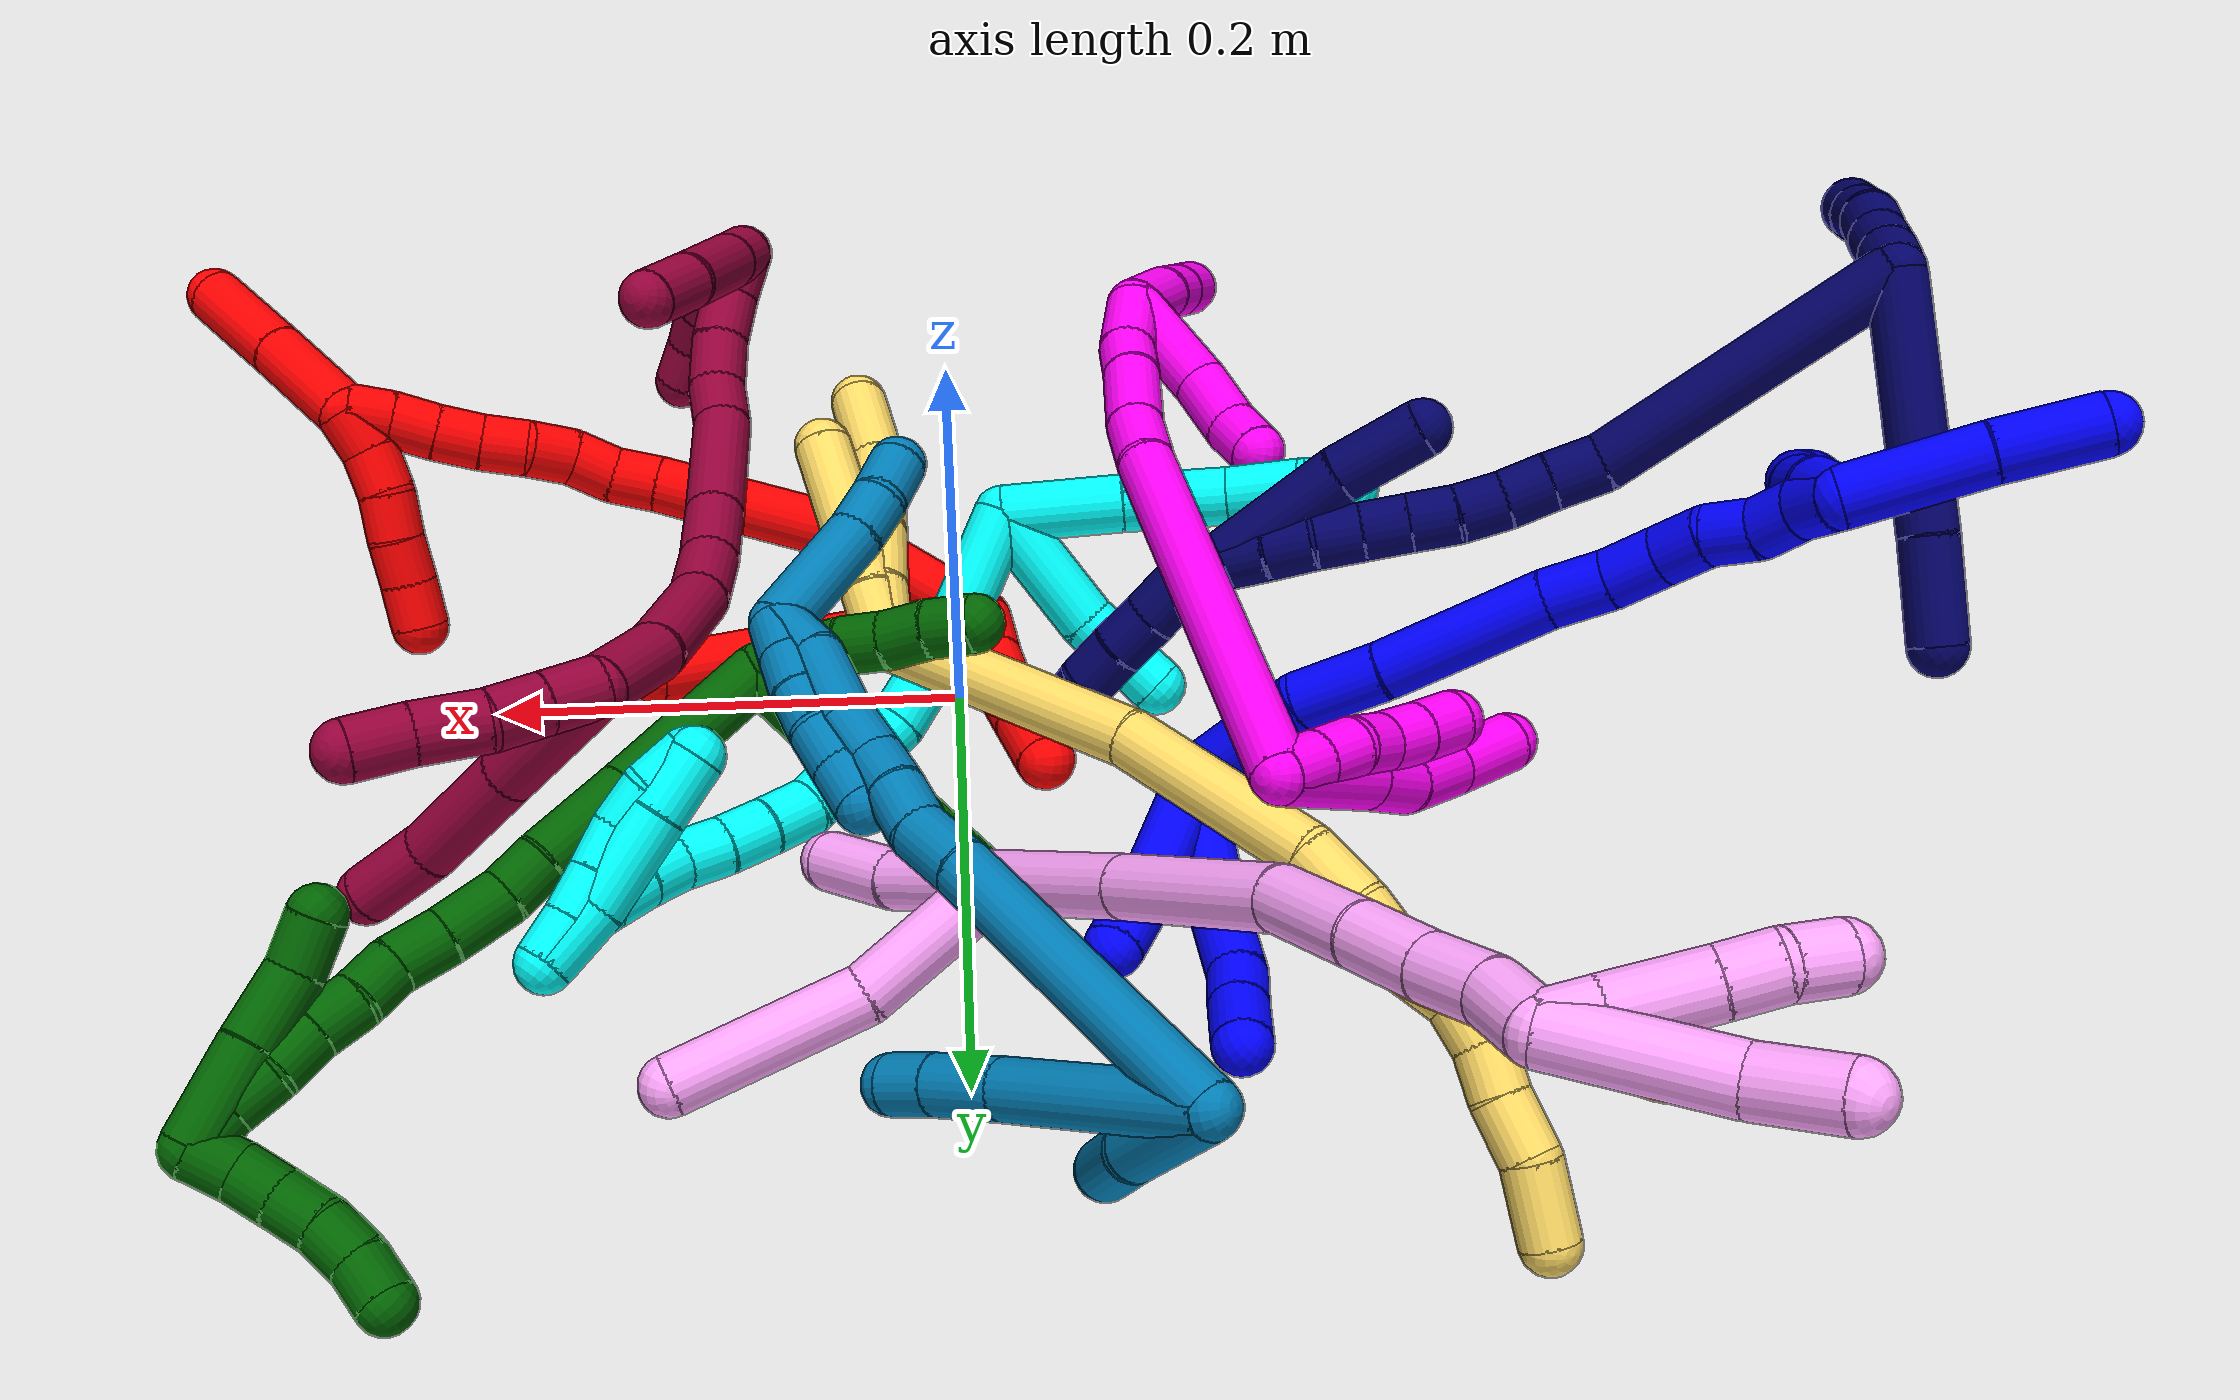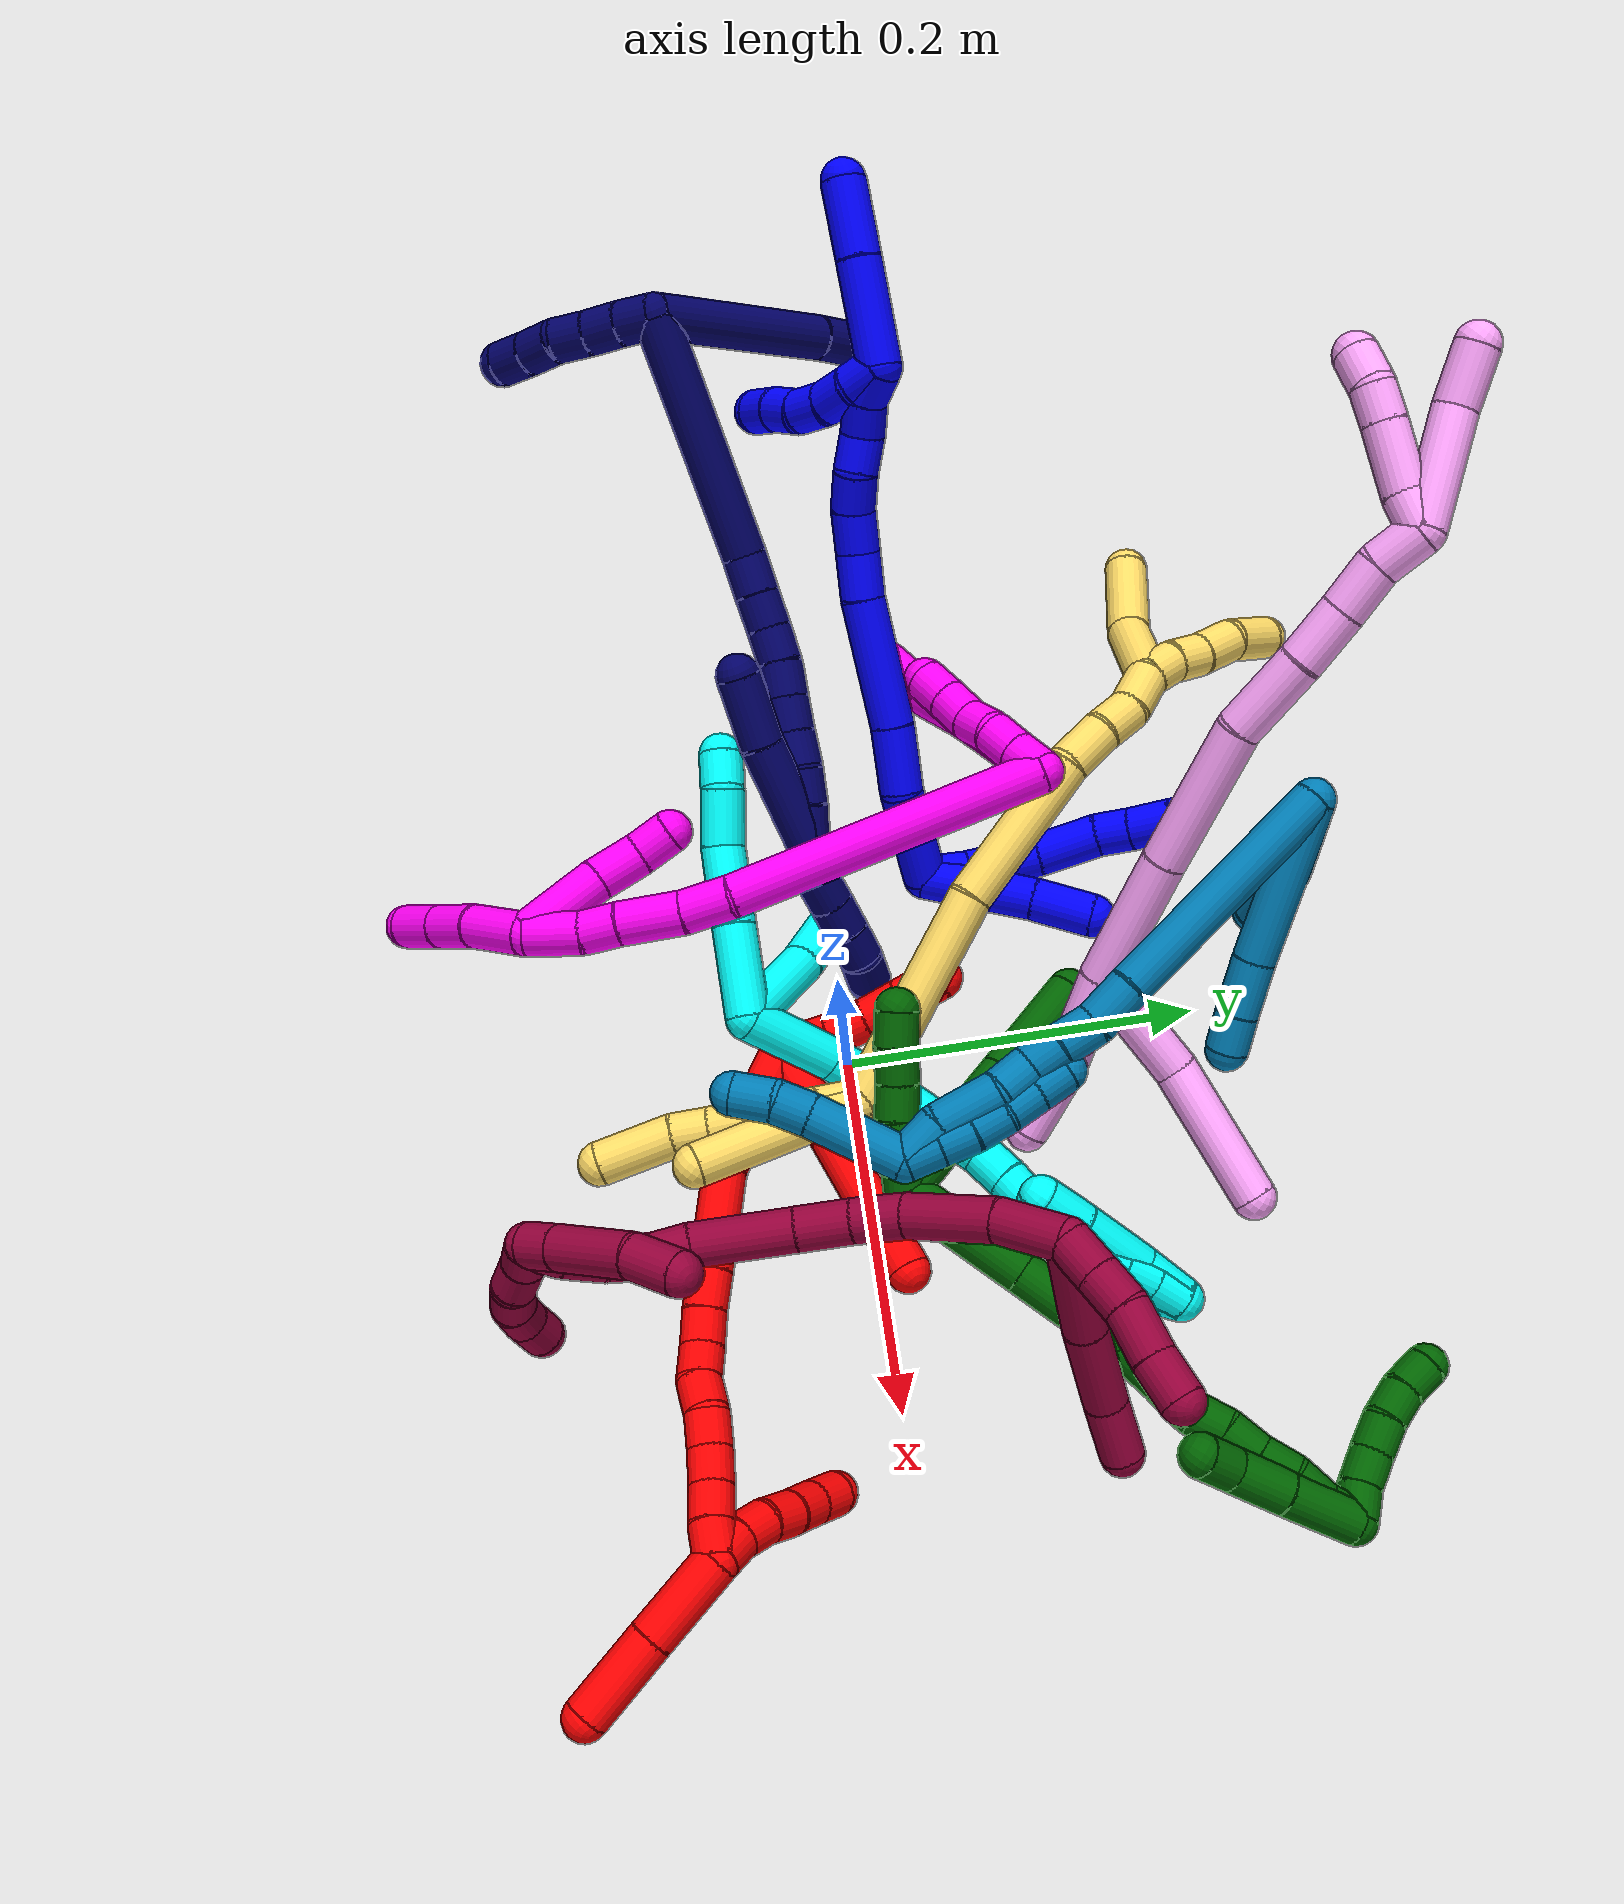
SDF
<sdf version="1.7">
 <world name="default">
  <plugin name="TubeGeneratorPlugin" filename="libtube_generator_plugin.so"/>
  <model name="photoneo_s_sensor">
   <static>1</static>
   <pose>0 0 2 1.57079 1.57079 3.14159</pose>
   <link name="link">
    <inertial><mass>0.1</mass></inertial>
    <sensor name="sensor" type="depth">
     <update_rate>30</update_rate>
     <camera>
      <horizontal_fov>1.22</horizontal_fov>
      <image><width>1920</width><height>1200</height><format>B8G8R8</format></image>
      <clip><near>0.1</near><far>4</far></clip>
      <depth_camera><output>points</output></depth_camera>
     </camera>
     <plugin name="camera_plugin" filename="libgazebo_ros_depth_camera.so">
      <baseline>0.2</baseline>
      <alwaysOn>1</alwaysOn>
      <updateRate>0.0</updateRate>
      <cameraName>camera_ir</cameraName>
      <imageTopicName>/camera/color/image_raw</imageTopicName>
      <cameraInfoTopicName>/camera/color/camera_info</cameraInfoTopicName>
      <depthImageTopicName>/camera/depth/image_raw</depthImageTopicName>
      <depthImageCameraInfoTopicName>/camera/depth/camera_info</depthImageCameraInfoTopicName>
      <pointCloudTopicName>/camera/depth/points</pointCloudTopicName>
      <frameName>fr_optical</frameName>
      <pointCloudCutoff>0.1</pointCloudCutoff>
      <pointCloudCutoffMax>2.0</pointCloudCutoffMax>
      <distortionK1>0</distortionK1>
      <distortionK2>0</distortionK2>
      <distortionK3>0</distortionK3>
      <distortionT1>0</distortionT1>
      <distortionT2>0</distortionT2>
      <CxPrime>0</CxPrime>
      <Cx>0</Cx>
      <Cy>0</Cy>
      <focalLength>0</focalLength>
      <hackBaseline>0</hackBaseline>
     </plugin>
    </sensor>
   </link>
  </model>
  <gravity>0 0 -9.8</gravity>
  <magnetic_field>6e-06 2.3e-05 -4.2e-05</magnetic_field>
  <atmosphere type="adiabatic"/>
  <physics name="default_physics" default="0" type="ode">
   <max_step_size>0.003</max_step_size>
   <real_time_factor>1</real_time_factor>
   <real_time_update_rate>1000</real_time_update_rate>
   <max_contacts>10000</max_contacts>
   <ode>
    <solver>
     <type>quick</type>
     <iters>100</iters>
     <sor>1.3</sor>
     <use_dynamic_moi_rescaling>0</use_dynamic_moi_rescaling>
    </solver>
    <constraints>
     <contact_max_correcting_vel>0</contact_max_correcting_vel>
     <contact_surface_layer>0.001</contact_surface_layer>
     <cfm>0</cfm>
     <erp>0.2</erp>
    </constraints>
   </ode>
  </physics>
  <scene><ambient>0.4 0.4 0.4 1</ambient><background>0.7 0.7 0.7 1</background><shadows>0</shadows></scene>
  <audio><device>default</device></audio>
  <spherical_coordinates>
   <surface_model>EARTH_WGS84</surface_model>
   <latitude_deg>0</latitude_deg>
   <longitude_deg>0</longitude_deg>
   <elevation>0</elevation>
   <heading_deg>0</heading_deg>
  </spherical_coordinates>
  <model name="bin">
   <static>1</static>
   <link name="bottom">
    <collision name="collision-bottom">
     <pose>0 0 -0.01 0 -0 0</pose>
     <geometry><box><size>0.8 0.6 0.02</size></box></geometry>
     <surface>
      <friction><ode><mu>100</mu><mu2>100</mu2></ode></friction>
      <contact><collide_bitmask>65535</collide_bitmask></contact>
     </surface>
    </collision>
   </link>
   <link name="west_wall">
    <collision name="collision-west_wall">
     <pose>-0.41 0 0.1 0 -0 0</pose>
     <geometry><box><size>0.02 0.6 0.2</size></box></geometry>
     <surface>
      <friction><ode><mu>100</mu><mu2>100</mu2></ode></friction>
      <contact><collide_bitmask>65535</collide_bitmask></contact>
     </surface>
    </collision>
   </link>
   <link name="east_wall">
    <collision name="collision-east_wall">
     <pose>0.41 0 0.1 0 -0 0</pose>
     <geometry><box><size>0.02 0.6 0.2</size></box></geometry>
     <surface>
      <friction><ode><mu>100</mu><mu2>100</mu2></ode></friction>
      <contact><collide_bitmask>65535</collide_bitmask></contact>
     </surface>
    </collision>
   </link>
   <link name="south_wall">
    <collision name="collision-south_wall">
     <pose>0 -0.31 0.1 0 -0 0</pose>
     <geometry><box><size>0.8 0.02 0.2</size></box></geometry>
     <surface>
      <friction><ode><mu>100</mu><mu2>100</mu2></ode></friction>
      <contact><collide_bitmask>65535</collide_bitmask></contact>
     </surface>
    </collision>
   </link>
   <link name="north_wall">
    <collision name="collision-north_wall">
     <pose>0 0.31 0.1 0 -0 0</pose>
     <geometry><box><size>0.8 0.02 0.2</size></box></geometry>
     <surface>
      <friction><ode><mu>100</mu><mu2>100</mu2></ode></friction>
      <contact><collide_bitmask>65535</collide_bitmask></contact>
     </surface>
    </collision>
   </link>
  </model>
  <model name="1">
   <static>0</static>
   <link name="1">
    <collision name="collision-cylinder-e_1_2_8">
     <pose>0.004239 0.011762 -0.002094 -1.74697 0.340959 -0.405361</pose>
     <geometry><cylinder><radius>0.0125</radius><length>0.025354</length></cylinder></geometry>
     <surface>
      <friction><ode><mu>1.16</mu><mu2>1.16</mu2><slip1>0</slip1><slip2>0</slip2></ode></friction>
      <contact><ode><kp>1e+06</kp><kd>1</kd><max_vel>0</max_vel><min_depth>0.001</min_depth></ode></contact>
     </surface>
    </collision>
    <visual name="visual-cylinder-e_1_2_8">
     <pose>0.004239 0.011762 -0.002094 -1.74697 0.340959 -0.405361</pose>
     <geometry><cylinder><radius>0.0125</radius><length>0.025354</length></cylinder></geometry>
     <material><ambient>0 0 1 1</ambient></material>
    </visual>
    <collision name="collision-cylinder-e_2_8_9">
     <pose>0.016435 0.043229 -0.004379 -1.58053 0.383754 -0.387415</pose>
     <geometry><cylinder><radius>0.0125</radius><length>0.042502</length></cylinder></geometry>
     <surface>
      <friction><ode><mu>1.16</mu><mu2>1.16</mu2><slip1>0</slip1><slip2>0</slip2></ode></friction>
      <contact><ode><kp>1e+06</kp><kd>1</kd><max_vel>0</max_vel><min_depth>0.001</min_depth></ode></contact>
     </surface>
    </collision>
    <visual name="visual-cylinder-e_2_8_9">
     <pose>0.016435 0.043229 -0.004379 -1.58053 0.383754 -0.387415</pose>
     <geometry><cylinder><radius>0.0125</radius><length>0.042502</length></cylinder></geometry>
     <material><ambient>0 0 1 1</ambient></material>
    </visual>
    <collision name="collision-cylinder-e_3_9_10">
     <pose>0.033536 0.078565 -0.001085 -1.35133 0.518812 -0.419175</pose>
     <geometry><cylinder><radius>0.0125</radius><length>0.036885</length></cylinder></geometry>
     <surface>
      <friction><ode><mu>1.16</mu><mu2>1.16</mu2><slip1>0</slip1><slip2>0</slip2></ode></friction>
      <contact><ode><kp>1e+06</kp><kd>1</kd><max_vel>0</max_vel><min_depth>0.001</min_depth></ode></contact>
     </surface>
    </collision>
    <visual name="visual-cylinder-e_3_9_10">
     <pose>0.033536 0.078565 -0.001085 -1.35133 0.518812 -0.419175</pose>
     <geometry><cylinder><radius>0.0125</radius><length>0.036885</length></cylinder></geometry>
     <material><ambient>0 0 1 1</ambient></material>
    </visual>
    <collision name="collision-cylinder-e_4_10_11">
     <pose>0.049275 0.101596 0.003753 -1.39026 0.719802 -0.608184</pose>
     <geometry><cylinder><radius>0.0125</radius><length>0.020007</length></cylinder></geometry>
     <surface>
      <friction><ode><mu>1.16</mu><mu2>1.16</mu2><slip1>0</slip1><slip2>0</slip2></ode></friction>
      <contact><ode><kp>1e+06</kp><kd>1</kd><max_vel>0</max_vel><min_depth>0.001</min_depth></ode></contact>
     </surface>
    </collision>
    <visual name="visual-cylinder-e_4_10_11">
     <pose>0.049275 0.101596 0.003753 -1.39026 0.719802 -0.608184</pose>
     <geometry><cylinder><radius>0.0125</radius><length>0.020007</length></cylinder></geometry>
     <material><ambient>0 0 1 1</ambient></material>
    </visual>
    <collision name="collision-cylinder-e_5_11_6">
     <pose>0.06421 0.118144 0.007584 -1.306 0.721584 -0.561968</pose>
     <geometry><cylinder><radius>0.0125</radius><length>0.025252</length></cylinder></geometry>
     <surface>
      <friction><ode><mu>1.16</mu><mu2>1.16</mu2><slip1>0</slip1><slip2>0</slip2></ode></friction>
      <contact><ode><kp>1e+06</kp><kd>1</kd><max_vel>0</max_vel><min_depth>0.001</min_depth></ode></contact>
     </surface>
    </collision>
    <visual name="visual-cylinder-e_5_11_6">
     <pose>0.06421 0.118144 0.007584 -1.306 0.721584 -0.561968</pose>
     <geometry><cylinder><radius>0.0125</radius><length>0.025252</length></cylinder></geometry>
     <material><ambient>0 0 1 1</ambient></material>
    </visual>
    <collision name="collision-cylinder-e_1_2_12">
     <pose>0.022543 0.021616 -0.007976 -1.92428 0.774484 -1.05893</pose>
     <geometry><cylinder><radius>0.0125</radius><length>0.06447</length></cylinder></geometry>
     <surface>
      <friction><ode><mu>1.16</mu><mu2>1.16</mu2><slip1>0</slip1><slip2>0</slip2></ode></friction>
      <contact><ode><kp>1e+06</kp><kd>1</kd><max_vel>0</max_vel><min_depth>0.001</min_depth></ode></contact>
     </surface>
    </collision>
    <visual name="visual-cylinder-e_1_2_12">
     <pose>0.022543 0.021616 -0.007976 -1.92428 0.774484 -1.05893</pose>
     <geometry><cylinder><radius>0.0125</radius><length>0.06447</length></cylinder></geometry>
     <material><ambient>0 0 1 1</ambient></material>
    </visual>
    <collision name="collision-cylinder-e_2_12_5">
     <pose>0.05853 0.053793 -0.020786 -2.00008 0.858298 -1.23842</pose>
     <geometry><cylinder><radius>0.0125</radius><length>0.03553</length></cylinder></geometry>
     <surface>
      <friction><ode><mu>1.16</mu><mu2>1.16</mu2><slip1>0</slip1><slip2>0</slip2></ode></friction>
      <contact><ode><kp>1e+06</kp><kd>1</kd><max_vel>0</max_vel><min_depth>0.001</min_depth></ode></contact>
     </surface>
    </collision>
    <visual name="visual-cylinder-e_2_12_5">
     <pose>0.05853 0.053793 -0.020786 -2.00008 0.858298 -1.23842</pose>
     <geometry><cylinder><radius>0.0125</radius><length>0.03553</length></cylinder></geometry>
     <material><ambient>0 0 1 1</ambient></material>
    </visual>
    <collision name="collision-cylinder-e_1_2_13">
     <pose>-0.003283 -0.000558 0.028062 0.019872 -0.116432 -0.001158</pose>
     <geometry><cylinder><radius>0.0125</radius><length>0.056517</length></cylinder></geometry>
     <surface>
      <friction><ode><mu>1.16</mu><mu2>1.16</mu2><slip1>0</slip1><slip2>0</slip2></ode></friction>
      <contact><ode><kp>1e+06</kp><kd>1</kd><max_vel>0</max_vel><min_depth>0.001</min_depth></ode></contact>
     </surface>
    </collision>
    <visual name="visual-cylinder-e_1_2_13">
     <pose>-0.003283 -0.000558 0.028062 0.019872 -0.116432 -0.001158</pose>
     <geometry><cylinder><radius>0.0125</radius><length>0.056517</length></cylinder></geometry>
     <material><ambient>0 0 1 1</ambient></material>
    </visual>
    <collision name="collision-cylinder-e_2_13_14">
     <pose>-0.011938 0.002782 0.074077 -0.213772 -0.284503 0.030731</pose>
     <geometry><cylinder><radius>0.0125</radius><length>0.038283</length></cylinder></geometry>
     <surface>
      <friction><ode><mu>1.16</mu><mu2>1.16</mu2><slip1>0</slip1><slip2>0</slip2></ode></friction>
      <contact><ode><kp>1e+06</kp><kd>1</kd><max_vel>0</max_vel><min_depth>0.001</min_depth></ode></contact>
     </surface>
    </collision>
    <visual name="visual-cylinder-e_2_13_14">
     <pose>-0.011938 0.002782 0.074077 -0.213772 -0.284503 0.030731</pose>
     <geometry><cylinder><radius>0.0125</radius><length>0.038283</length></cylinder></geometry>
     <material><ambient>0 0 1 1</ambient></material>
    </visual>
    <collision name="collision-cylinder-e_3_14_15">
     <pose>-0.029194 0.011231 0.126131 -0.13267 -0.332585 0.022299</pose>
     <geometry><cylinder><radius>0.0125</radius><length>0.072794</length></cylinder></geometry>
     <surface>
      <friction><ode><mu>1.16</mu><mu2>1.16</mu2><slip1>0</slip1><slip2>0</slip2></ode></friction>
      <contact><ode><kp>1e+06</kp><kd>1</kd><max_vel>0</max_vel><min_depth>0.001</min_depth></ode></contact>
     </surface>
    </collision>
    <visual name="visual-cylinder-e_3_14_15">
     <pose>-0.029194 0.011231 0.126131 -0.13267 -0.332585 0.022299</pose>
     <geometry><cylinder><radius>0.0125</radius><length>0.072794</length></cylinder></geometry>
     <material><ambient>0 0 1 1</ambient></material>
    </visual>
    <collision name="collision-cylinder-e_4_15_16">
     <pose>-0.044827 0.018952 0.172315 -0.256592 -0.291621 0.037885</pose>
     <geometry><cylinder><radius>0.0125</radius><length>0.026087</length></cylinder></geometry>
     <surface>
      <friction><ode><mu>1.16</mu><mu2>1.16</mu2><slip1>0</slip1><slip2>0</slip2></ode></friction>
      <contact><ode><kp>1e+06</kp><kd>1</kd><max_vel>0</max_vel><min_depth>0.001</min_depth></ode></contact>
     </surface>
    </collision>
    <visual name="visual-cylinder-e_4_15_16">
     <pose>-0.044827 0.018952 0.172315 -0.256592 -0.291621 0.037885</pose>
     <geometry><cylinder><radius>0.0125</radius><length>0.026087</length></cylinder></geometry>
     <material><ambient>0 0 1 1</ambient></material>
    </visual>
    <collision name="collision-cylinder-e_5_16_17">
     <pose>-0.050407 0.024088 0.195935 -0.168768 -0.155114 0.013146</pose>
     <geometry><cylinder><radius>0.0125</radius><length>0.023689</length></cylinder></geometry>
     <surface>
      <friction><ode><mu>1.16</mu><mu2>1.16</mu2><slip1>0</slip1><slip2>0</slip2></ode></friction>
      <contact><ode><kp>1e+06</kp><kd>1</kd><max_vel>0</max_vel><min_depth>0.001</min_depth></ode></contact>
     </surface>
    </collision>
    <visual name="visual-cylinder-e_5_16_17">
     <pose>-0.050407 0.024088 0.195935 -0.168768 -0.155114 0.013146</pose>
     <geometry><cylinder><radius>0.0125</radius><length>0.023689</length></cylinder></geometry>
     <material><ambient>0 0 1 1</ambient></material>
    </visual>
    <collision name="collision-cylinder-e_6_17_18">
     <pose>-0.05132 0.028536 0.218058 -0.230262 0.08415 -0.009737</pose>
     <geometry><cylinder><radius>0.0125</radius><length>0.021826</length></cylinder></geometry>
     <surface>
      <friction><ode><mu>1.16</mu><mu2>1.16</mu2><slip1>0</slip1><slip2>0</slip2></ode></friction>
      <contact><ode><kp>1e+06</kp><kd>1</kd><max_vel>0</max_vel><min_depth>0.001</min_depth></ode></contact>
     </surface>
    </collision>
    <visual name="visual-cylinder-e_6_17_18">
     <pose>-0.05132 0.028536 0.218058 -0.230262 0.08415 -0.009737</pose>
     <geometry><cylinder><radius>0.0125</radius><length>0.021826</length></cylinder></geometry>
     <material><ambient>0 0 1 1</ambient></material>
    </visual>
    <collision name="collision-cylinder-e_7_18_19">
     <pose>-0.051288 0.035727 0.2378 -0.475183 -0.085799 0.02079</pose>
     <geometry><cylinder><radius>0.0125</radius><length>0.020665</length></cylinder></geometry>
     <surface>
      <friction><ode><mu>1.16</mu><mu2>1.16</mu2><slip1>0</slip1><slip2>0</slip2></ode></friction>
      <contact><ode><kp>1e+06</kp><kd>1</kd><max_vel>0</max_vel><min_depth>0.001</min_depth></ode></contact>
     </surface>
    </collision>
    <visual name="visual-cylinder-e_7_18_19">
     <pose>-0.051288 0.035727 0.2378 -0.475183 -0.085799 0.02079</pose>
     <geometry><cylinder><radius>0.0125</radius><length>0.020665</length></cylinder></geometry>
     <material><ambient>0 0 1 1</ambient></material>
    </visual>
    <collision name="collision-cylinder-e_8_19_20">
     <pose>-0.051 0.042459 0.256703 -0.204518 0.117341 -0.012055</pose>
     <geometry><cylinder><radius>0.0125</radius><length>0.020052</length></cylinder></geometry>
     <surface>
      <friction><ode><mu>1.16</mu><mu2>1.16</mu2><slip1>0</slip1><slip2>0</slip2></ode></friction>
      <contact><ode><kp>1e+06</kp><kd>1</kd><max_vel>0</max_vel><min_depth>0.001</min_depth></ode></contact>
     </surface>
    </collision>
    <visual name="visual-cylinder-e_8_19_20">
     <pose>-0.051 0.042459 0.256703 -0.204518 0.117341 -0.012055</pose>
     <geometry><cylinder><radius>0.0125</radius><length>0.020052</length></cylinder></geometry>
     <material><ambient>0 0 1 1</ambient></material>
    </visual>
    <collision name="collision-cylinder-e_9_20_1">
     <pose>-0.046013 0.048342 0.274904 -0.428438 0.38938 -0.085747</pose>
     <geometry><cylinder><radius>0.0125</radius><length>0.020087</length></cylinder></geometry>
     <surface>
      <friction><ode><mu>1.16</mu><mu2>1.16</mu2><slip1>0</slip1><slip2>0</slip2></ode></friction>
      <contact><ode><kp>1e+06</kp><kd>1</kd><max_vel>0</max_vel><min_depth>0.001</min_depth></ode></contact>
     </surface>
    </collision>
    <visual name="visual-cylinder-e_9_20_1">
     <pose>-0.046013 0.048342 0.274904 -0.428438 0.38938 -0.085747</pose>
     <geometry><cylinder><radius>0.0125</radius><length>0.020087</length></cylinder></geometry>
     <material><ambient>0 0 1 1</ambient></material>
    </visual>
    <collision name="collision-cylinder-e_1_1_21">
     <pose>-0.048289 0.045934 0.278494 2.23058 -0.654623 -1.21216</pose>
     <geometry><cylinder><radius>0.0125</radius><length>0.02</length></cylinder></geometry>
     <surface>
      <friction><ode><mu>1.16</mu><mu2>1.16</mu2><slip1>0</slip1><slip2>0</slip2></ode></friction>
      <contact><ode><kp>1e+06</kp><kd>1</kd><max_vel>0</max_vel><min_depth>0.001</min_depth></ode></contact>
     </surface>
    </collision>
    <visual name="visual-cylinder-e_1_1_21">
     <pose>-0.048289 0.045934 0.278494 2.23058 -0.654623 -1.21216</pose>
     <geometry><cylinder><radius>0.0125</radius><length>0.02</length></cylinder></geometry>
     <material><ambient>0 0 1 1</ambient></material>
    </visual>
    <collision name="collision-cylinder-e_2_21_22">
     <pose>-0.061787 0.035141 0.268669 2.40224 -0.834455 -1.70484</pose>
     <geometry><cylinder><radius>0.0125</radius><length>0.02</length></cylinder></geometry>
     <surface>
      <friction><ode><mu>1.16</mu><mu2>1.16</mu2><slip1>0</slip1><slip2>0</slip2></ode></friction>
      <contact><ode><kp>1e+06</kp><kd>1</kd><max_vel>0</max_vel><min_depth>0.001</min_depth></ode></contact>
     </surface>
    </collision>
    <visual name="visual-cylinder-e_2_21_22">
     <pose>-0.061787 0.035141 0.268669 2.40224 -0.834455 -1.70484</pose>
     <geometry><cylinder><radius>0.0125</radius><length>0.02</length></cylinder></geometry>
     <material><ambient>0 0 1 1</ambient></material>
    </visual>
    <collision name="collision-cylinder-e_3_22_23">
     <pose>-0.077812 0.026596 0.260607 2.2277 -1.03833 -1.72065</pose>
     <geometry><cylinder><radius>0.0125</radius><length>0.02</length></cylinder></geometry>
     <surface>
      <friction><ode><mu>1.16</mu><mu2>1.16</mu2><slip1>0</slip1><slip2>0</slip2></ode></friction>
      <contact><ode><kp>1e+06</kp><kd>1</kd><max_vel>0</max_vel><min_depth>0.001</min_depth></ode></contact>
     </surface>
    </collision>
    <visual name="visual-cylinder-e_3_22_23">
     <pose>-0.077812 0.026596 0.260607 2.2277 -1.03833 -1.72065</pose>
     <geometry><cylinder><radius>0.0125</radius><length>0.02</length></cylinder></geometry>
     <material><ambient>0 0 1 1</ambient></material>
    </visual>
    <collision name="collision-cylinder-e_4_23_24">
     <pose>-0.096212 0.020871 0.256346 2.16879 -1.36305 -1.98624</pose>
     <geometry><cylinder><radius>0.0125</radius><length>0.02</length></cylinder></geometry>
     <surface>
      <friction><ode><mu>1.16</mu><mu2>1.16</mu2><slip1>0</slip1><slip2>0</slip2></ode></friction>
      <contact><ode><kp>1e+06</kp><kd>1</kd><max_vel>0</max_vel><min_depth>0.001</min_depth></ode></contact>
     </surface>
    </collision>
    <visual name="visual-cylinder-e_4_23_24">
     <pose>-0.096212 0.020871 0.256346 2.16879 -1.36305 -1.98624</pose>
     <geometry><cylinder><radius>0.0125</radius><length>0.02</length></cylinder></geometry>
     <material><ambient>0 0 1 1</ambient></material>
    </visual>
    <collision name="collision-cylinder-e_5_24_4">
     <pose>-0.115532 0.017561 0.252631 2.5804 -1.26441 -2.3919</pose>
     <geometry><cylinder><radius>0.0125</radius><length>0.02</length></cylinder></geometry>
     <surface>
      <friction><ode><mu>1.16</mu><mu2>1.16</mu2><slip1>0</slip1><slip2>0</slip2></ode></friction>
      <contact><ode><kp>1e+06</kp><kd>1</kd><max_vel>0</max_vel><min_depth>0.001</min_depth></ode></contact>
     </surface>
    </collision>
    <visual name="visual-cylinder-e_5_24_4">
     <pose>-0.115532 0.017561 0.252631 2.5804 -1.26441 -2.3919</pose>
     <geometry><cylinder><radius>0.0125</radius><length>0.02</length></cylinder></geometry>
     <material><ambient>0 0 1 1</ambient></material>
    </visual>
    <collision name="collision-cylinder-e_1_1_25">
     <pose>-0.054392 0.05852 0.308636 -0.244922 -0.437624 0.054724</pose>
     <geometry><cylinder><radius>0.0125</radius><length>0.057538</length></cylinder></geometry>
     <surface>
      <friction><ode><mu>1.16</mu><mu2>1.16</mu2><slip1>0</slip1><slip2>0</slip2></ode></friction>
      <contact><ode><kp>1e+06</kp><kd>1</kd><max_vel>0</max_vel><min_depth>0.001</min_depth></ode></contact>
     </surface>
    </collision>
    <visual name="visual-cylinder-e_1_1_25">
     <pose>-0.054392 0.05852 0.308636 -0.244922 -0.437624 0.054724</pose>
     <geometry><cylinder><radius>0.0125</radius><length>0.057538</length></cylinder></geometry>
     <material><ambient>0 0 1 1</ambient></material>
    </visual>
    <collision name="collision-cylinder-e_2_25_3">
     <pose>-0.076765 0.07008 0.351795 -0.285177 -0.500086 0.073295</pose>
     <geometry><cylinder><radius>0.0125</radius><length>0.042462</length></cylinder></geometry>
     <surface>
      <friction><ode><mu>1.16</mu><mu2>1.16</mu2><slip1>0</slip1><slip2>0</slip2></ode></friction>
      <contact><ode><kp>1e+06</kp><kd>1</kd><max_vel>0</max_vel><min_depth>0.001</min_depth></ode></contact>
     </surface>
    </collision>
    <visual name="visual-cylinder-e_2_25_3">
     <pose>-0.076765 0.07008 0.351795 -0.285177 -0.500086 0.073295</pose>
     <geometry><cylinder><radius>0.0125</radius><length>0.042462</length></cylinder></geometry>
     <material><ambient>0 0 1 1</ambient></material>
    </visual>
    <collision name="collision-sphere-3">
     <pose>-0.086945 0.075322 0.369674 0 -0 0</pose>
     <geometry><sphere><radius>0.0125</radius></sphere></geometry>
     <surface>
      <friction><ode><mu>1.16</mu><mu2>1.16</mu2><slip1>0</slip1><slip2>0</slip2></ode></friction>
      <contact><ode><kp>1e+06</kp><kd>1</kd><max_vel>0</max_vel><min_depth>0.001</min_depth></ode></contact>
     </surface>
    </collision>
    <visual name="visual-sphere-3">
     <pose>-0.086945 0.075322 0.369674 0 -0 0</pose>
     <geometry><sphere><radius>0.0125</radius></sphere></geometry>
     <material><ambient>0 0 1 1</ambient></material>
    </visual>
    <collision name="collision-sphere-25">
     <pose>-0.066584 0.064839 0.333917 0 -0 0</pose>
     <geometry><sphere><radius>0.0125</radius></sphere></geometry>
     <surface>
      <friction><ode><mu>1.16</mu><mu2>1.16</mu2><slip1>0</slip1><slip2>0</slip2></ode></friction>
      <contact><ode><kp>1e+06</kp><kd>1</kd><max_vel>0</max_vel><min_depth>0.001</min_depth></ode></contact>
     </surface>
    </collision>
    <visual name="visual-sphere-25">
     <pose>-0.066584 0.064839 0.333917 0 -0 0</pose>
     <geometry><sphere><radius>0.0125</radius></sphere></geometry>
     <material><ambient>0 0 1 1</ambient></material>
    </visual>
    <collision name="collision-sphere-4">
     <pose>-0.125066 0.015956 0.250077 0 -0 0</pose>
     <geometry><sphere><radius>0.0125</radius></sphere></geometry>
     <surface>
      <friction><ode><mu>1.16</mu><mu2>1.16</mu2><slip1>0</slip1><slip2>0</slip2></ode></friction>
      <contact><ode><kp>1e+06</kp><kd>1</kd><max_vel>0</max_vel><min_depth>0.001</min_depth></ode></contact>
     </surface>
    </collision>
    <visual name="visual-sphere-4">
     <pose>-0.125066 0.015956 0.250077 0 -0 0</pose>
     <geometry><sphere><radius>0.0125</radius></sphere></geometry>
     <material><ambient>0 0 1 1</ambient></material>
    </visual>
    <collision name="collision-sphere-24">
     <pose>-0.105997 0.019166 0.255184 0 -0 0</pose>
     <geometry><sphere><radius>0.0125</radius></sphere></geometry>
     <surface>
      <friction><ode><mu>1.16</mu><mu2>1.16</mu2><slip1>0</slip1><slip2>0</slip2></ode></friction>
      <contact><ode><kp>1e+06</kp><kd>1</kd><max_vel>0</max_vel><min_depth>0.001</min_depth></ode></contact>
     </surface>
    </collision>
    <visual name="visual-sphere-24">
     <pose>-0.105997 0.019166 0.255184 0 -0 0</pose>
     <geometry><sphere><radius>0.0125</radius></sphere></geometry>
     <material><ambient>0 0 1 1</ambient></material>
    </visual>
    <collision name="collision-sphere-23">
     <pose>-0.086427 0.022576 0.257507 0 -0 0</pose>
     <geometry><sphere><radius>0.0125</radius></sphere></geometry>
     <surface>
      <friction><ode><mu>1.16</mu><mu2>1.16</mu2><slip1>0</slip1><slip2>0</slip2></ode></friction>
      <contact><ode><kp>1e+06</kp><kd>1</kd><max_vel>0</max_vel><min_depth>0.001</min_depth></ode></contact>
     </surface>
    </collision>
    <visual name="visual-sphere-23">
     <pose>-0.086427 0.022576 0.257507 0 -0 0</pose>
     <geometry><sphere><radius>0.0125</radius></sphere></geometry>
     <material><ambient>0 0 1 1</ambient></material>
    </visual>
    <collision name="collision-sphere-22">
     <pose>-0.069196 0.030616 0.263707 0 -0 0</pose>
     <geometry><sphere><radius>0.0125</radius></sphere></geometry>
     <surface>
      <friction><ode><mu>1.16</mu><mu2>1.16</mu2><slip1>0</slip1><slip2>0</slip2></ode></friction>
      <contact><ode><kp>1e+06</kp><kd>1</kd><max_vel>0</max_vel><min_depth>0.001</min_depth></ode></contact>
     </surface>
    </collision>
    <visual name="visual-sphere-22">
     <pose>-0.069196 0.030616 0.263707 0 -0 0</pose>
     <geometry><sphere><radius>0.0125</radius></sphere></geometry>
     <material><ambient>0 0 1 1</ambient></material>
    </visual>
    <collision name="collision-sphere-21">
     <pose>-0.054378 0.039666 0.273632 0 -0 0</pose>
     <geometry><sphere><radius>0.0125</radius></sphere></geometry>
     <surface>
      <friction><ode><mu>1.16</mu><mu2>1.16</mu2><slip1>0</slip1><slip2>0</slip2></ode></friction>
      <contact><ode><kp>1e+06</kp><kd>1</kd><max_vel>0</max_vel><min_depth>0.001</min_depth></ode></contact>
     </surface>
    </collision>
    <visual name="visual-sphere-21">
     <pose>-0.054378 0.039666 0.273632 0 -0 0</pose>
     <geometry><sphere><radius>0.0125</radius></sphere></geometry>
     <material><ambient>0 0 1 1</ambient></material>
    </visual>
    <collision name="collision-sphere-1">
     <pose>-0.0422 0.052202 0.283356 0 -0 0</pose>
     <geometry><sphere><radius>0.0125</radius></sphere></geometry>
     <surface>
      <friction><ode><mu>1.16</mu><mu2>1.16</mu2><slip1>0</slip1><slip2>0</slip2></ode></friction>
      <contact><ode><kp>1e+06</kp><kd>1</kd><max_vel>0</max_vel><min_depth>0.001</min_depth></ode></contact>
     </surface>
    </collision>
    <visual name="visual-sphere-1">
     <pose>-0.0422 0.052202 0.283356 0 -0 0</pose>
     <geometry><sphere><radius>0.0125</radius></sphere></geometry>
     <material><ambient>0 0 1 1</ambient></material>
    </visual>
    <collision name="collision-sphere-6">
     <pose>0.072551 0.127293 0.010065 0 -0 0</pose>
     <geometry><sphere><radius>0.0125</radius></sphere></geometry>
     <surface>
      <friction><ode><mu>1.16</mu><mu2>1.16</mu2><slip1>0</slip1><slip2>0</slip2></ode></friction>
      <contact><ode><kp>1e+06</kp><kd>1</kd><max_vel>0</max_vel><min_depth>0.001</min_depth></ode></contact>
     </surface>
    </collision>
    <visual name="visual-sphere-6">
     <pose>0.072551 0.127293 0.010065 0 -0 0</pose>
     <geometry><sphere><radius>0.0125</radius></sphere></geometry>
     <material><ambient>0 0 1 1</ambient></material>
    </visual>
    <collision name="collision-sphere-11">
     <pose>0.05587 0.108996 0.005103 0 -0 0</pose>
     <geometry><sphere><radius>0.0125</radius></sphere></geometry>
     <surface>
      <friction><ode><mu>1.16</mu><mu2>1.16</mu2><slip1>0</slip1><slip2>0</slip2></ode></friction>
      <contact><ode><kp>1e+06</kp><kd>1</kd><max_vel>0</max_vel><min_depth>0.001</min_depth></ode></contact>
     </surface>
    </collision>
    <visual name="visual-sphere-11">
     <pose>0.05587 0.108996 0.005103 0 -0 0</pose>
     <geometry><sphere><radius>0.0125</radius></sphere></geometry>
     <material><ambient>0 0 1 1</ambient></material>
    </visual>
    <collision name="collision-sphere-10">
     <pose>0.04268 0.094196 0.002402 0 -0 0</pose>
     <geometry><sphere><radius>0.0125</radius></sphere></geometry>
     <surface>
      <friction><ode><mu>1.16</mu><mu2>1.16</mu2><slip1>0</slip1><slip2>0</slip2></ode></friction>
      <contact><ode><kp>1e+06</kp><kd>1</kd><max_vel>0</max_vel><min_depth>0.001</min_depth></ode></contact>
     </surface>
    </collision>
    <visual name="visual-sphere-10">
     <pose>0.04268 0.094196 0.002402 0 -0 0</pose>
     <geometry><sphere><radius>0.0125</radius></sphere></geometry>
     <material><ambient>0 0 1 1</ambient></material>
    </visual>
    <collision name="collision-sphere-9">
     <pose>0.024391 0.062933 -0.004571 0 -0 0</pose>
     <geometry><sphere><radius>0.0125</radius></sphere></geometry>
     <surface>
      <friction><ode><mu>1.16</mu><mu2>1.16</mu2><slip1>0</slip1><slip2>0</slip2></ode></friction>
      <contact><ode><kp>1e+06</kp><kd>1</kd><max_vel>0</max_vel><min_depth>0.001</min_depth></ode></contact>
     </surface>
    </collision>
    <visual name="visual-sphere-9">
     <pose>0.024391 0.062933 -0.004571 0 -0 0</pose>
     <geometry><sphere><radius>0.0125</radius></sphere></geometry>
     <material><ambient>0 0 1 1</ambient></material>
    </visual>
    <collision name="collision-sphere-2">
     <geometry><sphere><radius>0.0125</radius></sphere></geometry>
     <surface>
      <friction><ode><mu>1.16</mu><mu2>1.16</mu2><slip1>0</slip1><slip2>0</slip2></ode></friction>
      <contact><ode><kp>1e+06</kp><kd>1</kd><max_vel>0</max_vel><min_depth>0.001</min_depth></ode></contact>
     </surface>
    </collision>
    <visual name="visual-sphere-2">
     <geometry><sphere><radius>0.0125</radius></sphere></geometry>
     <material><ambient>0 0 1 1</ambient></material>
    </visual>
    <collision name="collision-sphere-19">
     <pose>-0.052173 0.040437 0.246954 0 -0 0</pose>
     <geometry><sphere><radius>0.0125</radius></sphere></geometry>
     <surface>
      <friction><ode><mu>1.16</mu><mu2>1.16</mu2><slip1>0</slip1><slip2>0</slip2></ode></friction>
      <contact><ode><kp>1e+06</kp><kd>1</kd><max_vel>0</max_vel><min_depth>0.001</min_depth></ode></contact>
     </surface>
    </collision>
    <visual name="visual-sphere-19">
     <pose>-0.052173 0.040437 0.246954 0 -0 0</pose>
     <geometry><sphere><radius>0.0125</radius></sphere></geometry>
     <material><ambient>0 0 1 1</ambient></material>
    </visual>
    <collision name="collision-sphere-8">
     <pose>0.008478 0.023524 -0.004188 0 -0 0</pose>
     <geometry><sphere><radius>0.0125</radius></sphere></geometry>
     <surface>
      <friction><ode><mu>1.16</mu><mu2>1.16</mu2><slip1>0</slip1><slip2>0</slip2></ode></friction>
      <contact><ode><kp>1e+06</kp><kd>1</kd><max_vel>0</max_vel><min_depth>0.001</min_depth></ode></contact>
     </surface>
    </collision>
    <visual name="visual-sphere-8">
     <pose>0.008478 0.023524 -0.004188 0 -0 0</pose>
     <geometry><sphere><radius>0.0125</radius></sphere></geometry>
     <material><ambient>0 0 1 1</ambient></material>
    </visual>
    <collision name="collision-sphere-12">
     <pose>0.045087 0.043233 -0.015952 0 -0 0</pose>
     <geometry><sphere><radius>0.0125</radius></sphere></geometry>
     <surface>
      <friction><ode><mu>1.16</mu><mu2>1.16</mu2><slip1>0</slip1><slip2>0</slip2></ode></friction>
      <contact><ode><kp>1e+06</kp><kd>1</kd><max_vel>0</max_vel><min_depth>0.001</min_depth></ode></contact>
     </surface>
    </collision>
    <visual name="visual-sphere-12">
     <pose>0.045087 0.043233 -0.015952 0 -0 0</pose>
     <geometry><sphere><radius>0.0125</radius></sphere></geometry>
     <material><ambient>0 0 1 1</ambient></material>
    </visual>
    <collision name="collision-sphere-5">
     <pose>0.071974 0.064352 -0.02562 0 -0 0</pose>
     <geometry><sphere><radius>0.0125</radius></sphere></geometry>
     <surface>
      <friction><ode><mu>1.16</mu><mu2>1.16</mu2><slip1>0</slip1><slip2>0</slip2></ode></friction>
      <contact><ode><kp>1e+06</kp><kd>1</kd><max_vel>0</max_vel><min_depth>0.001</min_depth></ode></contact>
     </surface>
    </collision>
    <visual name="visual-sphere-5">
     <pose>0.071974 0.064352 -0.02562 0 -0 0</pose>
     <geometry><sphere><radius>0.0125</radius></sphere></geometry>
     <material><ambient>0 0 1 1</ambient></material>
    </visual>
    <collision name="collision-sphere-13">
     <pose>-0.006566 -0.001115 0.056123 0 -0 0</pose>
     <geometry><sphere><radius>0.0125</radius></sphere></geometry>
     <surface>
      <friction><ode><mu>1.16</mu><mu2>1.16</mu2><slip1>0</slip1><slip2>0</slip2></ode></friction>
      <contact><ode><kp>1e+06</kp><kd>1</kd><max_vel>0</max_vel><min_depth>0.001</min_depth></ode></contact>
     </surface>
    </collision>
    <visual name="visual-sphere-13">
     <pose>-0.006566 -0.001115 0.056123 0 -0 0</pose>
     <geometry><sphere><radius>0.0125</radius></sphere></geometry>
     <material><ambient>0 0 1 1</ambient></material>
    </visual>
    <collision name="collision-sphere-14">
     <pose>-0.017311 0.00668 0.092031 0 -0 0</pose>
     <geometry><sphere><radius>0.0125</radius></sphere></geometry>
     <surface>
      <friction><ode><mu>1.16</mu><mu2>1.16</mu2><slip1>0</slip1><slip2>0</slip2></ode></friction>
      <contact><ode><kp>1e+06</kp><kd>1</kd><max_vel>0</max_vel><min_depth>0.001</min_depth></ode></contact>
     </surface>
    </collision>
    <visual name="visual-sphere-14">
     <pose>-0.017311 0.00668 0.092031 0 -0 0</pose>
     <geometry><sphere><radius>0.0125</radius></sphere></geometry>
     <material><ambient>0 0 1 1</ambient></material>
    </visual>
    <collision name="collision-sphere-15">
     <pose>-0.041077 0.015781 0.160231 0 -0 0</pose>
     <geometry><sphere><radius>0.0125</radius></sphere></geometry>
     <surface>
      <friction><ode><mu>1.16</mu><mu2>1.16</mu2><slip1>0</slip1><slip2>0</slip2></ode></friction>
      <contact><ode><kp>1e+06</kp><kd>1</kd><max_vel>0</max_vel><min_depth>0.001</min_depth></ode></contact>
     </surface>
    </collision>
    <visual name="visual-sphere-15">
     <pose>-0.041077 0.015781 0.160231 0 -0 0</pose>
     <geometry><sphere><radius>0.0125</radius></sphere></geometry>
     <material><ambient>0 0 1 1</ambient></material>
    </visual>
    <collision name="collision-sphere-16">
     <pose>-0.048577 0.022122 0.184399 0 -0 0</pose>
     <geometry><sphere><radius>0.0125</radius></sphere></geometry>
     <surface>
      <friction><ode><mu>1.16</mu><mu2>1.16</mu2><slip1>0</slip1><slip2>0</slip2></ode></friction>
      <contact><ode><kp>1e+06</kp><kd>1</kd><max_vel>0</max_vel><min_depth>0.001</min_depth></ode></contact>
     </surface>
    </collision>
    <visual name="visual-sphere-16">
     <pose>-0.048577 0.022122 0.184399 0 -0 0</pose>
     <geometry><sphere><radius>0.0125</radius></sphere></geometry>
     <material><ambient>0 0 1 1</ambient></material>
    </visual>
    <collision name="collision-sphere-17">
     <pose>-0.052237 0.026054 0.207471 0 -0 0</pose>
     <geometry><sphere><radius>0.0125</radius></sphere></geometry>
     <surface>
      <friction><ode><mu>1.16</mu><mu2>1.16</mu2><slip1>0</slip1><slip2>0</slip2></ode></friction>
      <contact><ode><kp>1e+06</kp><kd>1</kd><max_vel>0</max_vel><min_depth>0.001</min_depth></ode></contact>
     </surface>
    </collision>
    <visual name="visual-sphere-17">
     <pose>-0.052237 0.026054 0.207471 0 -0 0</pose>
     <geometry><sphere><radius>0.0125</radius></sphere></geometry>
     <material><ambient>0 0 1 1</ambient></material>
    </visual>
    <collision name="collision-sphere-18">
     <pose>-0.050403 0.031017 0.228646 0 -0 0</pose>
     <geometry><sphere><radius>0.0125</radius></sphere></geometry>
     <surface>
      <friction><ode><mu>1.16</mu><mu2>1.16</mu2><slip1>0</slip1><slip2>0</slip2></ode></friction>
      <contact><ode><kp>1e+06</kp><kd>1</kd><max_vel>0</max_vel><min_depth>0.001</min_depth></ode></contact>
     </surface>
    </collision>
    <visual name="visual-sphere-18">
     <pose>-0.050403 0.031017 0.228646 0 -0 0</pose>
     <geometry><sphere><radius>0.0125</radius></sphere></geometry>
     <material><ambient>0 0 1 1</ambient></material>
    </visual>
    <collision name="collision-sphere-20">
     <pose>-0.049826 0.044481 0.266453 0 -0 0</pose>
     <geometry><sphere><radius>0.0125</radius></sphere></geometry>
     <surface>
      <friction><ode><mu>1.16</mu><mu2>1.16</mu2><slip1>0</slip1><slip2>0</slip2></ode></friction>
      <contact><ode><kp>1e+06</kp><kd>1</kd><max_vel>0</max_vel><min_depth>0.001</min_depth></ode></contact>
     </surface>
    </collision>
    <visual name="visual-sphere-20">
     <pose>-0.049826 0.044481 0.266453 0 -0 0</pose>
     <geometry><sphere><radius>0.0125</radius></sphere></geometry>
     <material><ambient>0 0 1 1</ambient></material>
    </visual>
    <inertial>
     <pose>-0.020609 0.037014 0.134465 0 -0 0</pose>
     <mass>0.75</mass>
     <inertia>
      <ixx>8.6e-05</ixx>
      <ixy>0</ixy>
      <ixz>0</ixz>
      <iyy>0.000108</iyy>
      <iyz>0</iyz>
      <izz>-2.1e-05</izz>
     </inertia>
    </inertial>
   </link>
   <pose>-0.098556 0.060342 0.017502 -0.339061 -0.657101 0.604953</pose>
  </model>
  <model name="2">
   <static>0</static>
   <link name="2">
    <collision name="collision-cylinder-e_1_2_8">
     <pose>0.006293 0.001912 0.029765 -0.064143 0.207925 -0.006695</pose>
     <geometry><cylinder><radius>0.0125</radius><length>0.060966</length></cylinder></geometry>
     <surface>
      <friction><ode><mu>1.16</mu><mu2>1.16</mu2><slip1>0</slip1><slip2>0</slip2></ode></friction>
      <contact><ode><kp>1e+06</kp><kd>1</kd><max_vel>0</max_vel><min_depth>0.001</min_depth></ode></contact>
     </surface>
    </collision>
    <visual name="visual-cylinder-e_1_2_8">
     <pose>0.006293 0.001912 0.029765 -0.064143 0.207925 -0.006695</pose>
     <geometry><cylinder><radius>0.0125</radius><length>0.060966</length></cylinder></geometry>
     <material><ambient>1 0 0 1</ambient></material>
    </visual>
    <collision name="collision-cylinder-e_2_8_6">
     <pose>0.022599 0.007557 0.102745 -0.086172 0.226875 -0.009823</pose>
     <geometry><cylinder><radius>0.0125</radius><length>0.089034</length></cylinder></geometry>
     <surface>
      <friction><ode><mu>1.16</mu><mu2>1.16</mu2><slip1>0</slip1><slip2>0</slip2></ode></friction>
      <contact><ode><kp>1e+06</kp><kd>1</kd><max_vel>0</max_vel><min_depth>0.001</min_depth></ode></contact>
     </surface>
    </collision>
    <visual name="visual-cylinder-e_2_8_6">
     <pose>0.022599 0.007557 0.102745 -0.086172 0.226875 -0.009823</pose>
     <geometry><cylinder><radius>0.0125</radius><length>0.089034</length></cylinder></geometry>
     <material><ambient>1 0 0 1</ambient></material>
    </visual>
    <collision name="collision-cylinder-e_1_2_9">
     <pose>-0.009029 0.00991 0.004728 -1.12565 -0.68822 0.444705</pose>
     <geometry><cylinder><radius>0.0125</radius><length>0.028431</length></cylinder></geometry>
     <surface>
      <friction><ode><mu>1.16</mu><mu2>1.16</mu2><slip1>0</slip1><slip2>0</slip2></ode></friction>
      <contact><ode><kp>1e+06</kp><kd>1</kd><max_vel>0</max_vel><min_depth>0.001</min_depth></ode></contact>
     </surface>
    </collision>
    <visual name="visual-cylinder-e_1_2_9">
     <pose>-0.009029 0.00991 0.004728 -1.12565 -0.68822 0.444705</pose>
     <geometry><cylinder><radius>0.0125</radius><length>0.028431</length></cylinder></geometry>
     <material><ambient>1 0 0 1</ambient></material>
    </visual>
    <collision name="collision-cylinder-e_2_9_10">
     <pose>-0.025417 0.028088 0.012349 -1.23416 -0.698643 0.505825</pose>
     <geometry><cylinder><radius>0.0125</radius><length>0.022881</length></cylinder></geometry>
     <surface>
      <friction><ode><mu>1.16</mu><mu2>1.16</mu2><slip1>0</slip1><slip2>0</slip2></ode></friction>
      <contact><ode><kp>1e+06</kp><kd>1</kd><max_vel>0</max_vel><min_depth>0.001</min_depth></ode></contact>
     </surface>
    </collision>
    <visual name="visual-cylinder-e_2_9_10">
     <pose>-0.025417 0.028088 0.012349 -1.23416 -0.698643 0.505825</pose>
     <geometry><cylinder><radius>0.0125</radius><length>0.022881</length></cylinder></geometry>
     <material><ambient>1 0 0 1</ambient></material>
    </visual>
    <collision name="collision-cylinder-e_3_10_11">
     <pose>-0.040969 0.043817 0.017432 -1.28531 -0.811638 0.62246</pose>
     <geometry><cylinder><radius>0.0125</radius><length>0.022592</length></cylinder></geometry>
     <surface>
      <friction><ode><mu>1.16</mu><mu2>1.16</mu2><slip1>0</slip1><slip2>0</slip2></ode></friction>
      <contact><ode><kp>1e+06</kp><kd>1</kd><max_vel>0</max_vel><min_depth>0.001</min_depth></ode></contact>
     </surface>
    </collision>
    <visual name="visual-cylinder-e_3_10_11">
     <pose>-0.040969 0.043817 0.017432 -1.28531 -0.811638 0.62246</pose>
     <geometry><cylinder><radius>0.0125</radius><length>0.022592</length></cylinder></geometry>
     <material><ambient>1 0 0 1</ambient></material>
    </visual>
    <collision name="collision-cylinder-e_4_11_5">
     <pose>-0.058395 0.060238 0.021799 -1.33248 -0.785967 0.630085</pose>
     <geometry><cylinder><radius>0.0125</radius><length>0.026096</length></cylinder></geometry>
     <surface>
      <friction><ode><mu>1.16</mu><mu2>1.16</mu2><slip1>0</slip1><slip2>0</slip2></ode></friction>
      <contact><ode><kp>1e+06</kp><kd>1</kd><max_vel>0</max_vel><min_depth>0.001</min_depth></ode></contact>
     </surface>
    </collision>
    <visual name="visual-cylinder-e_4_11_5">
     <pose>-0.058395 0.060238 0.021799 -1.33248 -0.785967 0.630085</pose>
     <geometry><cylinder><radius>0.0125</radius><length>0.026096</length></cylinder></geometry>
     <material><ambient>1 0 0 1</ambient></material>
    </visual>
    <collision name="collision-cylinder-e_1_2_12">
     <pose>0.021186 -0.024422 0.022539 0.825469 0.567544 0.254038</pose>
     <geometry><cylinder><radius>0.0125</radius><length>0.078824</length></cylinder></geometry>
     <surface>
      <friction><ode><mu>1.16</mu><mu2>1.16</mu2><slip1>0</slip1><slip2>0</slip2></ode></friction>
      <contact><ode><kp>1e+06</kp><kd>1</kd><max_vel>0</max_vel><min_depth>0.001</min_depth></ode></contact>
     </surface>
    </collision>
    <visual name="visual-cylinder-e_1_2_12">
     <pose>0.021186 -0.024422 0.022539 0.825469 0.567544 0.254038</pose>
     <geometry><cylinder><radius>0.0125</radius><length>0.078824</length></cylinder></geometry>
     <material><ambient>1 0 0 1</ambient></material>
    </visual>
    <collision name="collision-cylinder-e_2_12_13">
     <pose>0.05793 -0.059929 0.066997 0.468223 0.564607 0.138125</pose>
     <geometry><cylinder><radius>0.0125</radius><length>0.05815</length></cylinder></geometry>
     <surface>
      <friction><ode><mu>1.16</mu><mu2>1.16</mu2><slip1>0</slip1><slip2>0</slip2></ode></friction>
      <contact><ode><kp>1e+06</kp><kd>1</kd><max_vel>0</max_vel><min_depth>0.001</min_depth></ode></contact>
     </surface>
    </collision>
    <visual name="visual-cylinder-e_2_12_13">
     <pose>0.05793 -0.059929 0.066997 0.468223 0.564607 0.138125</pose>
     <geometry><cylinder><radius>0.0125</radius><length>0.05815</length></cylinder></geometry>
     <material><ambient>1 0 0 1</ambient></material>
    </visual>
    <collision name="collision-cylinder-e_3_13_14">
     <pose>0.079386 -0.07528 0.09707 0.481995 0.56996 0.143753</pose>
     <geometry><cylinder><radius>0.0125</radius><length>0.021861</length></cylinder></geometry>
     <surface>
      <friction><ode><mu>1.16</mu><mu2>1.16</mu2><slip1>0</slip1><slip2>0</slip2></ode></friction>
      <contact><ode><kp>1e+06</kp><kd>1</kd><max_vel>0</max_vel><min_depth>0.001</min_depth></ode></contact>
     </surface>
    </collision>
    <visual name="visual-cylinder-e_3_13_14">
     <pose>0.079386 -0.07528 0.09707 0.481995 0.56996 0.143753</pose>
     <geometry><cylinder><radius>0.0125</radius><length>0.021861</length></cylinder></geometry>
     <material><ambient>1 0 0 1</ambient></material>
    </visual>
    <collision name="collision-cylinder-e_4_14_15">
     <pose>0.090657 -0.082859 0.113393 0.385394 0.547425 0.109453</pose>
     <geometry><cylinder><radius>0.0125</radius><length>0.020649</length></cylinder></geometry>
     <surface>
      <friction><ode><mu>1.16</mu><mu2>1.16</mu2><slip1>0</slip1><slip2>0</slip2></ode></friction>
      <contact><ode><kp>1e+06</kp><kd>1</kd><max_vel>0</max_vel><min_depth>0.001</min_depth></ode></contact>
     </surface>
    </collision>
    <visual name="visual-cylinder-e_4_14_15">
     <pose>0.090657 -0.082859 0.113393 0.385394 0.547425 0.109453</pose>
     <geometry><cylinder><radius>0.0125</radius><length>0.020649</length></cylinder></geometry>
     <material><ambient>1 0 0 1</ambient></material>
    </visual>
    <collision name="collision-cylinder-e_5_15_16">
     <pose>0.098426 -0.090976 0.130105 0.512119 0.239625 0.063016</pose>
     <geometry><cylinder><radius>0.0125</radius><length>0.020179</length></cylinder></geometry>
     <surface>
      <friction><ode><mu>1.16</mu><mu2>1.16</mu2><slip1>0</slip1><slip2>0</slip2></ode></friction>
      <contact><ode><kp>1e+06</kp><kd>1</kd><max_vel>0</max_vel><min_depth>0.001</min_depth></ode></contact>
     </surface>
    </collision>
    <visual name="visual-cylinder-e_5_15_16">
     <pose>0.098426 -0.090976 0.130105 0.512119 0.239625 0.063016</pose>
     <geometry><cylinder><radius>0.0125</radius><length>0.020179</length></cylinder></geometry>
     <material><ambient>1 0 0 1</ambient></material>
    </visual>
    <collision name="collision-cylinder-e_6_16_17">
     <pose>0.102077 -0.098118 0.148442 0.234452 0.124213 0.014647</pose>
     <geometry><cylinder><radius>0.0125</radius><length>0.020293</length></cylinder></geometry>
     <surface>
      <friction><ode><mu>1.16</mu><mu2>1.16</mu2><slip1>0</slip1><slip2>0</slip2></ode></friction>
      <contact><ode><kp>1e+06</kp><kd>1</kd><max_vel>0</max_vel><min_depth>0.001</min_depth></ode></contact>
     </surface>
    </collision>
    <visual name="visual-cylinder-e_6_16_17">
     <pose>0.102077 -0.098118 0.148442 0.234452 0.124213 0.014647</pose>
     <geometry><cylinder><radius>0.0125</radius><length>0.020293</length></cylinder></geometry>
     <material><ambient>1 0 0 1</ambient></material>
    </visual>
    <collision name="collision-cylinder-e_7_17_18">
     <pose>0.107353 -0.102812 0.167089 0.259937 0.413342 0.054795</pose>
     <geometry><cylinder><radius>0.0125</radius><length>0.02001</length></cylinder></geometry>
     <surface>
      <friction><ode><mu>1.16</mu><mu2>1.16</mu2><slip1>0</slip1><slip2>0</slip2></ode></friction>
      <contact><ode><kp>1e+06</kp><kd>1</kd><max_vel>0</max_vel><min_depth>0.001</min_depth></ode></contact>
     </surface>
    </collision>
    <visual name="visual-cylinder-e_7_17_18">
     <pose>0.107353 -0.102812 0.167089 0.259937 0.413342 0.054795</pose>
     <geometry><cylinder><radius>0.0125</radius><length>0.02001</length></cylinder></geometry>
     <material><ambient>1 0 0 1</ambient></material>
    </visual>
    <collision name="collision-cylinder-e_8_18_19">
     <pose>0.114902 -0.108295 0.184768 0.340711 0.36062 0.062695</pose>
     <geometry><cylinder><radius>0.0125</radius><length>0.020012</length></cylinder></geometry>
     <surface>
      <friction><ode><mu>1.16</mu><mu2>1.16</mu2><slip1>0</slip1><slip2>0</slip2></ode></friction>
      <contact><ode><kp>1e+06</kp><kd>1</kd><max_vel>0</max_vel><min_depth>0.001</min_depth></ode></contact>
     </surface>
    </collision>
    <visual name="visual-cylinder-e_8_18_19">
     <pose>0.114902 -0.108295 0.184768 0.340711 0.36062 0.062695</pose>
     <geometry><cylinder><radius>0.0125</radius><length>0.020012</length></cylinder></geometry>
     <material><ambient>1 0 0 1</ambient></material>
    </visual>
    <collision name="collision-cylinder-e_9_19_20">
     <pose>0.121592 -0.115156 0.202323 0.403967 0.321236 0.066329</pose>
     <geometry><cylinder><radius>0.0125</radius><length>0.020013</length></cylinder></geometry>
     <surface>
      <friction><ode><mu>1.16</mu><mu2>1.16</mu2><slip1>0</slip1><slip2>0</slip2></ode></friction>
      <contact><ode><kp>1e+06</kp><kd>1</kd><max_vel>0</max_vel><min_depth>0.001</min_depth></ode></contact>
     </surface>
    </collision>
    <visual name="visual-cylinder-e_9_19_20">
     <pose>0.121592 -0.115156 0.202323 0.403967 0.321236 0.066329</pose>
     <geometry><cylinder><radius>0.0125</radius><length>0.020013</length></cylinder></geometry>
     <material><ambient>1 0 0 1</ambient></material>
    </visual>
    <collision name="collision-cylinder-e_10_20_1">
     <pose>0.127398 -0.121338 0.220386 0.256694 0.26761 0.034741</pose>
     <geometry><cylinder><radius>0.0125</radius><length>0.020011</length></cylinder></geometry>
     <surface>
      <friction><ode><mu>1.16</mu><mu2>1.16</mu2><slip1>0</slip1><slip2>0</slip2></ode></friction>
      <contact><ode><kp>1e+06</kp><kd>1</kd><max_vel>0</max_vel><min_depth>0.001</min_depth></ode></contact>
     </surface>
    </collision>
    <visual name="visual-cylinder-e_10_20_1">
     <pose>0.127398 -0.121338 0.220386 0.256694 0.26761 0.034741</pose>
     <geometry><cylinder><radius>0.0125</radius><length>0.020011</length></cylinder></geometry>
     <material><ambient>1 0 0 1</ambient></material>
    </visual>
    <collision name="collision-cylinder-e_1_1_21">
     <pose>0.129623 -0.114951 0.225056 -2.05637 -0.042028 0.069681</pose>
     <geometry><cylinder><radius>0.0125</radius><length>0.02</length></cylinder></geometry>
     <surface>
      <friction><ode><mu>1.16</mu><mu2>1.16</mu2><slip1>0</slip1><slip2>0</slip2></ode></friction>
      <contact><ode><kp>1e+06</kp><kd>1</kd><max_vel>0</max_vel><min_depth>0.001</min_depth></ode></contact>
     </surface>
    </collision>
    <visual name="visual-cylinder-e_1_1_21">
     <pose>0.129623 -0.114951 0.225056 -2.05637 -0.042028 0.069681</pose>
     <geometry><cylinder><radius>0.0125</radius><length>0.02</length></cylinder></geometry>
     <material><ambient>1 0 0 1</ambient></material>
    </visual>
    <collision name="collision-cylinder-e_2_21_22">
     <pose>0.128799 -0.096448 0.217865 -1.82665 -0.040439 0.052374</pose>
     <geometry><cylinder><radius>0.0125</radius><length>0.02</length></cylinder></geometry>
     <surface>
      <friction><ode><mu>1.16</mu><mu2>1.16</mu2><slip1>0</slip1><slip2>0</slip2></ode></friction>
      <contact><ode><kp>1e+06</kp><kd>1</kd><max_vel>0</max_vel><min_depth>0.001</min_depth></ode></contact>
     </surface>
    </collision>
    <visual name="visual-cylinder-e_2_21_22">
     <pose>0.128799 -0.096448 0.217865 -1.82665 -0.040439 0.052374</pose>
     <geometry><cylinder><radius>0.0125</radius><length>0.02</length></cylinder></geometry>
     <material><ambient>1 0 0 1</ambient></material>
    </visual>
    <collision name="collision-cylinder-e_3_22_23">
     <pose>0.130036 -0.077049 0.213732 -1.7341 0.164857 -0.194074</pose>
     <geometry><cylinder><radius>0.0125</radius><length>0.02</length></cylinder></geometry>
     <surface>
      <friction><ode><mu>1.16</mu><mu2>1.16</mu2><slip1>0</slip1><slip2>0</slip2></ode></friction>
      <contact><ode><kp>1e+06</kp><kd>1</kd><max_vel>0</max_vel><min_depth>0.001</min_depth></ode></contact>
     </surface>
    </collision>
    <visual name="visual-cylinder-e_3_22_23">
     <pose>0.130036 -0.077049 0.213732 -1.7341 0.164857 -0.194074</pose>
     <geometry><cylinder><radius>0.0125</radius><length>0.02</length></cylinder></geometry>
     <material><ambient>1 0 0 1</ambient></material>
    </visual>
    <collision name="collision-cylinder-e_4_23_24">
     <pose>0.133797 -0.057913 0.209462 -1.84712 0.213636 -0.28184</pose>
     <geometry><cylinder><radius>0.0125</radius><length>0.02</length></cylinder></geometry>
     <surface>
      <friction><ode><mu>1.16</mu><mu2>1.16</mu2><slip1>0</slip1><slip2>0</slip2></ode></friction>
      <contact><ode><kp>1e+06</kp><kd>1</kd><max_vel>0</max_vel><min_depth>0.001</min_depth></ode></contact>
     </surface>
    </collision>
    <visual name="visual-cylinder-e_4_23_24">
     <pose>0.133797 -0.057913 0.209462 -1.84712 0.213636 -0.28184</pose>
     <geometry><cylinder><radius>0.0125</radius><length>0.02</length></cylinder></geometry>
     <material><ambient>1 0 0 1</ambient></material>
    </visual>
    <collision name="collision-cylinder-e_5_24_4">
     <pose>0.137498 -0.038872 0.204658 -1.78908 0.158768 -0.197616</pose>
     <geometry><cylinder><radius>0.0125</radius><length>0.02</length></cylinder></geometry>
     <surface>
      <friction><ode><mu>1.16</mu><mu2>1.16</mu2><slip1>0</slip1><slip2>0</slip2></ode></friction>
      <contact><ode><kp>1e+06</kp><kd>1</kd><max_vel>0</max_vel><min_depth>0.001</min_depth></ode></contact>
     </surface>
    </collision>
    <visual name="visual-cylinder-e_5_24_4">
     <pose>0.137498 -0.038872 0.204658 -1.78908 0.158768 -0.197616</pose>
     <geometry><cylinder><radius>0.0125</radius><length>0.02</length></cylinder></geometry>
     <material><ambient>1 0 0 1</ambient></material>
    </visual>
    <collision name="collision-cylinder-e_1_1_25">
     <pose>0.147334 -0.140986 0.235998 1.22074 0.756797 0.542454</pose>
     <geometry><cylinder><radius>0.0125</radius><length>0.050367</length></cylinder></geometry>
     <surface>
      <friction><ode><mu>1.16</mu><mu2>1.16</mu2><slip1>0</slip1><slip2>0</slip2></ode></friction>
      <contact><ode><kp>1e+06</kp><kd>1</kd><max_vel>0</max_vel><min_depth>0.001</min_depth></ode></contact>
     </surface>
    </collision>
    <visual name="visual-cylinder-e_1_1_25">
     <pose>0.147334 -0.140986 0.235998 1.22074 0.756797 0.542454</pose>
     <geometry><cylinder><radius>0.0125</radius><length>0.050367</length></cylinder></geometry>
     <material><ambient>1 0 0 1</ambient></material>
    </visual>
    <collision name="collision-cylinder-e_2_25_3">
     <pose>0.181866 -0.174881 0.248591 1.20928 0.768048 0.544557</pose>
     <geometry><cylinder><radius>0.0125</radius><length>0.049633</length></cylinder></geometry>
     <surface>
      <friction><ode><mu>1.16</mu><mu2>1.16</mu2><slip1>0</slip1><slip2>0</slip2></ode></friction>
      <contact><ode><kp>1e+06</kp><kd>1</kd><max_vel>0</max_vel><min_depth>0.001</min_depth></ode></contact>
     </surface>
    </collision>
    <visual name="visual-cylinder-e_2_25_3">
     <pose>0.181866 -0.174881 0.248591 1.20928 0.768048 0.544557</pose>
     <geometry><cylinder><radius>0.0125</radius><length>0.049633</length></cylinder></geometry>
     <material><ambient>1 0 0 1</ambient></material>
    </visual>
    <collision name="collision-sphere-3">
     <pose>0.199107 -0.191577 0.254904 0 -0 0</pose>
     <geometry><sphere><radius>0.0125</radius></sphere></geometry>
     <surface>
      <friction><ode><mu>1.16</mu><mu2>1.16</mu2><slip1>0</slip1><slip2>0</slip2></ode></friction>
      <contact><ode><kp>1e+06</kp><kd>1</kd><max_vel>0</max_vel><min_depth>0.001</min_depth></ode></contact>
     </surface>
    </collision>
    <visual name="visual-sphere-3">
     <pose>0.199107 -0.191577 0.254904 0 -0 0</pose>
     <geometry><sphere><radius>0.0125</radius></sphere></geometry>
     <material><ambient>1 0 0 1</ambient></material>
    </visual>
    <collision name="collision-sphere-25">
     <pose>0.164625 -0.158185 0.242278 0 -0 0</pose>
     <geometry><sphere><radius>0.0125</radius></sphere></geometry>
     <surface>
      <friction><ode><mu>1.16</mu><mu2>1.16</mu2><slip1>0</slip1><slip2>0</slip2></ode></friction>
      <contact><ode><kp>1e+06</kp><kd>1</kd><max_vel>0</max_vel><min_depth>0.001</min_depth></ode></contact>
     </surface>
    </collision>
    <visual name="visual-sphere-25">
     <pose>0.164625 -0.158185 0.242278 0 -0 0</pose>
     <geometry><sphere><radius>0.0125</radius></sphere></geometry>
     <material><ambient>1 0 0 1</ambient></material>
    </visual>
    <collision name="collision-sphere-4">
     <pose>0.139079 -0.029232 0.20252 0 -0 0</pose>
     <geometry><sphere><radius>0.0125</radius></sphere></geometry>
     <surface>
      <friction><ode><mu>1.16</mu><mu2>1.16</mu2><slip1>0</slip1><slip2>0</slip2></ode></friction>
      <contact><ode><kp>1e+06</kp><kd>1</kd><max_vel>0</max_vel><min_depth>0.001</min_depth></ode></contact>
     </surface>
    </collision>
    <visual name="visual-sphere-4">
     <pose>0.139079 -0.029232 0.20252 0 -0 0</pose>
     <geometry><sphere><radius>0.0125</radius></sphere></geometry>
     <material><ambient>1 0 0 1</ambient></material>
    </visual>
    <collision name="collision-sphere-24">
     <pose>0.135917 -0.048511 0.206796 0 -0 0</pose>
     <geometry><sphere><radius>0.0125</radius></sphere></geometry>
     <surface>
      <friction><ode><mu>1.16</mu><mu2>1.16</mu2><slip1>0</slip1><slip2>0</slip2></ode></friction>
      <contact><ode><kp>1e+06</kp><kd>1</kd><max_vel>0</max_vel><min_depth>0.001</min_depth></ode></contact>
     </surface>
    </collision>
    <visual name="visual-sphere-24">
     <pose>0.135917 -0.048511 0.206796 0 -0 0</pose>
     <geometry><sphere><radius>0.0125</radius></sphere></geometry>
     <material><ambient>1 0 0 1</ambient></material>
    </visual>
    <collision name="collision-sphere-23">
     <pose>0.131677 -0.067315 0.212129 0 -0 0</pose>
     <geometry><sphere><radius>0.0125</radius></sphere></geometry>
     <surface>
      <friction><ode><mu>1.16</mu><mu2>1.16</mu2><slip1>0</slip1><slip2>0</slip2></ode></friction>
      <contact><ode><kp>1e+06</kp><kd>1</kd><max_vel>0</max_vel><min_depth>0.001</min_depth></ode></contact>
     </surface>
    </collision>
    <visual name="visual-sphere-23">
     <pose>0.131677 -0.067315 0.212129 0 -0 0</pose>
     <geometry><sphere><radius>0.0125</radius></sphere></geometry>
     <material><ambient>1 0 0 1</ambient></material>
    </visual>
    <collision name="collision-sphere-22">
     <pose>0.128394 -0.086782 0.215336 0 -0 0</pose>
     <geometry><sphere><radius>0.0125</radius></sphere></geometry>
     <surface>
      <friction><ode><mu>1.16</mu><mu2>1.16</mu2><slip1>0</slip1><slip2>0</slip2></ode></friction>
      <contact><ode><kp>1e+06</kp><kd>1</kd><max_vel>0</max_vel><min_depth>0.001</min_depth></ode></contact>
     </surface>
    </collision>
    <visual name="visual-sphere-22">
     <pose>0.128394 -0.086782 0.215336 0 -0 0</pose>
     <geometry><sphere><radius>0.0125</radius></sphere></geometry>
     <material><ambient>1 0 0 1</ambient></material>
    </visual>
    <collision name="collision-sphere-21">
     <pose>0.129203 -0.106115 0.220393 0 -0 0</pose>
     <geometry><sphere><radius>0.0125</radius></sphere></geometry>
     <surface>
      <friction><ode><mu>1.16</mu><mu2>1.16</mu2><slip1>0</slip1><slip2>0</slip2></ode></friction>
      <contact><ode><kp>1e+06</kp><kd>1</kd><max_vel>0</max_vel><min_depth>0.001</min_depth></ode></contact>
     </surface>
    </collision>
    <visual name="visual-sphere-21">
     <pose>0.129203 -0.106115 0.220393 0 -0 0</pose>
     <geometry><sphere><radius>0.0125</radius></sphere></geometry>
     <material><ambient>1 0 0 1</ambient></material>
    </visual>
    <collision name="collision-sphere-1">
     <pose>0.130043 -0.123787 0.229719 0 -0 0</pose>
     <geometry><sphere><radius>0.0125</radius></sphere></geometry>
     <surface>
      <friction><ode><mu>1.16</mu><mu2>1.16</mu2><slip1>0</slip1><slip2>0</slip2></ode></friction>
      <contact><ode><kp>1e+06</kp><kd>1</kd><max_vel>0</max_vel><min_depth>0.001</min_depth></ode></contact>
     </surface>
    </collision>
    <visual name="visual-sphere-1">
     <pose>0.130043 -0.123787 0.229719 0 -0 0</pose>
     <geometry><sphere><radius>0.0125</radius></sphere></geometry>
     <material><ambient>1 0 0 1</ambient></material>
    </visual>
    <collision name="collision-sphere-11">
     <pose>-0.049163 0.051277 0.019622 0 -0 0</pose>
     <geometry><sphere><radius>0.0125</radius></sphere></geometry>
     <surface>
      <friction><ode><mu>1.16</mu><mu2>1.16</mu2><slip1>0</slip1><slip2>0</slip2></ode></friction>
      <contact><ode><kp>1e+06</kp><kd>1</kd><max_vel>0</max_vel><min_depth>0.001</min_depth></ode></contact>
     </surface>
    </collision>
    <visual name="visual-sphere-11">
     <pose>-0.049163 0.051277 0.019622 0 -0 0</pose>
     <geometry><sphere><radius>0.0125</radius></sphere></geometry>
     <material><ambient>1 0 0 1</ambient></material>
    </visual>
    <collision name="collision-sphere-10">
     <pose>-0.032775 0.036357 0.015243 0 -0 0</pose>
     <geometry><sphere><radius>0.0125</radius></sphere></geometry>
     <surface>
      <friction><ode><mu>1.16</mu><mu2>1.16</mu2><slip1>0</slip1><slip2>0</slip2></ode></friction>
      <contact><ode><kp>1e+06</kp><kd>1</kd><max_vel>0</max_vel><min_depth>0.001</min_depth></ode></contact>
     </surface>
    </collision>
    <visual name="visual-sphere-10">
     <pose>-0.032775 0.036357 0.015243 0 -0 0</pose>
     <geometry><sphere><radius>0.0125</radius></sphere></geometry>
     <material><ambient>1 0 0 1</ambient></material>
    </visual>
    <collision name="collision-sphere-6">
     <pose>0.032612 0.01129 0.145961 0 -0 0</pose>
     <geometry><sphere><radius>0.0125</radius></sphere></geometry>
     <surface>
      <friction><ode><mu>1.16</mu><mu2>1.16</mu2><slip1>0</slip1><slip2>0</slip2></ode></friction>
      <contact><ode><kp>1e+06</kp><kd>1</kd><max_vel>0</max_vel><min_depth>0.001</min_depth></ode></contact>
     </surface>
    </collision>
    <visual name="visual-sphere-6">
     <pose>0.032612 0.01129 0.145961 0 -0 0</pose>
     <geometry><sphere><radius>0.0125</radius></sphere></geometry>
     <material><ambient>1 0 0 1</ambient></material>
    </visual>
    <collision name="collision-sphere-9">
     <pose>-0.018059 0.01982 0.009456 0 -0 0</pose>
     <geometry><sphere><radius>0.0125</radius></sphere></geometry>
     <surface>
      <friction><ode><mu>1.16</mu><mu2>1.16</mu2><slip1>0</slip1><slip2>0</slip2></ode></friction>
      <contact><ode><kp>1e+06</kp><kd>1</kd><max_vel>0</max_vel><min_depth>0.001</min_depth></ode></contact>
     </surface>
    </collision>
    <visual name="visual-sphere-9">
     <pose>-0.018059 0.01982 0.009456 0 -0 0</pose>
     <geometry><sphere><radius>0.0125</radius></sphere></geometry>
     <material><ambient>1 0 0 1</ambient></material>
    </visual>
    <collision name="collision-sphere-2">
     <geometry><sphere><radius>0.0125</radius></sphere></geometry>
     <surface>
      <friction><ode><mu>1.16</mu><mu2>1.16</mu2><slip1>0</slip1><slip2>0</slip2></ode></friction>
      <contact><ode><kp>1e+06</kp><kd>1</kd><max_vel>0</max_vel><min_depth>0.001</min_depth></ode></contact>
     </surface>
    </collision>
    <visual name="visual-sphere-2">
     <geometry><sphere><radius>0.0125</radius></sphere></geometry>
     <material><ambient>1 0 0 1</ambient></material>
    </visual>
    <collision name="collision-sphere-19">
     <pose>0.118433 -0.111424 0.193592 0 -0 0</pose>
     <geometry><sphere><radius>0.0125</radius></sphere></geometry>
     <surface>
      <friction><ode><mu>1.16</mu><mu2>1.16</mu2><slip1>0</slip1><slip2>0</slip2></ode></friction>
      <contact><ode><kp>1e+06</kp><kd>1</kd><max_vel>0</max_vel><min_depth>0.001</min_depth></ode></contact>
     </surface>
    </collision>
    <visual name="visual-sphere-19">
     <pose>0.118433 -0.111424 0.193592 0 -0 0</pose>
     <geometry><sphere><radius>0.0125</radius></sphere></geometry>
     <material><ambient>1 0 0 1</ambient></material>
    </visual>
    <collision name="collision-sphere-8">
     <pose>0.012585 0.003824 0.05953 0 -0 0</pose>
     <geometry><sphere><radius>0.0125</radius></sphere></geometry>
     <surface>
      <friction><ode><mu>1.16</mu><mu2>1.16</mu2><slip1>0</slip1><slip2>0</slip2></ode></friction>
      <contact><ode><kp>1e+06</kp><kd>1</kd><max_vel>0</max_vel><min_depth>0.001</min_depth></ode></contact>
     </surface>
    </collision>
    <visual name="visual-sphere-8">
     <pose>0.012585 0.003824 0.05953 0 -0 0</pose>
     <geometry><sphere><radius>0.0125</radius></sphere></geometry>
     <material><ambient>1 0 0 1</ambient></material>
    </visual>
    <collision name="collision-sphere-5">
     <pose>-0.067627 0.069198 0.023976 0 -0 0</pose>
     <geometry><sphere><radius>0.0125</radius></sphere></geometry>
     <surface>
      <friction><ode><mu>1.16</mu><mu2>1.16</mu2><slip1>0</slip1><slip2>0</slip2></ode></friction>
      <contact><ode><kp>1e+06</kp><kd>1</kd><max_vel>0</max_vel><min_depth>0.001</min_depth></ode></contact>
     </surface>
    </collision>
    <visual name="visual-sphere-5">
     <pose>-0.067627 0.069198 0.023976 0 -0 0</pose>
     <geometry><sphere><radius>0.0125</radius></sphere></geometry>
     <material><ambient>1 0 0 1</ambient></material>
    </visual>
    <collision name="collision-sphere-12">
     <pose>0.042373 -0.048844 0.045078 0 -0 0</pose>
     <geometry><sphere><radius>0.0125</radius></sphere></geometry>
     <surface>
      <friction><ode><mu>1.16</mu><mu2>1.16</mu2><slip1>0</slip1><slip2>0</slip2></ode></friction>
      <contact><ode><kp>1e+06</kp><kd>1</kd><max_vel>0</max_vel><min_depth>0.001</min_depth></ode></contact>
     </surface>
    </collision>
    <visual name="visual-sphere-12">
     <pose>0.042373 -0.048844 0.045078 0 -0 0</pose>
     <geometry><sphere><radius>0.0125</radius></sphere></geometry>
     <material><ambient>1 0 0 1</ambient></material>
    </visual>
    <collision name="collision-sphere-13">
     <pose>0.073488 -0.071014 0.088916 0 -0 0</pose>
     <geometry><sphere><radius>0.0125</radius></sphere></geometry>
     <surface>
      <friction><ode><mu>1.16</mu><mu2>1.16</mu2><slip1>0</slip1><slip2>0</slip2></ode></friction>
      <contact><ode><kp>1e+06</kp><kd>1</kd><max_vel>0</max_vel><min_depth>0.001</min_depth></ode></contact>
     </surface>
    </collision>
    <visual name="visual-sphere-13">
     <pose>0.073488 -0.071014 0.088916 0 -0 0</pose>
     <geometry><sphere><radius>0.0125</radius></sphere></geometry>
     <material><ambient>1 0 0 1</ambient></material>
    </visual>
    <collision name="collision-sphere-14">
     <pose>0.085284 -0.079545 0.105224 0 -0 0</pose>
     <geometry><sphere><radius>0.0125</radius></sphere></geometry>
     <surface>
      <friction><ode><mu>1.16</mu><mu2>1.16</mu2><slip1>0</slip1><slip2>0</slip2></ode></friction>
      <contact><ode><kp>1e+06</kp><kd>1</kd><max_vel>0</max_vel><min_depth>0.001</min_depth></ode></contact>
     </surface>
    </collision>
    <visual name="visual-sphere-14">
     <pose>0.085284 -0.079545 0.105224 0 -0 0</pose>
     <geometry><sphere><radius>0.0125</radius></sphere></geometry>
     <material><ambient>1 0 0 1</ambient></material>
    </visual>
    <collision name="collision-sphere-15">
     <pose>0.096031 -0.086173 0.121562 0 -0 0</pose>
     <geometry><sphere><radius>0.0125</radius></sphere></geometry>
     <surface>
      <friction><ode><mu>1.16</mu><mu2>1.16</mu2><slip1>0</slip1><slip2>0</slip2></ode></friction>
      <contact><ode><kp>1e+06</kp><kd>1</kd><max_vel>0</max_vel><min_depth>0.001</min_depth></ode></contact>
     </surface>
    </collision>
    <visual name="visual-sphere-15">
     <pose>0.096031 -0.086173 0.121562 0 -0 0</pose>
     <geometry><sphere><radius>0.0125</radius></sphere></geometry>
     <material><ambient>1 0 0 1</ambient></material>
    </visual>
    <collision name="collision-sphere-16">
     <pose>0.10082 -0.095779 0.138649 0 -0 0</pose>
     <geometry><sphere><radius>0.0125</radius></sphere></geometry>
     <surface>
      <friction><ode><mu>1.16</mu><mu2>1.16</mu2><slip1>0</slip1><slip2>0</slip2></ode></friction>
      <contact><ode><kp>1e+06</kp><kd>1</kd><max_vel>0</max_vel><min_depth>0.001</min_depth></ode></contact>
     </surface>
    </collision>
    <visual name="visual-sphere-16">
     <pose>0.10082 -0.095779 0.138649 0 -0 0</pose>
     <geometry><sphere><radius>0.0125</radius></sphere></geometry>
     <material><ambient>1 0 0 1</ambient></material>
    </visual>
    <collision name="collision-sphere-17">
     <pose>0.103334 -0.100457 0.158235 0 -0 0</pose>
     <geometry><sphere><radius>0.0125</radius></sphere></geometry>
     <surface>
      <friction><ode><mu>1.16</mu><mu2>1.16</mu2><slip1>0</slip1><slip2>0</slip2></ode></friction>
      <contact><ode><kp>1e+06</kp><kd>1</kd><max_vel>0</max_vel><min_depth>0.001</min_depth></ode></contact>
     </surface>
    </collision>
    <visual name="visual-sphere-17">
     <pose>0.103334 -0.100457 0.158235 0 -0 0</pose>
     <geometry><sphere><radius>0.0125</radius></sphere></geometry>
     <material><ambient>1 0 0 1</ambient></material>
    </visual>
    <collision name="collision-sphere-18">
     <pose>0.111372 -0.105167 0.175944 0 -0 0</pose>
     <geometry><sphere><radius>0.0125</radius></sphere></geometry>
     <surface>
      <friction><ode><mu>1.16</mu><mu2>1.16</mu2><slip1>0</slip1><slip2>0</slip2></ode></friction>
      <contact><ode><kp>1e+06</kp><kd>1</kd><max_vel>0</max_vel><min_depth>0.001</min_depth></ode></contact>
     </surface>
    </collision>
    <visual name="visual-sphere-18">
     <pose>0.111372 -0.105167 0.175944 0 -0 0</pose>
     <geometry><sphere><radius>0.0125</radius></sphere></geometry>
     <material><ambient>1 0 0 1</ambient></material>
    </visual>
    <collision name="collision-sphere-20">
     <pose>0.124752 -0.118888 0.211053 0 -0 0</pose>
     <geometry><sphere><radius>0.0125</radius></sphere></geometry>
     <surface>
      <friction><ode><mu>1.16</mu><mu2>1.16</mu2><slip1>0</slip1><slip2>0</slip2></ode></friction>
      <contact><ode><kp>1e+06</kp><kd>1</kd><max_vel>0</max_vel><min_depth>0.001</min_depth></ode></contact>
     </surface>
    </collision>
    <visual name="visual-sphere-20">
     <pose>0.124752 -0.118888 0.211053 0 -0 0</pose>
     <geometry><sphere><radius>0.0125</radius></sphere></geometry>
     <material><ambient>1 0 0 1</ambient></material>
    </visual>
    <inertial>
     <pose>0.067846 -0.054347 0.119008 0 -0 0</pose>
     <mass>0.75</mass>
     <inertia><ixx>0.000209</ixx><ixy>0</ixy><ixz>0</ixz><iyy>0.000187</iyy><iyz>0</iyz><izz>-1e-06</izz></inertia>
    </inertial>
   </link>
   <pose>-0.011092 -0.035724 0.011491 -0.947295 0.79571 -0.666114</pose>
  </model>
  <model name="3">
   <static>0</static>
   <link name="3">
    <collision name="collision-cylinder-e_1_2_8">
     <pose>-0.011251 -0.016497 -0.016587 2.35894 -0.448287 -1.00955</pose>
     <geometry><cylinder><radius>0.0125</radius><length>0.051918</length></cylinder></geometry>
     <surface>
      <friction><ode><mu>1.16</mu><mu2>1.16</mu2><slip1>0</slip1><slip2>0</slip2></ode></friction>
      <contact><ode><kp>1e+06</kp><kd>1</kd><max_vel>0</max_vel><min_depth>0.001</min_depth></ode></contact>
     </surface>
    </collision>
    <visual name="visual-cylinder-e_1_2_8">
     <pose>-0.011251 -0.016497 -0.016587 2.35894 -0.448287 -1.00955</pose>
     <geometry><cylinder><radius>0.0125</radius><length>0.051918</length></cylinder></geometry>
     <material><ambient>0.003922 1 0.996078 1</ambient></material>
    </visual>
    <collision name="collision-cylinder-e_2_8_9">
     <pose>-0.032904 -0.0473 -0.047392 2.35308 -0.476127 -1.05606</pose>
     <geometry><cylinder><radius>0.0125</radius><length>0.045387</length></cylinder></geometry>
     <surface>
      <friction><ode><mu>1.16</mu><mu2>1.16</mu2><slip1>0</slip1><slip2>0</slip2></ode></friction>
      <contact><ode><kp>1e+06</kp><kd>1</kd><max_vel>0</max_vel><min_depth>0.001</min_depth></ode></contact>
     </surface>
    </collision>
    <visual name="visual-cylinder-e_2_8_9">
     <pose>-0.032904 -0.0473 -0.047392 2.35308 -0.476127 -1.05606</pose>
     <geometry><cylinder><radius>0.0125</radius><length>0.045387</length></cylinder></geometry>
     <material><ambient>0.003922 1 0.996078 1</ambient></material>
    </visual>
    <collision name="collision-cylinder-e_3_9_10">
     <pose>-0.047411 -0.074402 -0.070825 2.19493 -0.25473 -0.490017</pose>
     <geometry><cylinder><radius>0.0125</radius><length>0.03259</length></cylinder></geometry>
     <surface>
      <friction><ode><mu>1.16</mu><mu2>1.16</mu2><slip1>0</slip1><slip2>0</slip2></ode></friction>
      <contact><ode><kp>1e+06</kp><kd>1</kd><max_vel>0</max_vel><min_depth>0.001</min_depth></ode></contact>
     </surface>
    </collision>
    <visual name="visual-cylinder-e_3_9_10">
     <pose>-0.047411 -0.074402 -0.070825 2.19493 -0.25473 -0.490017</pose>
     <geometry><cylinder><radius>0.0125</radius><length>0.03259</length></cylinder></geometry>
     <material><ambient>0.003922 1 0.996078 1</ambient></material>
    </visual>
    <collision name="collision-cylinder-e_4_10_6">
     <pose>-0.056622 -0.093878 -0.085552 2.26069 -0.532637 -1.04934</pose>
     <geometry><cylinder><radius>0.0125</radius><length>0.020105</length></cylinder></geometry>
     <surface>
      <friction><ode><mu>1.16</mu><mu2>1.16</mu2><slip1>0</slip1><slip2>0</slip2></ode></friction>
      <contact><ode><kp>1e+06</kp><kd>1</kd><max_vel>0</max_vel><min_depth>0.001</min_depth></ode></contact>
     </surface>
    </collision>
    <visual name="visual-cylinder-e_4_10_6">
     <pose>-0.056622 -0.093878 -0.085552 2.26069 -0.532637 -1.04934</pose>
     <geometry><cylinder><radius>0.0125</radius><length>0.020105</length></cylinder></geometry>
     <material><ambient>0.003922 1 0.996078 1</ambient></material>
    </visual>
    <collision name="collision-cylinder-e_1_2_11">
     <pose>-0.023957 -0.01559 0.006829 1.15793 -0.953089 -0.65091</pose>
     <geometry><cylinder><radius>0.0125</radius><length>0.058775</length></cylinder></geometry>
     <surface>
      <friction><ode><mu>1.16</mu><mu2>1.16</mu2><slip1>0</slip1><slip2>0</slip2></ode></friction>
      <contact><ode><kp>1e+06</kp><kd>1</kd><max_vel>0</max_vel><min_depth>0.001</min_depth></ode></contact>
     </surface>
    </collision>
    <visual name="visual-cylinder-e_1_2_11">
     <pose>-0.023957 -0.01559 0.006829 1.15793 -0.953089 -0.65091</pose>
     <geometry><cylinder><radius>0.0125</radius><length>0.058775</length></cylinder></geometry>
     <material><ambient>0.003922 1 0.996078 1</ambient></material>
    </visual>
    <collision name="collision-cylinder-e_2_11_5">
     <pose>-0.063495 -0.044484 0.015918 1.40255 -0.85707 -0.736401</pose>
     <geometry><cylinder><radius>0.0125</radius><length>0.041225</length></cylinder></geometry>
     <surface>
      <friction><ode><mu>1.16</mu><mu2>1.16</mu2><slip1>0</slip1><slip2>0</slip2></ode></friction>
      <contact><ode><kp>1e+06</kp><kd>1</kd><max_vel>0</max_vel><min_depth>0.001</min_depth></ode></contact>
     </surface>
    </collision>
    <visual name="visual-cylinder-e_2_11_5">
     <pose>-0.063495 -0.044484 0.015918 1.40255 -0.85707 -0.736401</pose>
     <geometry><cylinder><radius>0.0125</radius><length>0.041225</length></cylinder></geometry>
     <material><ambient>0.003922 1 0.996078 1</ambient></material>
    </visual>
    <collision name="collision-cylinder-e_1_2_12">
     <pose>-0.007385 -0.001743 0.026925 0.064629 -0.267147 -0.008687</pose>
     <geometry><cylinder><radius>0.0125</radius><length>0.055948</length></cylinder></geometry>
     <surface>
      <friction><ode><mu>1.16</mu><mu2>1.16</mu2><slip1>0</slip1><slip2>0</slip2></ode></friction>
      <contact><ode><kp>1e+06</kp><kd>1</kd><max_vel>0</max_vel><min_depth>0.001</min_depth></ode></contact>
     </surface>
    </collision>
    <visual name="visual-cylinder-e_1_2_12">
     <pose>-0.007385 -0.001743 0.026925 0.064629 -0.267147 -0.008687</pose>
     <geometry><cylinder><radius>0.0125</radius><length>0.055948</length></cylinder></geometry>
     <material><ambient>0.003922 1 0.996078 1</ambient></material>
    </visual>
    <collision name="collision-cylinder-e_2_12_13">
     <pose>-0.016695 -0.004582 0.07697 0.047423 -0.083023 -0.00197</pose>
     <geometry><cylinder><radius>0.0125</radius><length>0.046452</length></cylinder></geometry>
     <surface>
      <friction><ode><mu>1.16</mu><mu2>1.16</mu2><slip1>0</slip1><slip2>0</slip2></ode></friction>
      <contact><ode><kp>1e+06</kp><kd>1</kd><max_vel>0</max_vel><min_depth>0.001</min_depth></ode></contact>
     </surface>
    </collision>
    <visual name="visual-cylinder-e_2_12_13">
     <pose>-0.016695 -0.004582 0.07697 0.047423 -0.083023 -0.00197</pose>
     <geometry><cylinder><radius>0.0125</radius><length>0.046452</length></cylinder></geometry>
     <material><ambient>0.003922 1 0.996078 1</ambient></material>
    </visual>
    <collision name="collision-cylinder-e_3_13_14">
     <pose>-0.012053 -0.007181 0.126228 0.057375 0.245791 0.007089</pose>
     <geometry><cylinder><radius>0.0125</radius><length>0.053984</length></cylinder></geometry>
     <surface>
      <friction><ode><mu>1.16</mu><mu2>1.16</mu2><slip1>0</slip1><slip2>0</slip2></ode></friction>
      <contact><ode><kp>1e+06</kp><kd>1</kd><max_vel>0</max_vel><min_depth>0.001</min_depth></ode></contact>
     </surface>
    </collision>
    <visual name="visual-cylinder-e_3_13_14">
     <pose>-0.012053 -0.007181 0.126228 0.057375 0.245791 0.007089</pose>
     <geometry><cylinder><radius>0.0125</radius><length>0.053984</length></cylinder></geometry>
     <material><ambient>0.003922 1 0.996078 1</ambient></material>
    </visual>
    <collision name="collision-cylinder-e_4_14_15">
     <pose>0.000302 -0.008599 0.161736 -0.008854 0.553287 -0.002514</pose>
     <geometry><cylinder><radius>0.0125</radius><length>0.022029</length></cylinder></geometry>
     <surface>
      <friction><ode><mu>1.16</mu><mu2>1.16</mu2><slip1>0</slip1><slip2>0</slip2></ode></friction>
      <contact><ode><kp>1e+06</kp><kd>1</kd><max_vel>0</max_vel><min_depth>0.001</min_depth></ode></contact>
     </surface>
    </collision>
    <visual name="visual-cylinder-e_4_14_15">
     <pose>0.000302 -0.008599 0.161736 -0.008854 0.553287 -0.002514</pose>
     <geometry><cylinder><radius>0.0125</radius><length>0.022029</length></cylinder></geometry>
     <material><ambient>0.003922 1 0.996078 1</ambient></material>
    </visual>
    <collision name="collision-cylinder-e_5_15_16">
     <pose>0.011406 -0.00768 0.179986 -0.093945 0.537545 -0.025893</pose>
     <geometry><cylinder><radius>0.0125</radius><length>0.020765</length></cylinder></geometry>
     <surface>
      <friction><ode><mu>1.16</mu><mu2>1.16</mu2><slip1>0</slip1><slip2>0</slip2></ode></friction>
      <contact><ode><kp>1e+06</kp><kd>1</kd><max_vel>0</max_vel><min_depth>0.001</min_depth></ode></contact>
     </surface>
    </collision>
    <visual name="visual-cylinder-e_5_15_16">
     <pose>0.011406 -0.00768 0.179986 -0.093945 0.537545 -0.025893</pose>
     <geometry><cylinder><radius>0.0125</radius><length>0.020765</length></cylinder></geometry>
     <material><ambient>0.003922 1 0.996078 1</ambient></material>
    </visual>
    <collision name="collision-cylinder-e_6_16_17">
     <pose>0.02246 -0.005356 0.197277 -0.175029 0.591419 -0.053445</pose>
     <geometry><cylinder><radius>0.0125</radius><length>0.020581</length></cylinder></geometry>
     <surface>
      <friction><ode><mu>1.16</mu><mu2>1.16</mu2><slip1>0</slip1><slip2>0</slip2></ode></friction>
      <contact><ode><kp>1e+06</kp><kd>1</kd><max_vel>0</max_vel><min_depth>0.001</min_depth></ode></contact>
     </surface>
    </collision>
    <visual name="visual-cylinder-e_6_16_17">
     <pose>0.02246 -0.005356 0.197277 -0.175029 0.591419 -0.053445</pose>
     <geometry><cylinder><radius>0.0125</radius><length>0.020581</length></cylinder></geometry>
     <material><ambient>0.003922 1 0.996078 1</ambient></material>
    </visual>
    <collision name="collision-cylinder-e_7_17_18">
     <pose>0.034013 -0.005503 0.213738 0.200385 0.616137 0.063955</pose>
     <geometry><cylinder><radius>0.0125</radius><length>0.020127</length></cylinder></geometry>
     <surface>
      <friction><ode><mu>1.16</mu><mu2>1.16</mu2><slip1>0</slip1><slip2>0</slip2></ode></friction>
      <contact><ode><kp>1e+06</kp><kd>1</kd><max_vel>0</max_vel><min_depth>0.001</min_depth></ode></contact>
     </surface>
    </collision>
    <visual name="visual-cylinder-e_7_17_18">
     <pose>0.034013 -0.005503 0.213738 0.200385 0.616137 0.063955</pose>
     <geometry><cylinder><radius>0.0125</radius><length>0.020127</length></cylinder></geometry>
     <material><ambient>0.003922 1 0.996078 1</ambient></material>
    </visual>
    <collision name="collision-cylinder-e_8_18_19">
     <pose>0.044843 -0.008431 0.230346 0.149985 0.525051 0.040375</pose>
     <geometry><cylinder><radius>0.0125</radius><length>0.02001</length></cylinder></geometry>
     <surface>
      <friction><ode><mu>1.16</mu><mu2>1.16</mu2><slip1>0</slip1><slip2>0</slip2></ode></friction>
      <contact><ode><kp>1e+06</kp><kd>1</kd><max_vel>0</max_vel><min_depth>0.001</min_depth></ode></contact>
     </surface>
    </collision>
    <visual name="visual-cylinder-e_8_18_19">
     <pose>0.044843 -0.008431 0.230346 0.149985 0.525051 0.040375</pose>
     <geometry><cylinder><radius>0.0125</radius><length>0.02001</length></cylinder></geometry>
     <material><ambient>0.003922 1 0.996078 1</ambient></material>
    </visual>
    <collision name="collision-cylinder-e_9_19_20">
     <pose>0.055073 -0.012556 0.246957 0.338162 0.548561 0.095993</pose>
     <geometry><cylinder><radius>0.0125</radius><length>0.020002</length></cylinder></geometry>
     <surface>
      <friction><ode><mu>1.16</mu><mu2>1.16</mu2><slip1>0</slip1><slip2>0</slip2></ode></friction>
      <contact><ode><kp>1e+06</kp><kd>1</kd><max_vel>0</max_vel><min_depth>0.001</min_depth></ode></contact>
     </surface>
    </collision>
    <visual name="visual-cylinder-e_9_19_20">
     <pose>0.055073 -0.012556 0.246957 0.338162 0.548561 0.095993</pose>
     <geometry><cylinder><radius>0.0125</radius><length>0.020002</length></cylinder></geometry>
     <material><ambient>0.003922 1 0.996078 1</ambient></material>
    </visual>
    <collision name="collision-cylinder-e_10_20_1">
     <pose>0.062605 -0.019448 0.263905 0.428174 0.232626 0.050796</pose>
     <geometry><cylinder><radius>0.0125</radius><length>0.020103</length></cylinder></geometry>
     <surface>
      <friction><ode><mu>1.16</mu><mu2>1.16</mu2><slip1>0</slip1><slip2>0</slip2></ode></friction>
      <contact><ode><kp>1e+06</kp><kd>1</kd><max_vel>0</max_vel><min_depth>0.001</min_depth></ode></contact>
     </surface>
    </collision>
    <visual name="visual-cylinder-e_10_20_1">
     <pose>0.062605 -0.019448 0.263905 0.428174 0.232626 0.050796</pose>
     <geometry><cylinder><radius>0.0125</radius><length>0.020103</length></cylinder></geometry>
     <material><ambient>0.003922 1 0.996078 1</ambient></material>
    </visual>
    <collision name="collision-cylinder-e_1_1_21">
     <pose>0.065547 -0.023172 0.262828 -3.1078 0.062445 -2.14968</pose>
     <geometry><cylinder><radius>0.0125</radius><length>0.02</length></cylinder></geometry>
     <surface>
      <friction><ode><mu>1.16</mu><mu2>1.16</mu2><slip1>0</slip1><slip2>0</slip2></ode></friction>
      <contact><ode><kp>1e+06</kp><kd>1</kd><max_vel>0</max_vel><min_depth>0.001</min_depth></ode></contact>
     </surface>
    </collision>
    <visual name="visual-cylinder-e_1_1_21">
     <pose>0.065547 -0.023172 0.262828 -3.1078 0.062445 -2.14968</pose>
     <geometry><cylinder><radius>0.0125</radius><length>0.02</length></cylinder></geometry>
     <material><ambient>0.003922 1 0.996078 1</ambient></material>
    </visual>
    <collision name="collision-cylinder-e_2_21_22">
     <pose>0.067285 -0.021799 0.242969 -3.03717 0.111658 -1.6379</pose>
     <geometry><cylinder><radius>0.0125</radius><length>0.02</length></cylinder></geometry>
     <surface>
      <friction><ode><mu>1.16</mu><mu2>1.16</mu2><slip1>0</slip1><slip2>0</slip2></ode></friction>
      <contact><ode><kp>1e+06</kp><kd>1</kd><max_vel>0</max_vel><min_depth>0.001</min_depth></ode></contact>
     </surface>
    </collision>
    <visual name="visual-cylinder-e_2_21_22">
     <pose>0.067285 -0.021799 0.242969 -3.03717 0.111658 -1.6379</pose>
     <geometry><cylinder><radius>0.0125</radius><length>0.02</length></cylinder></geometry>
     <material><ambient>0.003922 1 0.996078 1</ambient></material>
    </visual>
    <collision name="collision-cylinder-e_3_22_23">
     <pose>0.069526 -0.019157 0.22328 -2.97931 0.112871 -1.21438</pose>
     <geometry><cylinder><radius>0.0125</radius><length>0.02</length></cylinder></geometry>
     <surface>
      <friction><ode><mu>1.16</mu><mu2>1.16</mu2><slip1>0</slip1><slip2>0</slip2></ode></friction>
      <contact><ode><kp>1e+06</kp><kd>1</kd><max_vel>0</max_vel><min_depth>0.001</min_depth></ode></contact>
     </surface>
    </collision>
    <visual name="visual-cylinder-e_3_22_23">
     <pose>0.069526 -0.019157 0.22328 -2.97931 0.112871 -1.21438</pose>
     <geometry><cylinder><radius>0.0125</radius><length>0.02</length></cylinder></geometry>
     <material><ambient>0.003922 1 0.996078 1</ambient></material>
    </visual>
    <collision name="collision-cylinder-e_4_23_24">
     <pose>0.072357 -0.019287 0.203775 2.96458 0.171308 1.53788</pose>
     <geometry><cylinder><radius>0.0125</radius><length>0.02</length></cylinder></geometry>
     <surface>
      <friction><ode><mu>1.16</mu><mu2>1.16</mu2><slip1>0</slip1><slip2>0</slip2></ode></friction>
      <contact><ode><kp>1e+06</kp><kd>1</kd><max_vel>0</max_vel><min_depth>0.001</min_depth></ode></contact>
     </surface>
    </collision>
    <visual name="visual-cylinder-e_4_23_24">
     <pose>0.072357 -0.019287 0.203775 2.96458 0.171308 1.53788</pose>
     <geometry><cylinder><radius>0.0125</radius><length>0.02</length></cylinder></geometry>
     <material><ambient>0.003922 1 0.996078 1</ambient></material>
    </visual>
    <collision name="collision-cylinder-e_5_24_4">
     <pose>0.073138 -0.023104 0.184338 2.93093 -0.092467 -0.825025</pose>
     <geometry><cylinder><radius>0.0125</radius><length>0.02</length></cylinder></geometry>
     <surface>
      <friction><ode><mu>1.16</mu><mu2>1.16</mu2><slip1>0</slip1><slip2>0</slip2></ode></friction>
      <contact><ode><kp>1e+06</kp><kd>1</kd><max_vel>0</max_vel><min_depth>0.001</min_depth></ode></contact>
     </surface>
    </collision>
    <visual name="visual-cylinder-e_5_24_4">
     <pose>0.073138 -0.023104 0.184338 2.93093 -0.092467 -0.825025</pose>
     <geometry><cylinder><radius>0.0125</radius><length>0.02</length></cylinder></geometry>
     <material><ambient>0.003922 1 0.996078 1</ambient></material>
    </visual>
    <collision name="collision-cylinder-e_1_1_25">
     <pose>0.064243 -0.024312 0.258075 3.08711 -0.046079 -1.40405</pose>
     <geometry><cylinder><radius>0.0125</radius><length>0.02953</length></cylinder></geometry>
     <surface>
      <friction><ode><mu>1.16</mu><mu2>1.16</mu2><slip1>0</slip1><slip2>0</slip2></ode></friction>
      <contact><ode><kp>1e+06</kp><kd>1</kd><max_vel>0</max_vel><min_depth>0.001</min_depth></ode></contact>
     </surface>
    </collision>
    <visual name="visual-cylinder-e_1_1_25">
     <pose>0.064243 -0.024312 0.258075 3.08711 -0.046079 -1.40405</pose>
     <geometry><cylinder><radius>0.0125</radius><length>0.02953</length></cylinder></geometry>
     <material><ambient>0.003922 1 0.996078 1</ambient></material>
    </visual>
    <collision name="collision-cylinder-e_2_25_26">
     <pose>0.066568 -0.026471 0.22192 3.07839 0.139087 2.28957</pose>
     <geometry><cylinder><radius>0.0125</radius><length>0.04336</length></cylinder></geometry>
     <surface>
      <friction><ode><mu>1.16</mu><mu2>1.16</mu2><slip1>0</slip1><slip2>0</slip2></ode></friction>
      <contact><ode><kp>1e+06</kp><kd>1</kd><max_vel>0</max_vel><min_depth>0.001</min_depth></ode></contact>
     </surface>
    </collision>
    <visual name="visual-cylinder-e_2_25_26">
     <pose>0.066568 -0.026471 0.22192 3.07839 0.139087 2.28957</pose>
     <geometry><cylinder><radius>0.0125</radius><length>0.04336</length></cylinder></geometry>
     <material><ambient>0.003922 1 0.996078 1</ambient></material>
    </visual>
    <collision name="collision-cylinder-e_3_26_3">
     <pose>0.070955 -0.028203 0.187013 3.11373 0.102101 2.60917</pose>
     <geometry><cylinder><radius>0.0125</radius><length>0.02711</length></cylinder></geometry>
     <surface>
      <friction><ode><mu>1.16</mu><mu2>1.16</mu2><slip1>0</slip1><slip2>0</slip2></ode></friction>
      <contact><ode><kp>1e+06</kp><kd>1</kd><max_vel>0</max_vel><min_depth>0.001</min_depth></ode></contact>
     </surface>
    </collision>
    <visual name="visual-cylinder-e_3_26_3">
     <pose>0.070955 -0.028203 0.187013 3.11373 0.102101 2.60917</pose>
     <geometry><cylinder><radius>0.0125</radius><length>0.02711</length></cylinder></geometry>
     <material><ambient>0.003922 1 0.996078 1</ambient></material>
    </visual>
    <collision name="collision-sphere-3">
     <pose>0.072337 -0.028579 0.173534 0 -0 0</pose>
     <geometry><sphere><radius>0.0125</radius></sphere></geometry>
     <surface>
      <friction><ode><mu>1.16</mu><mu2>1.16</mu2><slip1>0</slip1><slip2>0</slip2></ode></friction>
      <contact><ode><kp>1e+06</kp><kd>1</kd><max_vel>0</max_vel><min_depth>0.001</min_depth></ode></contact>
     </surface>
    </collision>
    <visual name="visual-sphere-3">
     <pose>0.072337 -0.028579 0.173534 0 -0 0</pose>
     <geometry><sphere><radius>0.0125</radius></sphere></geometry>
     <material><ambient>0.003922 1 0.996078 1</ambient></material>
    </visual>
    <collision name="collision-sphere-26">
     <pose>0.069574 -0.027827 0.200492 0 -0 0</pose>
     <geometry><sphere><radius>0.0125</radius></sphere></geometry>
     <surface>
      <friction><ode><mu>1.16</mu><mu2>1.16</mu2><slip1>0</slip1><slip2>0</slip2></ode></friction>
      <contact><ode><kp>1e+06</kp><kd>1</kd><max_vel>0</max_vel><min_depth>0.001</min_depth></ode></contact>
     </surface>
    </collision>
    <visual name="visual-sphere-26">
     <pose>0.069574 -0.027827 0.200492 0 -0 0</pose>
     <geometry><sphere><radius>0.0125</radius></sphere></geometry>
     <material><ambient>0.003922 1 0.996078 1</ambient></material>
    </visual>
    <collision name="collision-sphere-25">
     <pose>0.063562 -0.025115 0.243348 0 -0 0</pose>
     <geometry><sphere><radius>0.0125</radius></sphere></geometry>
     <surface>
      <friction><ode><mu>1.16</mu><mu2>1.16</mu2><slip1>0</slip1><slip2>0</slip2></ode></friction>
      <contact><ode><kp>1e+06</kp><kd>1</kd><max_vel>0</max_vel><min_depth>0.001</min_depth></ode></contact>
     </surface>
    </collision>
    <visual name="visual-sphere-25">
     <pose>0.063562 -0.025115 0.243348 0 -0 0</pose>
     <geometry><sphere><radius>0.0125</radius></sphere></geometry>
     <material><ambient>0.003922 1 0.996078 1</ambient></material>
    </visual>
    <collision name="collision-sphere-4">
     <pose>0.072215 -0.025187 0.174601 0 -0 0</pose>
     <geometry><sphere><radius>0.0125</radius></sphere></geometry>
     <surface>
      <friction><ode><mu>1.16</mu><mu2>1.16</mu2><slip1>0</slip1><slip2>0</slip2></ode></friction>
      <contact><ode><kp>1e+06</kp><kd>1</kd><max_vel>0</max_vel><min_depth>0.001</min_depth></ode></contact>
     </surface>
    </collision>
    <visual name="visual-sphere-4">
     <pose>0.072215 -0.025187 0.174601 0 -0 0</pose>
     <geometry><sphere><radius>0.0125</radius></sphere></geometry>
     <material><ambient>0.003922 1 0.996078 1</ambient></material>
    </visual>
    <collision name="collision-sphere-24">
     <pose>0.074061 -0.021022 0.194075 0 -0 0</pose>
     <geometry><sphere><radius>0.0125</radius></sphere></geometry>
     <surface>
      <friction><ode><mu>1.16</mu><mu2>1.16</mu2><slip1>0</slip1><slip2>0</slip2></ode></friction>
      <contact><ode><kp>1e+06</kp><kd>1</kd><max_vel>0</max_vel><min_depth>0.001</min_depth></ode></contact>
     </surface>
    </collision>
    <visual name="visual-sphere-24">
     <pose>0.074061 -0.021022 0.194075 0 -0 0</pose>
     <geometry><sphere><radius>0.0125</radius></sphere></geometry>
     <material><ambient>0.003922 1 0.996078 1</ambient></material>
    </visual>
    <collision name="collision-sphere-23">
     <pose>0.070652 -0.017552 0.213474 0 -0 0</pose>
     <geometry><sphere><radius>0.0125</radius></sphere></geometry>
     <surface>
      <friction><ode><mu>1.16</mu><mu2>1.16</mu2><slip1>0</slip1><slip2>0</slip2></ode></friction>
      <contact><ode><kp>1e+06</kp><kd>1</kd><max_vel>0</max_vel><min_depth>0.001</min_depth></ode></contact>
     </surface>
    </collision>
    <visual name="visual-sphere-23">
     <pose>0.070652 -0.017552 0.213474 0 -0 0</pose>
     <geometry><sphere><radius>0.0125</radius></sphere></geometry>
     <material><ambient>0.003922 1 0.996078 1</ambient></material>
    </visual>
    <collision name="collision-sphere-22">
     <pose>0.068399 -0.020763 0.233086 0 -0 0</pose>
     <geometry><sphere><radius>0.0125</radius></sphere></geometry>
     <surface>
      <friction><ode><mu>1.16</mu><mu2>1.16</mu2><slip1>0</slip1><slip2>0</slip2></ode></friction>
      <contact><ode><kp>1e+06</kp><kd>1</kd><max_vel>0</max_vel><min_depth>0.001</min_depth></ode></contact>
     </surface>
    </collision>
    <visual name="visual-sphere-22">
     <pose>0.068399 -0.020763 0.233086 0 -0 0</pose>
     <geometry><sphere><radius>0.0125</radius></sphere></geometry>
     <material><ambient>0.003922 1 0.996078 1</ambient></material>
    </visual>
    <collision name="collision-sphere-21">
     <pose>0.066171 -0.022834 0.252853 0 -0 0</pose>
     <geometry><sphere><radius>0.0125</radius></sphere></geometry>
     <surface>
      <friction><ode><mu>1.16</mu><mu2>1.16</mu2><slip1>0</slip1><slip2>0</slip2></ode></friction>
      <contact><ode><kp>1e+06</kp><kd>1</kd><max_vel>0</max_vel><min_depth>0.001</min_depth></ode></contact>
     </surface>
    </collision>
    <visual name="visual-sphere-21">
     <pose>0.066171 -0.022834 0.252853 0 -0 0</pose>
     <geometry><sphere><radius>0.0125</radius></sphere></geometry>
     <material><ambient>0.003922 1 0.996078 1</ambient></material>
    </visual>
    <collision name="collision-sphere-1">
     <pose>0.064923 -0.023509 0.272803 0 -0 0</pose>
     <geometry><sphere><radius>0.0125</radius></sphere></geometry>
     <surface>
      <friction><ode><mu>1.16</mu><mu2>1.16</mu2><slip1>0</slip1><slip2>0</slip2></ode></friction>
      <contact><ode><kp>1e+06</kp><kd>1</kd><max_vel>0</max_vel><min_depth>0.001</min_depth></ode></contact>
     </surface>
    </collision>
    <visual name="visual-sphere-1">
     <pose>0.064923 -0.023509 0.272803 0 -0 0</pose>
     <geometry><sphere><radius>0.0125</radius></sphere></geometry>
     <material><ambient>0.003922 1 0.996078 1</ambient></material>
    </visual>
    <collision name="collision-sphere-11">
     <pose>-0.047914 -0.03118 0.013658 0 -0 0</pose>
     <geometry><sphere><radius>0.0125</radius></sphere></geometry>
     <surface>
      <friction><ode><mu>1.16</mu><mu2>1.16</mu2><slip1>0</slip1><slip2>0</slip2></ode></friction>
      <contact><ode><kp>1e+06</kp><kd>1</kd><max_vel>0</max_vel><min_depth>0.001</min_depth></ode></contact>
     </surface>
    </collision>
    <visual name="visual-sphere-11">
     <pose>-0.047914 -0.03118 0.013658 0 -0 0</pose>
     <geometry><sphere><radius>0.0125</radius></sphere></geometry>
     <material><ambient>0.003922 1 0.996078 1</ambient></material>
    </visual>
    <collision name="collision-sphere-6">
     <pose>-0.061727 -0.100558 -0.091064 0 -0 0</pose>
     <geometry><sphere><radius>0.0125</radius></sphere></geometry>
     <surface>
      <friction><ode><mu>1.16</mu><mu2>1.16</mu2><slip1>0</slip1><slip2>0</slip2></ode></friction>
      <contact><ode><kp>1e+06</kp><kd>1</kd><max_vel>0</max_vel><min_depth>0.001</min_depth></ode></contact>
     </surface>
    </collision>
    <visual name="visual-sphere-6">
     <pose>-0.061727 -0.100558 -0.091064 0 -0 0</pose>
     <geometry><sphere><radius>0.0125</radius></sphere></geometry>
     <material><ambient>0.003922 1 0.996078 1</ambient></material>
    </visual>
    <collision name="collision-sphere-10">
     <pose>-0.051517 -0.087199 -0.08004 0 -0 0</pose>
     <geometry><sphere><radius>0.0125</radius></sphere></geometry>
     <surface>
      <friction><ode><mu>1.16</mu><mu2>1.16</mu2><slip1>0</slip1><slip2>0</slip2></ode></friction>
      <contact><ode><kp>1e+06</kp><kd>1</kd><max_vel>0</max_vel><min_depth>0.001</min_depth></ode></contact>
     </surface>
    </collision>
    <visual name="visual-sphere-10">
     <pose>-0.051517 -0.087199 -0.08004 0 -0 0</pose>
     <geometry><sphere><radius>0.0125</radius></sphere></geometry>
     <material><ambient>0.003922 1 0.996078 1</ambient></material>
    </visual>
    <collision name="collision-sphere-9">
     <pose>-0.043305 -0.061606 -0.06161 0 -0 0</pose>
     <geometry><sphere><radius>0.0125</radius></sphere></geometry>
     <surface>
      <friction><ode><mu>1.16</mu><mu2>1.16</mu2><slip1>0</slip1><slip2>0</slip2></ode></friction>
      <contact><ode><kp>1e+06</kp><kd>1</kd><max_vel>0</max_vel><min_depth>0.001</min_depth></ode></contact>
     </surface>
    </collision>
    <visual name="visual-sphere-9">
     <pose>-0.043305 -0.061606 -0.06161 0 -0 0</pose>
     <geometry><sphere><radius>0.0125</radius></sphere></geometry>
     <material><ambient>0.003922 1 0.996078 1</ambient></material>
    </visual>
    <collision name="collision-sphere-2">
     <geometry><sphere><radius>0.0125</radius></sphere></geometry>
     <surface>
      <friction><ode><mu>1.16</mu><mu2>1.16</mu2><slip1>0</slip1><slip2>0</slip2></ode></friction>
      <contact><ode><kp>1e+06</kp><kd>1</kd><max_vel>0</max_vel><min_depth>0.001</min_depth></ode></contact>
     </surface>
    </collision>
    <visual name="visual-sphere-2">
     <geometry><sphere><radius>0.0125</radius></sphere></geometry>
     <material><ambient>0.003922 1 0.996078 1</ambient></material>
    </visual>
    <collision name="collision-sphere-19">
     <pose>0.049858 -0.009725 0.238906 0 -0 0</pose>
     <geometry><sphere><radius>0.0125</radius></sphere></geometry>
     <surface>
      <friction><ode><mu>1.16</mu><mu2>1.16</mu2><slip1>0</slip1><slip2>0</slip2></ode></friction>
      <contact><ode><kp>1e+06</kp><kd>1</kd><max_vel>0</max_vel><min_depth>0.001</min_depth></ode></contact>
     </surface>
    </collision>
    <visual name="visual-sphere-19">
     <pose>0.049858 -0.009725 0.238906 0 -0 0</pose>
     <geometry><sphere><radius>0.0125</radius></sphere></geometry>
     <material><ambient>0.003922 1 0.996078 1</ambient></material>
    </visual>
    <collision name="collision-sphere-8">
     <pose>-0.022502 -0.032993 -0.033175 0 -0 0</pose>
     <geometry><sphere><radius>0.0125</radius></sphere></geometry>
     <surface>
      <friction><ode><mu>1.16</mu><mu2>1.16</mu2><slip1>0</slip1><slip2>0</slip2></ode></friction>
      <contact><ode><kp>1e+06</kp><kd>1</kd><max_vel>0</max_vel><min_depth>0.001</min_depth></ode></contact>
     </surface>
    </collision>
    <visual name="visual-sphere-8">
     <pose>-0.022502 -0.032993 -0.033175 0 -0 0</pose>
     <geometry><sphere><radius>0.0125</radius></sphere></geometry>
     <material><ambient>0.003922 1 0.996078 1</ambient></material>
    </visual>
    <collision name="collision-sphere-5">
     <pose>-0.079077 -0.057787 0.018177 0 -0 0</pose>
     <geometry><sphere><radius>0.0125</radius></sphere></geometry>
     <surface>
      <friction><ode><mu>1.16</mu><mu2>1.16</mu2><slip1>0</slip1><slip2>0</slip2></ode></friction>
      <contact><ode><kp>1e+06</kp><kd>1</kd><max_vel>0</max_vel><min_depth>0.001</min_depth></ode></contact>
     </surface>
    </collision>
    <visual name="visual-sphere-5">
     <pose>-0.079077 -0.057787 0.018177 0 -0 0</pose>
     <geometry><sphere><radius>0.0125</radius></sphere></geometry>
     <material><ambient>0.003922 1 0.996078 1</ambient></material>
    </visual>
    <collision name="collision-sphere-12">
     <pose>-0.014769 -0.003485 0.05385 0 -0 0</pose>
     <geometry><sphere><radius>0.0125</radius></sphere></geometry>
     <surface>
      <friction><ode><mu>1.16</mu><mu2>1.16</mu2><slip1>0</slip1><slip2>0</slip2></ode></friction>
      <contact><ode><kp>1e+06</kp><kd>1</kd><max_vel>0</max_vel><min_depth>0.001</min_depth></ode></contact>
     </surface>
    </collision>
    <visual name="visual-sphere-12">
     <pose>-0.014769 -0.003485 0.05385 0 -0 0</pose>
     <geometry><sphere><radius>0.0125</radius></sphere></geometry>
     <material><ambient>0.003922 1 0.996078 1</ambient></material>
    </visual>
    <collision name="collision-sphere-13">
     <pose>-0.018621 -0.00568 0.100091 0 -0 0</pose>
     <geometry><sphere><radius>0.0125</radius></sphere></geometry>
     <surface>
      <friction><ode><mu>1.16</mu><mu2>1.16</mu2><slip1>0</slip1><slip2>0</slip2></ode></friction>
      <contact><ode><kp>1e+06</kp><kd>1</kd><max_vel>0</max_vel><min_depth>0.001</min_depth></ode></contact>
     </surface>
    </collision>
    <visual name="visual-sphere-13">
     <pose>-0.018621 -0.00568 0.100091 0 -0 0</pose>
     <geometry><sphere><radius>0.0125</radius></sphere></geometry>
     <material><ambient>0.003922 1 0.996078 1</ambient></material>
    </visual>
    <collision name="collision-sphere-14">
     <pose>-0.005486 -0.008682 0.152366 0 -0 0</pose>
     <geometry><sphere><radius>0.0125</radius></sphere></geometry>
     <surface>
      <friction><ode><mu>1.16</mu><mu2>1.16</mu2><slip1>0</slip1><slip2>0</slip2></ode></friction>
      <contact><ode><kp>1e+06</kp><kd>1</kd><max_vel>0</max_vel><min_depth>0.001</min_depth></ode></contact>
     </surface>
    </collision>
    <visual name="visual-sphere-14">
     <pose>-0.005486 -0.008682 0.152366 0 -0 0</pose>
     <geometry><sphere><radius>0.0125</radius></sphere></geometry>
     <material><ambient>0.003922 1 0.996078 1</ambient></material>
    </visual>
    <collision name="collision-sphere-15">
     <pose>0.00609 -0.008516 0.171107 0 -0 0</pose>
     <geometry><sphere><radius>0.0125</radius></sphere></geometry>
     <surface>
      <friction><ode><mu>1.16</mu><mu2>1.16</mu2><slip1>0</slip1><slip2>0</slip2></ode></friction>
      <contact><ode><kp>1e+06</kp><kd>1</kd><max_vel>0</max_vel><min_depth>0.001</min_depth></ode></contact>
     </surface>
    </collision>
    <visual name="visual-sphere-15">
     <pose>0.00609 -0.008516 0.171107 0 -0 0</pose>
     <geometry><sphere><radius>0.0125</radius></sphere></geometry>
     <material><ambient>0.003922 1 0.996078 1</ambient></material>
    </visual>
    <collision name="collision-sphere-16">
     <pose>0.016722 -0.006843 0.188865 0 -0 0</pose>
     <geometry><sphere><radius>0.0125</radius></sphere></geometry>
     <surface>
      <friction><ode><mu>1.16</mu><mu2>1.16</mu2><slip1>0</slip1><slip2>0</slip2></ode></friction>
      <contact><ode><kp>1e+06</kp><kd>1</kd><max_vel>0</max_vel><min_depth>0.001</min_depth></ode></contact>
     </surface>
    </collision>
    <visual name="visual-sphere-16">
     <pose>0.016722 -0.006843 0.188865 0 -0 0</pose>
     <geometry><sphere><radius>0.0125</radius></sphere></geometry>
     <material><ambient>0.003922 1 0.996078 1</ambient></material>
    </visual>
    <collision name="collision-sphere-17">
     <pose>0.028197 -0.003868 0.205689 0 -0 0</pose>
     <geometry><sphere><radius>0.0125</radius></sphere></geometry>
     <surface>
      <friction><ode><mu>1.16</mu><mu2>1.16</mu2><slip1>0</slip1><slip2>0</slip2></ode></friction>
      <contact><ode><kp>1e+06</kp><kd>1</kd><max_vel>0</max_vel><min_depth>0.001</min_depth></ode></contact>
     </surface>
    </collision>
    <visual name="visual-sphere-17">
     <pose>0.028197 -0.003868 0.205689 0 -0 0</pose>
     <geometry><sphere><radius>0.0125</radius></sphere></geometry>
     <material><ambient>0.003922 1 0.996078 1</ambient></material>
    </visual>
    <collision name="collision-sphere-18">
     <pose>0.039828 -0.007137 0.221786 0 -0 0</pose>
     <geometry><sphere><radius>0.0125</radius></sphere></geometry>
     <surface>
      <friction><ode><mu>1.16</mu><mu2>1.16</mu2><slip1>0</slip1><slip2>0</slip2></ode></friction>
      <contact><ode><kp>1e+06</kp><kd>1</kd><max_vel>0</max_vel><min_depth>0.001</min_depth></ode></contact>
     </surface>
    </collision>
    <visual name="visual-sphere-18">
     <pose>0.039828 -0.007137 0.221786 0 -0 0</pose>
     <geometry><sphere><radius>0.0125</radius></sphere></geometry>
     <material><ambient>0.003922 1 0.996078 1</ambient></material>
    </visual>
    <collision name="collision-sphere-20">
     <pose>0.060288 -0.015387 0.255007 0 -0 0</pose>
     <geometry><sphere><radius>0.0125</radius></sphere></geometry>
     <surface>
      <friction><ode><mu>1.16</mu><mu2>1.16</mu2><slip1>0</slip1><slip2>0</slip2></ode></friction>
      <contact><ode><kp>1e+06</kp><kd>1</kd><max_vel>0</max_vel><min_depth>0.001</min_depth></ode></contact>
     </surface>
    </collision>
    <visual name="visual-sphere-20">
     <pose>0.060288 -0.015387 0.255007 0 -0 0</pose>
     <geometry><sphere><radius>0.0125</radius></sphere></geometry>
     <material><ambient>0.003922 1 0.996078 1</ambient></material>
    </visual>
    <inertial>
     <pose>0.010248 -0.02254 0.108116 0 -0 0</pose>
     <mass>0.75</mass>
     <inertia><ixx>3.6e-05</ixx><ixy>0</ixy><ixz>0</ixz><iyy>3e-05</iyy><iyz>0</iyz><izz>6.6e-05</izz></inertia>
    </inertial>
   </link>
   <pose>-0.021258 -0.051031 0.062164 -2.24395 -1.0345 -0.1037</pose>
  </model>
  <model name="4">
   <static>0</static>
   <link name="4">
    <collision name="collision-cylinder-e_1_2_8">
     <pose>0.01101 -0.030539 -0.008667 1.84732 0.333849 0.438751</pose>
     <geometry><cylinder><radius>0.0125</radius><length>0.067201</length></cylinder></geometry>
     <surface>
      <friction><ode><mu>1.16</mu><mu2>1.16</mu2><slip1>0</slip1><slip2>0</slip2></ode></friction>
      <contact><ode><kp>1e+06</kp><kd>1</kd><max_vel>0</max_vel><min_depth>0.001</min_depth></ode></contact>
     </surface>
    </collision>
    <visual name="visual-cylinder-e_1_2_8">
     <pose>0.01101 -0.030539 -0.008667 1.84732 0.333849 0.438751</pose>
     <geometry><cylinder><radius>0.0125</radius><length>0.067201</length></cylinder></geometry>
     <material><ambient>1 0.65098 0.996078 1</ambient></material>
    </visual>
    <collision name="collision-cylinder-e_2_8_6">
     <pose>0.024017 -0.100273 -0.030514 1.89518 0.048253 0.067122</pose>
     <geometry><cylinder><radius>0.0125</radius><length>0.082799</length></cylinder></geometry>
     <surface>
      <friction><ode><mu>1.16</mu><mu2>1.16</mu2><slip1>0</slip1><slip2>0</slip2></ode></friction>
      <contact><ode><kp>1e+06</kp><kd>1</kd><max_vel>0</max_vel><min_depth>0.001</min_depth></ode></contact>
     </surface>
    </collision>
    <visual name="visual-cylinder-e_2_8_6">
     <pose>0.024017 -0.100273 -0.030514 1.89518 0.048253 0.067122</pose>
     <geometry><cylinder><radius>0.0125</radius><length>0.082799</length></cylinder></geometry>
     <material><ambient>1 0.65098 0.996078 1</ambient></material>
    </visual>
    <collision name="collision-cylinder-e_1_2_9">
     <pose>0.003666 -0.007361 -0.027925 2.88385 0.12627 0.90775</pose>
     <geometry><cylinder><radius>0.0125</radius><length>0.058222</length></cylinder></geometry>
     <surface>
      <friction><ode><mu>1.16</mu><mu2>1.16</mu2><slip1>0</slip1><slip2>0</slip2></ode></friction>
      <contact><ode><kp>1e+06</kp><kd>1</kd><max_vel>0</max_vel><min_depth>0.001</min_depth></ode></contact>
     </surface>
    </collision>
    <visual name="visual-cylinder-e_1_2_9">
     <pose>0.003666 -0.007361 -0.027925 2.88385 0.12627 0.90775</pose>
     <geometry><cylinder><radius>0.0125</radius><length>0.058222</length></cylinder></geometry>
     <material><ambient>1 0.65098 0.996078 1</ambient></material>
    </visual>
    <collision name="collision-cylinder-e_2_9_5">
     <pose>0.00735 -0.017539 -0.076549 3.00636 0.000841 0.012426</pose>
     <geometry><cylinder><radius>0.0125</radius><length>0.041778</length></cylinder></geometry>
     <surface>
      <friction><ode><mu>1.16</mu><mu2>1.16</mu2><slip1>0</slip1><slip2>0</slip2></ode></friction>
      <contact><ode><kp>1e+06</kp><kd>1</kd><max_vel>0</max_vel><min_depth>0.001</min_depth></ode></contact>
     </surface>
    </collision>
    <visual name="visual-cylinder-e_2_9_5">
     <pose>0.00735 -0.017539 -0.076549 3.00636 0.000841 0.012426</pose>
     <geometry><cylinder><radius>0.0125</radius><length>0.041778</length></cylinder></geometry>
     <material><ambient>1 0.65098 0.996078 1</ambient></material>
    </visual>
    <collision name="collision-cylinder-e_1_2_10">
     <pose>-0.007089 0.005283 0.037996 -0.138164 -0.182744 0.01268</pose>
     <geometry><cylinder><radius>0.0125</radius><length>0.078022</length></cylinder></geometry>
     <surface>
      <friction><ode><mu>1.16</mu><mu2>1.16</mu2><slip1>0</slip1><slip2>0</slip2></ode></friction>
      <contact><ode><kp>1e+06</kp><kd>1</kd><max_vel>0</max_vel><min_depth>0.001</min_depth></ode></contact>
     </surface>
    </collision>
    <visual name="visual-cylinder-e_1_2_10">
     <pose>-0.007089 0.005283 0.037996 -0.138164 -0.182744 0.01268</pose>
     <geometry><cylinder><radius>0.0125</radius><length>0.078022</length></cylinder></geometry>
     <material><ambient>1 0.65098 0.996078 1</ambient></material>
    </visual>
    <collision name="collision-cylinder-e_2_10_11">
     <pose>-0.021236 0.015692 0.117125 -0.123958 -0.168632 0.01049</pose>
     <geometry><cylinder><radius>0.0125</radius><length>0.084096</length></cylinder></geometry>
     <surface>
      <friction><ode><mu>1.16</mu><mu2>1.16</mu2><slip1>0</slip1><slip2>0</slip2></ode></friction>
      <contact><ode><kp>1e+06</kp><kd>1</kd><max_vel>0</max_vel><min_depth>0.001</min_depth></ode></contact>
     </surface>
    </collision>
    <visual name="visual-cylinder-e_2_10_11">
     <pose>-0.021236 0.015692 0.117125 -0.123958 -0.168632 0.01049</pose>
     <geometry><cylinder><radius>0.0125</radius><length>0.084096</length></cylinder></geometry>
     <material><ambient>1 0.65098 0.996078 1</ambient></material>
    </visual>
    <collision name="collision-cylinder-e_3_11_12">
     <pose>-0.029376 0.018856 0.182002 0.082375 -0.045428 -0.001872</pose>
     <geometry><cylinder><radius>0.0125</radius><length>0.047699</length></cylinder></geometry>
     <surface>
      <friction><ode><mu>1.16</mu><mu2>1.16</mu2><slip1>0</slip1><slip2>0</slip2></ode></friction>
      <contact><ode><kp>1e+06</kp><kd>1</kd><max_vel>0</max_vel><min_depth>0.001</min_depth></ode></contact>
     </surface>
    </collision>
    <visual name="visual-cylinder-e_3_11_12">
     <pose>-0.029376 0.018856 0.182002 0.082375 -0.045428 -0.001872</pose>
     <geometry><cylinder><radius>0.0125</radius><length>0.047699</length></cylinder></geometry>
     <material><ambient>1 0.65098 0.996078 1</ambient></material>
    </visual>
    <collision name="collision-cylinder-e_4_12_13">
     <pose>-0.02961 0.016704 0.222554 0.011419 0.05045 0.000288</pose>
     <geometry><cylinder><radius>0.0125</radius><length>0.03366</length></cylinder></geometry>
     <surface>
      <friction><ode><mu>1.16</mu><mu2>1.16</mu2><slip1>0</slip1><slip2>0</slip2></ode></friction>
      <contact><ode><kp>1e+06</kp><kd>1</kd><max_vel>0</max_vel><min_depth>0.001</min_depth></ode></contact>
     </surface>
    </collision>
    <visual name="visual-cylinder-e_4_12_13">
     <pose>-0.02961 0.016704 0.222554 0.011419 0.05045 0.000288</pose>
     <geometry><cylinder><radius>0.0125</radius><length>0.03366</length></cylinder></geometry>
     <material><ambient>1 0.65098 0.996078 1</ambient></material>
    </visual>
    <collision name="collision-cylinder-e_5_13_14">
     <pose>-0.028645 0.016757 0.253846 -0.016916 0.008061 -6.8e-05</pose>
     <geometry><cylinder><radius>0.0125</radius><length>0.028974</length></cylinder></geometry>
     <surface>
      <friction><ode><mu>1.16</mu><mu2>1.16</mu2><slip1>0</slip1><slip2>0</slip2></ode></friction>
      <contact><ode><kp>1e+06</kp><kd>1</kd><max_vel>0</max_vel><min_depth>0.001</min_depth></ode></contact>
     </surface>
    </collision>
    <visual name="visual-cylinder-e_5_13_14">
     <pose>-0.028645 0.016757 0.253846 -0.016916 0.008061 -6.8e-05</pose>
     <geometry><cylinder><radius>0.0125</radius><length>0.028974</length></cylinder></geometry>
     <material><ambient>1 0.65098 0.996078 1</ambient></material>
    </visual>
    <collision name="collision-cylinder-e_6_14_1">
     <pose>-0.028106 0.013537 0.281656 0.254412 0.030665 0.003922</pose>
     <geometry><cylinder><radius>0.0125</radius><length>0.027549</length></cylinder></geometry>
     <surface>
      <friction><ode><mu>1.16</mu><mu2>1.16</mu2><slip1>0</slip1><slip2>0</slip2></ode></friction>
      <contact><ode><kp>1e+06</kp><kd>1</kd><max_vel>0</max_vel><min_depth>0.001</min_depth></ode></contact>
     </surface>
    </collision>
    <visual name="visual-cylinder-e_6_14_1">
     <pose>-0.028106 0.013537 0.281656 0.254412 0.030665 0.003922</pose>
     <geometry><cylinder><radius>0.0125</radius><length>0.027549</length></cylinder></geometry>
     <material><ambient>1 0.65098 0.996078 1</ambient></material>
    </visual>
    <collision name="collision-cylinder-e_1_1_15">
     <pose>-0.019083 0.024953 0.323189 -0.485428 0.263403 -0.065573</pose>
     <geometry><cylinder><radius>0.0125</radius><length>0.066064</length></cylinder></geometry>
     <surface>
      <friction><ode><mu>1.16</mu><mu2>1.16</mu2><slip1>0</slip1><slip2>0</slip2></ode></friction>
      <contact><ode><kp>1e+06</kp><kd>1</kd><max_vel>0</max_vel><min_depth>0.001</min_depth></ode></contact>
     </surface>
    </collision>
    <visual name="visual-cylinder-e_1_1_15">
     <pose>-0.019083 0.024953 0.323189 -0.485428 0.263403 -0.065573</pose>
     <geometry><cylinder><radius>0.0125</radius><length>0.066064</length></cylinder></geometry>
     <material><ambient>1 0.65098 0.996078 1</ambient></material>
    </visual>
    <collision name="collision-cylinder-e_2_15_4">
     <pose>-0.009757 0.045799 0.367265 -0.359608 0.04275 -0.007772</pose>
     <geometry><cylinder><radius>0.0125</radius><length>0.033936</length></cylinder></geometry>
     <surface>
      <friction><ode><mu>1.16</mu><mu2>1.16</mu2><slip1>0</slip1><slip2>0</slip2></ode></friction>
      <contact><ode><kp>1e+06</kp><kd>1</kd><max_vel>0</max_vel><min_depth>0.001</min_depth></ode></contact>
     </surface>
    </collision>
    <visual name="visual-cylinder-e_2_15_4">
     <pose>-0.009757 0.045799 0.367265 -0.359608 0.04275 -0.007772</pose>
     <geometry><cylinder><radius>0.0125</radius><length>0.033936</length></cylinder></geometry>
     <material><ambient>1 0.65098 0.996078 1</ambient></material>
    </visual>
    <collision name="collision-cylinder-e_1_1_16">
     <pose>-0.026512 0.019653 0.299267 -1.1501 0.111161 -0.072089</pose>
     <geometry><cylinder><radius>0.0125</radius><length>0.021123</length></cylinder></geometry>
     <surface>
      <friction><ode><mu>1.16</mu><mu2>1.16</mu2><slip1>0</slip1><slip2>0</slip2></ode></friction>
      <contact><ode><kp>1e+06</kp><kd>1</kd><max_vel>0</max_vel><min_depth>0.001</min_depth></ode></contact>
     </surface>
    </collision>
    <visual name="visual-cylinder-e_1_1_16">
     <pose>-0.026512 0.019653 0.299267 -1.1501 0.111161 -0.072089</pose>
     <geometry><cylinder><radius>0.0125</radius><length>0.021123</length></cylinder></geometry>
     <material><ambient>1 0.65098 0.996078 1</ambient></material>
    </visual>
    <collision name="collision-cylinder-e_2_16_17">
     <pose>-0.025063 0.044973 0.31414 -0.97869 0.014589 -0.007769</pose>
     <geometry><cylinder><radius>0.0125</radius><length>0.03794</length></cylinder></geometry>
     <surface>
      <friction><ode><mu>1.16</mu><mu2>1.16</mu2><slip1>0</slip1><slip2>0</slip2></ode></friction>
      <contact><ode><kp>1e+06</kp><kd>1</kd><max_vel>0</max_vel><min_depth>0.001</min_depth></ode></contact>
     </surface>
    </collision>
    <visual name="visual-cylinder-e_2_16_17">
     <pose>-0.025063 0.044973 0.31414 -0.97869 0.014589 -0.007769</pose>
     <geometry><cylinder><radius>0.0125</radius><length>0.03794</length></cylinder></geometry>
     <material><ambient>1 0.65098 0.996078 1</ambient></material>
    </visual>
    <collision name="collision-cylinder-e_3_17_18">
     <pose>-0.024747 0.069359 0.330205 -1.00597 0.003831 -0.002108</pose>
     <geometry><cylinder><radius>0.0125</radius><length>0.020473</length></cylinder></geometry>
     <surface>
      <friction><ode><mu>1.16</mu><mu2>1.16</mu2><slip1>0</slip1><slip2>0</slip2></ode></friction>
      <contact><ode><kp>1e+06</kp><kd>1</kd><max_vel>0</max_vel><min_depth>0.001</min_depth></ode></contact>
     </surface>
    </collision>
    <visual name="visual-cylinder-e_3_17_18">
     <pose>-0.024747 0.069359 0.330205 -1.00597 0.003831 -0.002108</pose>
     <geometry><cylinder><radius>0.0125</radius><length>0.020473</length></cylinder></geometry>
     <material><ambient>1 0.65098 0.996078 1</ambient></material>
    </visual>
    <collision name="collision-cylinder-e_4_18_3">
     <pose>-0.021966 0.087212 0.339207 -1.20544 0.271356 -0.187336</pose>
     <geometry><cylinder><radius>0.0125</radius><length>0.020464</length></cylinder></geometry>
     <surface>
      <friction><ode><mu>1.16</mu><mu2>1.16</mu2><slip1>0</slip1><slip2>0</slip2></ode></friction>
      <contact><ode><kp>1e+06</kp><kd>1</kd><max_vel>0</max_vel><min_depth>0.001</min_depth></ode></contact>
     </surface>
    </collision>
    <visual name="visual-cylinder-e_4_18_3">
     <pose>-0.021966 0.087212 0.339207 -1.20544 0.271356 -0.187336</pose>
     <geometry><cylinder><radius>0.0125</radius><length>0.020464</length></cylinder></geometry>
     <material><ambient>1 0.65098 0.996078 1</ambient></material>
    </visual>
    <collision name="collision-sphere-3">
     <pose>-0.019223 0.096419 0.342729 0 -0 0</pose>
     <geometry><sphere><radius>0.0125</radius></sphere></geometry>
     <surface>
      <friction><ode><mu>1.16</mu><mu2>1.16</mu2><slip1>0</slip1><slip2>0</slip2></ode></friction>
      <contact><ode><kp>1e+06</kp><kd>1</kd><max_vel>0</max_vel><min_depth>0.001</min_depth></ode></contact>
     </surface>
    </collision>
    <visual name="visual-sphere-3">
     <pose>-0.019223 0.096419 0.342729 0 -0 0</pose>
     <geometry><sphere><radius>0.0125</radius></sphere></geometry>
     <material><ambient>1 0.65098 0.996078 1</ambient></material>
    </visual>
    <collision name="collision-sphere-10">
     <pose>-0.014179 0.010567 0.075991 0 -0 0</pose>
     <geometry><sphere><radius>0.0125</radius></sphere></geometry>
     <surface>
      <friction><ode><mu>1.16</mu><mu2>1.16</mu2><slip1>0</slip1><slip2>0</slip2></ode></friction>
      <contact><ode><kp>1e+06</kp><kd>1</kd><max_vel>0</max_vel><min_depth>0.001</min_depth></ode></contact>
     </surface>
    </collision>
    <visual name="visual-sphere-10">
     <pose>-0.014179 0.010567 0.075991 0 -0 0</pose>
     <geometry><sphere><radius>0.0125</radius></sphere></geometry>
     <material><ambient>1 0.65098 0.996078 1</ambient></material>
    </visual>
    <collision name="collision-sphere-5">
     <pose>0.007367 -0.020355 -0.097247 0 -0 0</pose>
     <geometry><sphere><radius>0.0125</radius></sphere></geometry>
     <surface>
      <friction><ode><mu>1.16</mu><mu2>1.16</mu2><slip1>0</slip1><slip2>0</slip2></ode></friction>
      <contact><ode><kp>1e+06</kp><kd>1</kd><max_vel>0</max_vel><min_depth>0.001</min_depth></ode></contact>
     </surface>
    </collision>
    <visual name="visual-sphere-5">
     <pose>0.007367 -0.020355 -0.097247 0 -0 0</pose>
     <geometry><sphere><radius>0.0125</radius></sphere></geometry>
     <material><ambient>1 0.65098 0.996078 1</ambient></material>
    </visual>
    <collision name="collision-sphere-6">
     <pose>0.026014 -0.139468 -0.043693 0 -0 0</pose>
     <geometry><sphere><radius>0.0125</radius></sphere></geometry>
     <surface>
      <friction><ode><mu>1.16</mu><mu2>1.16</mu2><slip1>0</slip1><slip2>0</slip2></ode></friction>
      <contact><ode><kp>1e+06</kp><kd>1</kd><max_vel>0</max_vel><min_depth>0.001</min_depth></ode></contact>
     </surface>
    </collision>
    <visual name="visual-sphere-6">
     <pose>0.026014 -0.139468 -0.043693 0 -0 0</pose>
     <geometry><sphere><radius>0.0125</radius></sphere></geometry>
     <material><ambient>1 0.65098 0.996078 1</ambient></material>
    </visual>
    <collision name="collision-sphere-9">
     <pose>0.007332 -0.014723 -0.055851 0 -0 0</pose>
     <geometry><sphere><radius>0.0125</radius></sphere></geometry>
     <surface>
      <friction><ode><mu>1.16</mu><mu2>1.16</mu2><slip1>0</slip1><slip2>0</slip2></ode></friction>
      <contact><ode><kp>1e+06</kp><kd>1</kd><max_vel>0</max_vel><min_depth>0.001</min_depth></ode></contact>
     </surface>
    </collision>
    <visual name="visual-sphere-9">
     <pose>0.007332 -0.014723 -0.055851 0 -0 0</pose>
     <geometry><sphere><radius>0.0125</radius></sphere></geometry>
     <material><ambient>1 0.65098 0.996078 1</ambient></material>
    </visual>
    <collision name="collision-sphere-2">
     <geometry><sphere><radius>0.0125</radius></sphere></geometry>
     <surface>
      <friction><ode><mu>1.16</mu><mu2>1.16</mu2><slip1>0</slip1><slip2>0</slip2></ode></friction>
      <contact><ode><kp>1e+06</kp><kd>1</kd><max_vel>0</max_vel><min_depth>0.001</min_depth></ode></contact>
     </surface>
    </collision>
    <visual name="visual-sphere-2">
     <geometry><sphere><radius>0.0125</radius></sphere></geometry>
     <material><ambient>1 0.65098 0.996078 1</ambient></material>
    </visual>
    <collision name="collision-sphere-8">
     <pose>0.022021 -0.061079 -0.017334 0 -0 0</pose>
     <geometry><sphere><radius>0.0125</radius></sphere></geometry>
     <surface>
      <friction><ode><mu>1.16</mu><mu2>1.16</mu2><slip1>0</slip1><slip2>0</slip2></ode></friction>
      <contact><ode><kp>1e+06</kp><kd>1</kd><max_vel>0</max_vel><min_depth>0.001</min_depth></ode></contact>
     </surface>
    </collision>
    <visual name="visual-sphere-8">
     <pose>0.022021 -0.061079 -0.017334 0 -0 0</pose>
     <geometry><sphere><radius>0.0125</radius></sphere></geometry>
     <material><ambient>1 0.65098 0.996078 1</ambient></material>
    </visual>
    <collision name="collision-sphere-11">
     <pose>-0.028293 0.020817 0.158258 0 -0 0</pose>
     <geometry><sphere><radius>0.0125</radius></sphere></geometry>
     <surface>
      <friction><ode><mu>1.16</mu><mu2>1.16</mu2><slip1>0</slip1><slip2>0</slip2></ode></friction>
      <contact><ode><kp>1e+06</kp><kd>1</kd><max_vel>0</max_vel><min_depth>0.001</min_depth></ode></contact>
     </surface>
    </collision>
    <visual name="visual-sphere-11">
     <pose>-0.028293 0.020817 0.158258 0 -0 0</pose>
     <geometry><sphere><radius>0.0125</radius></sphere></geometry>
     <material><ambient>1 0.65098 0.996078 1</ambient></material>
    </visual>
    <collision name="collision-sphere-12">
     <pose>-0.030459 0.016896 0.205746 0 -0 0</pose>
     <geometry><sphere><radius>0.0125</radius></sphere></geometry>
     <surface>
      <friction><ode><mu>1.16</mu><mu2>1.16</mu2><slip1>0</slip1><slip2>0</slip2></ode></friction>
      <contact><ode><kp>1e+06</kp><kd>1</kd><max_vel>0</max_vel><min_depth>0.001</min_depth></ode></contact>
     </surface>
    </collision>
    <visual name="visual-sphere-12">
     <pose>-0.030459 0.016896 0.205746 0 -0 0</pose>
     <geometry><sphere><radius>0.0125</radius></sphere></geometry>
     <material><ambient>1 0.65098 0.996078 1</ambient></material>
    </visual>
    <collision name="collision-sphere-13">
     <pose>-0.028762 0.016512 0.239362 0 -0 0</pose>
     <geometry><sphere><radius>0.0125</radius></sphere></geometry>
     <surface>
      <friction><ode><mu>1.16</mu><mu2>1.16</mu2><slip1>0</slip1><slip2>0</slip2></ode></friction>
      <contact><ode><kp>1e+06</kp><kd>1</kd><max_vel>0</max_vel><min_depth>0.001</min_depth></ode></contact>
     </surface>
    </collision>
    <visual name="visual-sphere-13">
     <pose>-0.028762 0.016512 0.239362 0 -0 0</pose>
     <geometry><sphere><radius>0.0125</radius></sphere></geometry>
     <material><ambient>1 0.65098 0.996078 1</ambient></material>
    </visual>
    <collision name="collision-sphere-14">
     <pose>-0.028528 0.017002 0.268331 0 -0 0</pose>
     <geometry><sphere><radius>0.0125</radius></sphere></geometry>
     <surface>
      <friction><ode><mu>1.16</mu><mu2>1.16</mu2><slip1>0</slip1><slip2>0</slip2></ode></friction>
      <contact><ode><kp>1e+06</kp><kd>1</kd><max_vel>0</max_vel><min_depth>0.001</min_depth></ode></contact>
     </surface>
    </collision>
    <visual name="visual-sphere-14">
     <pose>-0.028528 0.017002 0.268331 0 -0 0</pose>
     <geometry><sphere><radius>0.0125</radius></sphere></geometry>
     <material><ambient>1 0.65098 0.996078 1</ambient></material>
    </visual>
    <collision name="collision-sphere-1">
     <pose>-0.027683 0.010072 0.294981 0 -0 0</pose>
     <geometry><sphere><radius>0.0125</radius></sphere></geometry>
     <surface>
      <friction><ode><mu>1.16</mu><mu2>1.16</mu2><slip1>0</slip1><slip2>0</slip2></ode></friction>
      <contact><ode><kp>1e+06</kp><kd>1</kd><max_vel>0</max_vel><min_depth>0.001</min_depth></ode></contact>
     </surface>
    </collision>
    <visual name="visual-sphere-1">
     <pose>-0.027683 0.010072 0.294981 0 -0 0</pose>
     <geometry><sphere><radius>0.0125</radius></sphere></geometry>
     <material><ambient>1 0.65098 0.996078 1</ambient></material>
    </visual>
    <collision name="collision-sphere-18">
     <pose>-0.024708 0.078005 0.335685 0 -0 0</pose>
     <geometry><sphere><radius>0.0125</radius></sphere></geometry>
     <surface>
      <friction><ode><mu>1.16</mu><mu2>1.16</mu2><slip1>0</slip1><slip2>0</slip2></ode></friction>
      <contact><ode><kp>1e+06</kp><kd>1</kd><max_vel>0</max_vel><min_depth>0.001</min_depth></ode></contact>
     </surface>
    </collision>
    <visual name="visual-sphere-18">
     <pose>-0.024708 0.078005 0.335685 0 -0 0</pose>
     <geometry><sphere><radius>0.0125</radius></sphere></geometry>
     <material><ambient>1 0.65098 0.996078 1</ambient></material>
    </visual>
    <collision name="collision-sphere-15">
     <pose>-0.010482 0.039834 0.351397 0 -0 0</pose>
     <geometry><sphere><radius>0.0125</radius></sphere></geometry>
     <surface>
      <friction><ode><mu>1.16</mu><mu2>1.16</mu2><slip1>0</slip1><slip2>0</slip2></ode></friction>
      <contact><ode><kp>1e+06</kp><kd>1</kd><max_vel>0</max_vel><min_depth>0.001</min_depth></ode></contact>
     </surface>
    </collision>
    <visual name="visual-sphere-15">
     <pose>-0.010482 0.039834 0.351397 0 -0 0</pose>
     <geometry><sphere><radius>0.0125</radius></sphere></geometry>
     <material><ambient>1 0.65098 0.996078 1</ambient></material>
    </visual>
    <collision name="collision-sphere-4">
     <pose>-0.009032 0.051765 0.383133 0 -0 0</pose>
     <geometry><sphere><radius>0.0125</radius></sphere></geometry>
     <surface>
      <friction><ode><mu>1.16</mu><mu2>1.16</mu2><slip1>0</slip1><slip2>0</slip2></ode></friction>
      <contact><ode><kp>1e+06</kp><kd>1</kd><max_vel>0</max_vel><min_depth>0.001</min_depth></ode></contact>
     </surface>
    </collision>
    <visual name="visual-sphere-4">
     <pose>-0.009032 0.051765 0.383133 0 -0 0</pose>
     <geometry><sphere><radius>0.0125</radius></sphere></geometry>
     <material><ambient>1 0.65098 0.996078 1</ambient></material>
    </visual>
    <collision name="collision-sphere-16">
     <pose>-0.02534 0.029234 0.303554 0 -0 0</pose>
     <geometry><sphere><radius>0.0125</radius></sphere></geometry>
     <surface>
      <friction><ode><mu>1.16</mu><mu2>1.16</mu2><slip1>0</slip1><slip2>0</slip2></ode></friction>
      <contact><ode><kp>1e+06</kp><kd>1</kd><max_vel>0</max_vel><min_depth>0.001</min_depth></ode></contact>
     </surface>
    </collision>
    <visual name="visual-sphere-16">
     <pose>-0.02534 0.029234 0.303554 0 -0 0</pose>
     <geometry><sphere><radius>0.0125</radius></sphere></geometry>
     <material><ambient>1 0.65098 0.996078 1</ambient></material>
    </visual>
    <collision name="collision-sphere-17">
     <pose>-0.024787 0.060712 0.324726 0 -0 0</pose>
     <geometry><sphere><radius>0.0125</radius></sphere></geometry>
     <surface>
      <friction><ode><mu>1.16</mu><mu2>1.16</mu2><slip1>0</slip1><slip2>0</slip2></ode></friction>
      <contact><ode><kp>1e+06</kp><kd>1</kd><max_vel>0</max_vel><min_depth>0.001</min_depth></ode></contact>
     </surface>
    </collision>
    <visual name="visual-sphere-17">
     <pose>-0.024787 0.060712 0.324726 0 -0 0</pose>
     <geometry><sphere><radius>0.0125</radius></sphere></geometry>
     <material><ambient>1 0.65098 0.996078 1</ambient></material>
    </visual>
    <inertial>
     <pose>-0.009535 0.00142 0.135899 0 -0 0</pose>
     <mass>0.75</mass>
     <inertia><ixx>0.00028</ixx><ixy>0</ixy><ixz>0</ixz><iyy>0.000139</iyy><iyz>0</iyz><izz>6.3e-05</izz></inertia>
    </inertial>
   </link>
   <pose>-0.013015 0.144826 0.064454 -0.131008 1.06416 2.10628</pose>
  </model>
  <model name="5">
   <static>0</static>
   <link name="5">
    <collision name="collision-cylinder-e_1_2_8">
     <pose>0.001287 -0.009852 -0.008391 2.27629 0.099115 0.213967</pose>
     <geometry><cylinder><radius>0.0125</radius><length>0.026009</length></cylinder></geometry>
     <surface>
      <friction><ode><mu>1.16</mu><mu2>1.16</mu2><slip1>0</slip1><slip2>0</slip2></ode></friction>
      <contact><ode><kp>1e+06</kp><kd>1</kd><max_vel>0</max_vel><min_depth>0.001</min_depth></ode></contact>
     </surface>
    </collision>
    <visual name="visual-cylinder-e_1_2_8">
     <pose>0.001287 -0.009852 -0.008391 2.27629 0.099115 0.213967</pose>
     <geometry><cylinder><radius>0.0125</radius><length>0.026009</length></cylinder></geometry>
     <material><ambient>1 0.858824 0.4 1</ambient></material>
    </visual>
    <collision name="collision-cylinder-e_2_8_9">
     <pose>0.001317 -0.030605 -0.027272 2.33694 -0.08287 -0.194239</pose>
     <geometry><cylinder><radius>0.0125</radius><length>0.030362</length></cylinder></geometry>
     <surface>
      <friction><ode><mu>1.16</mu><mu2>1.16</mu2><slip1>0</slip1><slip2>0</slip2></ode></friction>
      <contact><ode><kp>1e+06</kp><kd>1</kd><max_vel>0</max_vel><min_depth>0.001</min_depth></ode></contact>
     </surface>
    </collision>
    <visual name="visual-cylinder-e_2_8_9">
     <pose>0.001317 -0.030605 -0.027272 2.33694 -0.08287 -0.194239</pose>
     <geometry><cylinder><radius>0.0125</radius><length>0.030362</length></cylinder></geometry>
     <material><ambient>1 0.858824 0.4 1</ambient></material>
    </visual>
    <collision name="collision-cylinder-e_3_9_10">
     <pose>-0.002825 -0.050158 -0.048918 2.48202 -0.201608 -0.574655</pose>
     <geometry><cylinder><radius>0.0125</radius><length>0.028819</length></cylinder></geometry>
     <surface>
      <friction><ode><mu>1.16</mu><mu2>1.16</mu2><slip1>0</slip1><slip2>0</slip2></ode></friction>
      <contact><ode><kp>1e+06</kp><kd>1</kd><max_vel>0</max_vel><min_depth>0.001</min_depth></ode></contact>
     </surface>
    </collision>
    <visual name="visual-cylinder-e_3_9_10">
     <pose>-0.002825 -0.050158 -0.048918 2.48202 -0.201608 -0.574655</pose>
     <geometry><cylinder><radius>0.0125</radius><length>0.028819</length></cylinder></geometry>
     <material><ambient>1 0.858824 0.4 1</ambient></material>
    </visual>
    <collision name="collision-cylinder-e_4_10_11">
     <pose>-0.007609 -0.065782 -0.067988 2.41926 -0.178074 -0.464155</pose>
     <geometry><cylinder><radius>0.0125</radius><length>0.021434</length></cylinder></geometry>
     <surface>
      <friction><ode><mu>1.16</mu><mu2>1.16</mu2><slip1>0</slip1><slip2>0</slip2></ode></friction>
      <contact><ode><kp>1e+06</kp><kd>1</kd><max_vel>0</max_vel><min_depth>0.001</min_depth></ode></contact>
     </surface>
    </collision>
    <visual name="visual-cylinder-e_4_10_11">
     <pose>-0.007609 -0.065782 -0.067988 2.41926 -0.178074 -0.464155</pose>
     <geometry><cylinder><radius>0.0125</radius><length>0.021434</length></cylinder></geometry>
     <material><ambient>1 0.858824 0.4 1</ambient></material>
    </visual>
    <collision name="collision-cylinder-e_5_11_6">
     <pose>-0.009894 -0.084984 -0.093809 2.54245 -0.017835 -0.057728</pose>
     <geometry><cylinder><radius>0.0125</radius><length>0.043375</length></cylinder></geometry>
     <surface>
      <friction><ode><mu>1.16</mu><mu2>1.16</mu2><slip1>0</slip1><slip2>0</slip2></ode></friction>
      <contact><ode><kp>1e+06</kp><kd>1</kd><max_vel>0</max_vel><min_depth>0.001</min_depth></ode></contact>
     </surface>
    </collision>
    <visual name="visual-cylinder-e_5_11_6">
     <pose>-0.009894 -0.084984 -0.093809 2.54245 -0.017835 -0.057728</pose>
     <geometry><cylinder><radius>0.0125</radius><length>0.043375</length></cylinder></geometry>
     <material><ambient>1 0.858824 0.4 1</ambient></material>
    </visual>
    <collision name="collision-cylinder-e_1_2_12">
     <pose>0.003372 -0.008076 -0.007935 2.34742 0.289438 0.668935</pose>
     <geometry><cylinder><radius>0.0125</radius><length>0.023627</length></cylinder></geometry>
     <surface>
      <friction><ode><mu>1.16</mu><mu2>1.16</mu2><slip1>0</slip1><slip2>0</slip2></ode></friction>
      <contact><ode><kp>1e+06</kp><kd>1</kd><max_vel>0</max_vel><min_depth>0.001</min_depth></ode></contact>
     </surface>
    </collision>
    <visual name="visual-cylinder-e_1_2_12">
     <pose>0.003372 -0.008076 -0.007935 2.34742 0.289438 0.668935</pose>
     <geometry><cylinder><radius>0.0125</radius><length>0.023627</length></cylinder></geometry>
     <material><ambient>1 0.858824 0.4 1</ambient></material>
    </visual>
    <collision name="collision-cylinder-e_2_12_5">
     <pose>0.01525 -0.041129 -0.043475 2.40612 0.224655 0.569666</pose>
     <geometry><cylinder><radius>0.0125</radius><length>0.076373</length></cylinder></geometry>
     <surface>
      <friction><ode><mu>1.16</mu><mu2>1.16</mu2><slip1>0</slip1><slip2>0</slip2></ode></friction>
      <contact><ode><kp>1e+06</kp><kd>1</kd><max_vel>0</max_vel><min_depth>0.001</min_depth></ode></contact>
     </surface>
    </collision>
    <visual name="visual-cylinder-e_2_12_5">
     <pose>0.01525 -0.041129 -0.043475 2.40612 0.224655 0.569666</pose>
     <geometry><cylinder><radius>0.0125</radius><length>0.076373</length></cylinder></geometry>
     <material><ambient>1 0.858824 0.4 1</ambient></material>
    </visual>
    <collision name="collision-cylinder-e_1_2_13">
     <pose>-0.021348 -0.001936 0.059649 0.032447 -0.343527 -0.005629</pose>
     <geometry><cylinder><radius>0.0125</radius><length>0.126768</length></cylinder></geometry>
     <surface>
      <friction><ode><mu>1.16</mu><mu2>1.16</mu2><slip1>0</slip1><slip2>0</slip2></ode></friction>
      <contact><ode><kp>1e+06</kp><kd>1</kd><max_vel>0</max_vel><min_depth>0.001</min_depth></ode></contact>
     </surface>
    </collision>
    <visual name="visual-cylinder-e_1_2_13">
     <pose>-0.021348 -0.001936 0.059649 0.032447 -0.343527 -0.005629</pose>
     <geometry><cylinder><radius>0.0125</radius><length>0.126768</length></cylinder></geometry>
     <material><ambient>1 0.858824 0.4 1</ambient></material>
    </visual>
    <collision name="collision-cylinder-e_2_13_14">
     <pose>-0.058992 0.002357 0.162587 -0.142932 -0.356672 0.025806</pose>
     <geometry><cylinder><radius>0.0125</radius><length>0.093342</length></cylinder></geometry>
     <surface>
      <friction><ode><mu>1.16</mu><mu2>1.16</mu2><slip1>0</slip1><slip2>0</slip2></ode></friction>
      <contact><ode><kp>1e+06</kp><kd>1</kd><max_vel>0</max_vel><min_depth>0.001</min_depth></ode></contact>
     </surface>
    </collision>
    <visual name="visual-cylinder-e_2_13_14">
     <pose>-0.058992 0.002357 0.162587 -0.142932 -0.356672 0.025806</pose>
     <geometry><cylinder><radius>0.0125</radius><length>0.093342</length></cylinder></geometry>
     <material><ambient>1 0.858824 0.4 1</ambient></material>
    </visual>
    <collision name="collision-cylinder-e_3_14_15">
     <pose>-0.081631 0.013539 0.217872 -0.391447 -0.454539 0.091638</pose>
     <geometry><cylinder><radius>0.0125</radius><length>0.028892</length></cylinder></geometry>
     <surface>
      <friction><ode><mu>1.16</mu><mu2>1.16</mu2><slip1>0</slip1><slip2>0</slip2></ode></friction>
      <contact><ode><kp>1e+06</kp><kd>1</kd><max_vel>0</max_vel><min_depth>0.001</min_depth></ode></contact>
     </surface>
    </collision>
    <visual name="visual-cylinder-e_3_14_15">
     <pose>-0.081631 0.013539 0.217872 -0.391447 -0.454539 0.091638</pose>
     <geometry><cylinder><radius>0.0125</radius><length>0.028892</length></cylinder></geometry>
     <material><ambient>1 0.858824 0.4 1</ambient></material>
    </visual>
    <collision name="collision-cylinder-e_4_15_16">
     <pose>-0.0943 0.024107 0.23852 -0.57587 -0.550261 0.166821</pose>
     <geometry><cylinder><radius>0.0125</radius><length>0.024199</length></cylinder></geometry>
     <surface>
      <friction><ode><mu>1.16</mu><mu2>1.16</mu2><slip1>0</slip1><slip2>0</slip2></ode></friction>
      <contact><ode><kp>1e+06</kp><kd>1</kd><max_vel>0</max_vel><min_depth>0.001</min_depth></ode></contact>
     </surface>
    </collision>
    <visual name="visual-cylinder-e_4_15_16">
     <pose>-0.0943 0.024107 0.23852 -0.57587 -0.550261 0.166821</pose>
     <geometry><cylinder><radius>0.0125</radius><length>0.024199</length></cylinder></geometry>
     <material><ambient>1 0.858824 0.4 1</ambient></material>
    </visual>
    <collision name="collision-cylinder-e_5_16_1">
     <pose>-0.109693 0.032164 0.256729 -0.249966 -0.743151 0.097838</pose>
     <geometry><cylinder><radius>0.0125</radius><length>0.026798</length></cylinder></geometry>
     <surface>
      <friction><ode><mu>1.16</mu><mu2>1.16</mu2><slip1>0</slip1><slip2>0</slip2></ode></friction>
      <contact><ode><kp>1e+06</kp><kd>1</kd><max_vel>0</max_vel><min_depth>0.001</min_depth></ode></contact>
     </surface>
    </collision>
    <visual name="visual-cylinder-e_5_16_1">
     <pose>-0.109693 0.032164 0.256729 -0.249966 -0.743151 0.097838</pose>
     <geometry><cylinder><radius>0.0125</radius><length>0.026798</length></cylinder></geometry>
     <material><ambient>1 0.858824 0.4 1</ambient></material>
    </visual>
    <collision name="collision-cylinder-e_1_1_17">
     <pose>-0.12401 0.040336 0.273124 -0.697725 -0.53208 0.197592</pose>
     <geometry><cylinder><radius>0.0125</radius><length>0.020701</length></cylinder></geometry>
     <surface>
      <friction><ode><mu>1.16</mu><mu2>1.16</mu2><slip1>0</slip1><slip2>0</slip2></ode></friction>
      <contact><ode><kp>1e+06</kp><kd>1</kd><max_vel>0</max_vel><min_depth>0.001</min_depth></ode></contact>
     </surface>
    </collision>
    <visual name="visual-cylinder-e_1_1_17">
     <pose>-0.12401 0.040336 0.273124 -0.697725 -0.53208 0.197592</pose>
     <geometry><cylinder><radius>0.0125</radius><length>0.020701</length></cylinder></geometry>
     <material><ambient>1 0.858824 0.4 1</ambient></material>
    </visual>
    <collision name="collision-cylinder-e_2_17_18">
     <pose>-0.133338 0.053618 0.285783 -0.913902 -0.403956 0.200677</pose>
     <geometry><cylinder><radius>0.0125</radius><length>0.020743</length></cylinder></geometry>
     <surface>
      <friction><ode><mu>1.16</mu><mu2>1.16</mu2><slip1>0</slip1><slip2>0</slip2></ode></friction>
      <contact><ode><kp>1e+06</kp><kd>1</kd><max_vel>0</max_vel><min_depth>0.001</min_depth></ode></contact>
     </surface>
    </collision>
    <visual name="visual-cylinder-e_2_17_18">
     <pose>-0.133338 0.053618 0.285783 -0.913902 -0.403956 0.200677</pose>
     <geometry><cylinder><radius>0.0125</radius><length>0.020743</length></cylinder></geometry>
     <material><ambient>1 0.858824 0.4 1</ambient></material>
    </visual>
    <collision name="collision-cylinder-e_3_18_19">
     <pose>-0.14349 0.068994 0.299521 -0.779619 -0.499729 0.208924</pose>
     <geometry><cylinder><radius>0.0125</radius><length>0.025359</length></cylinder></geometry>
     <surface>
      <friction><ode><mu>1.16</mu><mu2>1.16</mu2><slip1>0</slip1><slip2>0</slip2></ode></friction>
      <contact><ode><kp>1e+06</kp><kd>1</kd><max_vel>0</max_vel><min_depth>0.001</min_depth></ode></contact>
     </surface>
    </collision>
    <visual name="visual-cylinder-e_3_18_19">
     <pose>-0.14349 0.068994 0.299521 -0.779619 -0.499729 0.208924</pose>
     <geometry><cylinder><radius>0.0125</radius><length>0.025359</length></cylinder></geometry>
     <material><ambient>1 0.858824 0.4 1</ambient></material>
    </visual>
    <collision name="collision-cylinder-e_4_19_4">
     <pose>-0.158509 0.089588 0.313132 -1.15126 -0.569011 0.375088</pose>
     <geometry><cylinder><radius>0.0125</radius><length>0.033197</length></cylinder></geometry>
     <surface>
      <friction><ode><mu>1.16</mu><mu2>1.16</mu2><slip1>0</slip1><slip2>0</slip2></ode></friction>
      <contact><ode><kp>1e+06</kp><kd>1</kd><max_vel>0</max_vel><min_depth>0.001</min_depth></ode></contact>
     </surface>
    </collision>
    <visual name="visual-cylinder-e_4_19_4">
     <pose>-0.158509 0.089588 0.313132 -1.15126 -0.569011 0.375088</pose>
     <geometry><cylinder><radius>0.0125</radius><length>0.033197</length></cylinder></geometry>
     <material><ambient>1 0.858824 0.4 1</ambient></material>
    </visual>
    <collision name="collision-cylinder-e_1_1_20">
     <pose>-0.142192 0.032165 0.270575 0.517553 -1.36334 -0.42316</pose>
     <geometry><cylinder><radius>0.0125</radius><length>0.047893</length></cylinder></geometry>
     <surface>
      <friction><ode><mu>1.16</mu><mu2>1.16</mu2><slip1>0</slip1><slip2>0</slip2></ode></friction>
      <contact><ode><kp>1e+06</kp><kd>1</kd><max_vel>0</max_vel><min_depth>0.001</min_depth></ode></contact>
     </surface>
    </collision>
    <visual name="visual-cylinder-e_1_1_20">
     <pose>-0.142192 0.032165 0.270575 0.517553 -1.36334 -0.42316</pose>
     <geometry><cylinder><radius>0.0125</radius><length>0.047893</length></cylinder></geometry>
     <material><ambient>1 0.858824 0.4 1</ambient></material>
    </visual>
    <collision name="collision-cylinder-e_2_20_3">
     <pose>-0.188233 0.02642 0.287382 0.25804 -1.05064 -0.150125</pose>
     <geometry><cylinder><radius>0.0125</radius><length>0.052107</length></cylinder></geometry>
     <surface>
      <friction><ode><mu>1.16</mu><mu2>1.16</mu2><slip1>0</slip1><slip2>0</slip2></ode></friction>
      <contact><ode><kp>1e+06</kp><kd>1</kd><max_vel>0</max_vel><min_depth>0.001</min_depth></ode></contact>
     </surface>
    </collision>
    <visual name="visual-cylinder-e_2_20_3">
     <pose>-0.188233 0.02642 0.287382 0.25804 -1.05064 -0.150125</pose>
     <geometry><cylinder><radius>0.0125</radius><length>0.052107</length></cylinder></geometry>
     <material><ambient>1 0.858824 0.4 1</ambient></material>
    </visual>
    <collision name="collision-sphere-3">
     <pose>-0.21084 0.023116 0.299902 0 -0 0</pose>
     <geometry><sphere><radius>0.0125</radius></sphere></geometry>
     <surface>
      <friction><ode><mu>1.16</mu><mu2>1.16</mu2><slip1>0</slip1><slip2>0</slip2></ode></friction>
      <contact><ode><kp>1e+06</kp><kd>1</kd><max_vel>0</max_vel><min_depth>0.001</min_depth></ode></contact>
     </surface>
    </collision>
    <visual name="visual-sphere-3">
     <pose>-0.21084 0.023116 0.299902 0 -0 0</pose>
     <geometry><sphere><radius>0.0125</radius></sphere></geometry>
     <material><ambient>1 0.858824 0.4 1</ambient></material>
    </visual>
    <collision name="collision-sphere-20">
     <pose>-0.165625 0.029724 0.274862 0 -0 0</pose>
     <geometry><sphere><radius>0.0125</radius></sphere></geometry>
     <surface>
      <friction><ode><mu>1.16</mu><mu2>1.16</mu2><slip1>0</slip1><slip2>0</slip2></ode></friction>
      <contact><ode><kp>1e+06</kp><kd>1</kd><max_vel>0</max_vel><min_depth>0.001</min_depth></ode></contact>
     </surface>
    </collision>
    <visual name="visual-sphere-20">
     <pose>-0.165625 0.029724 0.274862 0 -0 0</pose>
     <geometry><sphere><radius>0.0125</radius></sphere></geometry>
     <material><ambient>1 0.858824 0.4 1</ambient></material>
    </visual>
    <collision name="collision-sphere-4">
     <pose>-0.167453 0.102359 0.318828 0 -0 0</pose>
     <geometry><sphere><radius>0.0125</radius></sphere></geometry>
     <surface>
      <friction><ode><mu>1.16</mu><mu2>1.16</mu2><slip1>0</slip1><slip2>0</slip2></ode></friction>
      <contact><ode><kp>1e+06</kp><kd>1</kd><max_vel>0</max_vel><min_depth>0.001</min_depth></ode></contact>
     </surface>
    </collision>
    <visual name="visual-sphere-4">
     <pose>-0.167453 0.102359 0.318828 0 -0 0</pose>
     <geometry><sphere><radius>0.0125</radius></sphere></geometry>
     <material><ambient>1 0.858824 0.4 1</ambient></material>
    </visual>
    <collision name="collision-sphere-6">
     <pose>-0.010281 -0.097213 -0.111716 0 -0 0</pose>
     <geometry><sphere><radius>0.0125</radius></sphere></geometry>
     <surface>
      <friction><ode><mu>1.16</mu><mu2>1.16</mu2><slip1>0</slip1><slip2>0</slip2></ode></friction>
      <contact><ode><kp>1e+06</kp><kd>1</kd><max_vel>0</max_vel><min_depth>0.001</min_depth></ode></contact>
     </surface>
    </collision>
    <visual name="visual-sphere-6">
     <pose>-0.010281 -0.097213 -0.111716 0 -0 0</pose>
     <geometry><sphere><radius>0.0125</radius></sphere></geometry>
     <material><ambient>1 0.858824 0.4 1</ambient></material>
    </visual>
    <collision name="collision-sphere-11">
     <pose>-0.009507 -0.072756 -0.075902 0 -0 0</pose>
     <geometry><sphere><radius>0.0125</radius></sphere></geometry>
     <surface>
      <friction><ode><mu>1.16</mu><mu2>1.16</mu2><slip1>0</slip1><slip2>0</slip2></ode></friction>
      <contact><ode><kp>1e+06</kp><kd>1</kd><max_vel>0</max_vel><min_depth>0.001</min_depth></ode></contact>
     </surface>
    </collision>
    <visual name="visual-sphere-11">
     <pose>-0.009507 -0.072756 -0.075902 0 -0 0</pose>
     <geometry><sphere><radius>0.0125</radius></sphere></geometry>
     <material><ambient>1 0.858824 0.4 1</ambient></material>
    </visual>
    <collision name="collision-sphere-10">
     <pose>-0.00571 -0.058809 -0.060075 0 -0 0</pose>
     <geometry><sphere><radius>0.0125</radius></sphere></geometry>
     <surface>
      <friction><ode><mu>1.16</mu><mu2>1.16</mu2><slip1>0</slip1><slip2>0</slip2></ode></friction>
      <contact><ode><kp>1e+06</kp><kd>1</kd><max_vel>0</max_vel><min_depth>0.001</min_depth></ode></contact>
     </surface>
    </collision>
    <visual name="visual-sphere-10">
     <pose>-0.00571 -0.058809 -0.060075 0 -0 0</pose>
     <geometry><sphere><radius>0.0125</radius></sphere></geometry>
     <material><ambient>1 0.858824 0.4 1</ambient></material>
    </visual>
    <collision name="collision-sphere-9">
     <pose>6e-05 -0.041507 -0.037761 0 -0 0</pose>
     <geometry><sphere><radius>0.0125</radius></sphere></geometry>
     <surface>
      <friction><ode><mu>1.16</mu><mu2>1.16</mu2><slip1>0</slip1><slip2>0</slip2></ode></friction>
      <contact><ode><kp>1e+06</kp><kd>1</kd><max_vel>0</max_vel><min_depth>0.001</min_depth></ode></contact>
     </surface>
    </collision>
    <visual name="visual-sphere-9">
     <pose>6e-05 -0.041507 -0.037761 0 -0 0</pose>
     <geometry><sphere><radius>0.0125</radius></sphere></geometry>
     <material><ambient>1 0.858824 0.4 1</ambient></material>
    </visual>
    <collision name="collision-sphere-2">
     <geometry><sphere><radius>0.0125</radius></sphere></geometry>
     <surface>
      <friction><ode><mu>1.16</mu><mu2>1.16</mu2><slip1>0</slip1><slip2>0</slip2></ode></friction>
      <contact><ode><kp>1e+06</kp><kd>1</kd><max_vel>0</max_vel><min_depth>0.001</min_depth></ode></contact>
     </surface>
    </collision>
    <visual name="visual-sphere-2">
     <geometry><sphere><radius>0.0125</radius></sphere></geometry>
     <material><ambient>1 0.858824 0.4 1</ambient></material>
    </visual>
    <collision name="collision-sphere-19">
     <pose>-0.149566 0.076818 0.307436 0 -0 0</pose>
     <geometry><sphere><radius>0.0125</radius></sphere></geometry>
     <surface>
      <friction><ode><mu>1.16</mu><mu2>1.16</mu2><slip1>0</slip1><slip2>0</slip2></ode></friction>
      <contact><ode><kp>1e+06</kp><kd>1</kd><max_vel>0</max_vel><min_depth>0.001</min_depth></ode></contact>
     </surface>
    </collision>
    <visual name="visual-sphere-19">
     <pose>-0.149566 0.076818 0.307436 0 -0 0</pose>
     <geometry><sphere><radius>0.0125</radius></sphere></geometry>
     <material><ambient>1 0.858824 0.4 1</ambient></material>
    </visual>
    <collision name="collision-sphere-8">
     <pose>0.002574 -0.019703 -0.016782 0 -0 0</pose>
     <geometry><sphere><radius>0.0125</radius></sphere></geometry>
     <surface>
      <friction><ode><mu>1.16</mu><mu2>1.16</mu2><slip1>0</slip1><slip2>0</slip2></ode></friction>
      <contact><ode><kp>1e+06</kp><kd>1</kd><max_vel>0</max_vel><min_depth>0.001</min_depth></ode></contact>
     </surface>
    </collision>
    <visual name="visual-sphere-8">
     <pose>0.002574 -0.019703 -0.016782 0 -0 0</pose>
     <geometry><sphere><radius>0.0125</radius></sphere></geometry>
     <material><ambient>1 0.858824 0.4 1</ambient></material>
    </visual>
    <collision name="collision-sphere-12">
     <pose>0.006743 -0.016152 -0.015871 0 -0 0</pose>
     <geometry><sphere><radius>0.0125</radius></sphere></geometry>
     <surface>
      <friction><ode><mu>1.16</mu><mu2>1.16</mu2><slip1>0</slip1><slip2>0</slip2></ode></friction>
      <contact><ode><kp>1e+06</kp><kd>1</kd><max_vel>0</max_vel><min_depth>0.001</min_depth></ode></contact>
     </surface>
    </collision>
    <visual name="visual-sphere-12">
     <pose>0.006743 -0.016152 -0.015871 0 -0 0</pose>
     <geometry><sphere><radius>0.0125</radius></sphere></geometry>
     <material><ambient>1 0.858824 0.4 1</ambient></material>
    </visual>
    <collision name="collision-sphere-5">
     <pose>0.023757 -0.066106 -0.071079 0 -0 0</pose>
     <geometry><sphere><radius>0.0125</radius></sphere></geometry>
     <surface>
      <friction><ode><mu>1.16</mu><mu2>1.16</mu2><slip1>0</slip1><slip2>0</slip2></ode></friction>
      <contact><ode><kp>1e+06</kp><kd>1</kd><max_vel>0</max_vel><min_depth>0.001</min_depth></ode></contact>
     </surface>
    </collision>
    <visual name="visual-sphere-5">
     <pose>0.023757 -0.066106 -0.071079 0 -0 0</pose>
     <geometry><sphere><radius>0.0125</radius></sphere></geometry>
     <material><ambient>1 0.858824 0.4 1</ambient></material>
    </visual>
    <collision name="collision-sphere-13">
     <pose>-0.042697 -0.003872 0.119299 0 -0 0</pose>
     <geometry><sphere><radius>0.0125</radius></sphere></geometry>
     <surface>
      <friction><ode><mu>1.16</mu><mu2>1.16</mu2><slip1>0</slip1><slip2>0</slip2></ode></friction>
      <contact><ode><kp>1e+06</kp><kd>1</kd><max_vel>0</max_vel><min_depth>0.001</min_depth></ode></contact>
     </surface>
    </collision>
    <visual name="visual-sphere-13">
     <pose>-0.042697 -0.003872 0.119299 0 -0 0</pose>
     <geometry><sphere><radius>0.0125</radius></sphere></geometry>
     <material><ambient>1 0.858824 0.4 1</ambient></material>
    </visual>
    <collision name="collision-sphere-14">
     <pose>-0.075288 0.008587 0.205874 0 -0 0</pose>
     <geometry><sphere><radius>0.0125</radius></sphere></geometry>
     <surface>
      <friction><ode><mu>1.16</mu><mu2>1.16</mu2><slip1>0</slip1><slip2>0</slip2></ode></friction>
      <contact><ode><kp>1e+06</kp><kd>1</kd><max_vel>0</max_vel><min_depth>0.001</min_depth></ode></contact>
     </surface>
    </collision>
    <visual name="visual-sphere-14">
     <pose>-0.075288 0.008587 0.205874 0 -0 0</pose>
     <geometry><sphere><radius>0.0125</radius></sphere></geometry>
     <material><ambient>1 0.858824 0.4 1</ambient></material>
    </visual>
    <collision name="collision-sphere-15">
     <pose>-0.087973 0.018491 0.229869 0 -0 0</pose>
     <geometry><sphere><radius>0.0125</radius></sphere></geometry>
     <surface>
      <friction><ode><mu>1.16</mu><mu2>1.16</mu2><slip1>0</slip1><slip2>0</slip2></ode></friction>
      <contact><ode><kp>1e+06</kp><kd>1</kd><max_vel>0</max_vel><min_depth>0.001</min_depth></ode></contact>
     </surface>
    </collision>
    <visual name="visual-sphere-15">
     <pose>-0.087973 0.018491 0.229869 0 -0 0</pose>
     <geometry><sphere><radius>0.0125</radius></sphere></geometry>
     <material><ambient>1 0.858824 0.4 1</ambient></material>
    </visual>
    <collision name="collision-sphere-16">
     <pose>-0.100627 0.029724 0.24717 0 -0 0</pose>
     <geometry><sphere><radius>0.0125</radius></sphere></geometry>
     <surface>
      <friction><ode><mu>1.16</mu><mu2>1.16</mu2><slip1>0</slip1><slip2>0</slip2></ode></friction>
      <contact><ode><kp>1e+06</kp><kd>1</kd><max_vel>0</max_vel><min_depth>0.001</min_depth></ode></contact>
     </surface>
    </collision>
    <visual name="visual-sphere-16">
     <pose>-0.100627 0.029724 0.24717 0 -0 0</pose>
     <geometry><sphere><radius>0.0125</radius></sphere></geometry>
     <material><ambient>1 0.858824 0.4 1</ambient></material>
    </visual>
    <collision name="collision-sphere-1">
     <pose>-0.118759 0.034605 0.266289 0 -0 0</pose>
     <geometry><sphere><radius>0.0125</radius></sphere></geometry>
     <surface>
      <friction><ode><mu>1.16</mu><mu2>1.16</mu2><slip1>0</slip1><slip2>0</slip2></ode></friction>
      <contact><ode><kp>1e+06</kp><kd>1</kd><max_vel>0</max_vel><min_depth>0.001</min_depth></ode></contact>
     </surface>
    </collision>
    <visual name="visual-sphere-1">
     <pose>-0.118759 0.034605 0.266289 0 -0 0</pose>
     <geometry><sphere><radius>0.0125</radius></sphere></geometry>
     <material><ambient>1 0.858824 0.4 1</ambient></material>
    </visual>
    <collision name="collision-sphere-18">
     <pose>-0.137414 0.06117 0.291606 0 -0 0</pose>
     <geometry><sphere><radius>0.0125</radius></sphere></geometry>
     <surface>
      <friction><ode><mu>1.16</mu><mu2>1.16</mu2><slip1>0</slip1><slip2>0</slip2></ode></friction>
      <contact><ode><kp>1e+06</kp><kd>1</kd><max_vel>0</max_vel><min_depth>0.001</min_depth></ode></contact>
     </surface>
    </collision>
    <visual name="visual-sphere-18">
     <pose>-0.137414 0.06117 0.291606 0 -0 0</pose>
     <geometry><sphere><radius>0.0125</radius></sphere></geometry>
     <material><ambient>1 0.858824 0.4 1</ambient></material>
    </visual>
    <collision name="collision-sphere-17">
     <pose>-0.129261 0.046066 0.279959 0 -0 0</pose>
     <geometry><sphere><radius>0.0125</radius></sphere></geometry>
     <surface>
      <friction><ode><mu>1.16</mu><mu2>1.16</mu2><slip1>0</slip1><slip2>0</slip2></ode></friction>
      <contact><ode><kp>1e+06</kp><kd>1</kd><max_vel>0</max_vel><min_depth>0.001</min_depth></ode></contact>
     </surface>
    </collision>
    <visual name="visual-sphere-17">
     <pose>-0.129261 0.046066 0.279959 0 -0 0</pose>
     <geometry><sphere><radius>0.0125</radius></sphere></geometry>
     <material><ambient>1 0.858824 0.4 1</ambient></material>
    </visual>
    <inertial>
     <pose>-0.061334 0.000453 0.116934 0 -0 0</pose>
     <mass>0.75</mass>
     <inertia><ixx>0.00031</ixx><ixy>0</ixy><ixz>0</ixz><iyy>0.000263</iyy><iyz>0</iyz><izz>0.00015</izz></inertia>
    </inertial>
   </link>
   <pose>0.030679 0.004355 0.046788 -0.859452 -0.82926 0.125494</pose>
  </model>
  <model name="6">
   <static>0</static>
   <link name="6">
    <collision name="collision-cylinder-e_1_2_8">
     <pose>-0.043019 0.004726 0.004239 -0.839685 -1.42427 0.735612</pose>
     <geometry><cylinder><radius>0.0125</radius><length>0.086971</length></cylinder></geometry>
     <surface>
      <friction><ode><mu>1.16</mu><mu2>1.16</mu2><slip1>0</slip1><slip2>0</slip2></ode></friction>
      <contact><ode><kp>1e+06</kp><kd>1</kd><max_vel>0</max_vel><min_depth>0.001</min_depth></ode></contact>
     </surface>
    </collision>
    <visual name="visual-cylinder-e_1_2_8">
     <pose>-0.043019 0.004726 0.004239 -0.839685 -1.42427 0.735612</pose>
     <geometry><cylinder><radius>0.0125</radius><length>0.086971</length></cylinder></geometry>
     <material><ambient>0 0.392157 0.003922 1</ambient></material>
    </visual>
    <collision name="collision-cylinder-e_2_8_6">
     <pose>-0.117216 0.012906 0.011513 -0.849803 -1.42439 0.744814</pose>
     <geometry><cylinder><radius>0.0125</radius><length>0.063029</length></cylinder></geometry>
     <surface>
      <friction><ode><mu>1.16</mu><mu2>1.16</mu2><slip1>0</slip1><slip2>0</slip2></ode></friction>
      <contact><ode><kp>1e+06</kp><kd>1</kd><max_vel>0</max_vel><min_depth>0.001</min_depth></ode></contact>
     </surface>
    </collision>
    <visual name="visual-cylinder-e_2_8_6">
     <pose>-0.117216 0.012906 0.011513 -0.849803 -1.42439 0.744814</pose>
     <geometry><cylinder><radius>0.0125</radius><length>0.063029</length></cylinder></geometry>
     <material><ambient>0 0.392157 0.003922 1</ambient></material>
    </visual>
    <collision name="collision-cylinder-e_1_2_9">
     <pose>-0.006906 -0.003811 -0.006147 2.58662 -0.762264 -1.90573</pose>
     <geometry><cylinder><radius>0.0125</radius><length>0.02</length></cylinder></geometry>
     <surface>
      <friction><ode><mu>1.16</mu><mu2>1.16</mu2><slip1>0</slip1><slip2>0</slip2></ode></friction>
      <contact><ode><kp>1e+06</kp><kd>1</kd><max_vel>0</max_vel><min_depth>0.001</min_depth></ode></contact>
     </surface>
    </collision>
    <visual name="visual-cylinder-e_1_2_9">
     <pose>-0.006906 -0.003811 -0.006147 2.58662 -0.762264 -1.90573</pose>
     <geometry><cylinder><radius>0.0125</radius><length>0.02</length></cylinder></geometry>
     <material><ambient>0 0.392157 0.003922 1</ambient></material>
    </visual>
    <collision name="collision-cylinder-e_2_9_10">
     <pose>-0.020633 -0.011311 -0.018608 2.61284 -0.750773 -1.93775</pose>
     <geometry><cylinder><radius>0.0125</radius><length>0.02</length></cylinder></geometry>
     <surface>
      <friction><ode><mu>1.16</mu><mu2>1.16</mu2><slip1>0</slip1><slip2>0</slip2></ode></friction>
      <contact><ode><kp>1e+06</kp><kd>1</kd><max_vel>0</max_vel><min_depth>0.001</min_depth></ode></contact>
     </surface>
    </collision>
    <visual name="visual-cylinder-e_2_9_10">
     <pose>-0.020633 -0.011311 -0.018608 2.61284 -0.750773 -1.93775</pose>
     <geometry><cylinder><radius>0.0125</radius><length>0.02</length></cylinder></geometry>
     <material><ambient>0 0.392157 0.003922 1</ambient></material>
    </visual>
    <collision name="collision-cylinder-e_3_10_11">
     <pose>-0.035462 -0.01807 -0.030065 2.60341 -0.928429 -2.13472</pose>
     <geometry><cylinder><radius>0.0125</radius><length>0.02</length></cylinder></geometry>
     <surface>
      <friction><ode><mu>1.16</mu><mu2>1.16</mu2><slip1>0</slip1><slip2>0</slip2></ode></friction>
      <contact><ode><kp>1e+06</kp><kd>1</kd><max_vel>0</max_vel><min_depth>0.001</min_depth></ode></contact>
     </surface>
    </collision>
    <visual name="visual-cylinder-e_3_10_11">
     <pose>-0.035462 -0.01807 -0.030065 2.60341 -0.928429 -2.13472</pose>
     <geometry><cylinder><radius>0.0125</radius><length>0.02</length></cylinder></geometry>
     <material><ambient>0 0.392157 0.003922 1</ambient></material>
    </visual>
    <collision name="collision-cylinder-e_4_11_12">
     <pose>-0.050729 -0.025195 -0.040763 2.51109 -0.812506 -1.84425</pose>
     <geometry><cylinder><radius>0.0125</radius><length>0.02</length></cylinder></geometry>
     <surface>
      <friction><ode><mu>1.16</mu><mu2>1.16</mu2><slip1>0</slip1><slip2>0</slip2></ode></friction>
      <contact><ode><kp>1e+06</kp><kd>1</kd><max_vel>0</max_vel><min_depth>0.001</min_depth></ode></contact>
     </surface>
    </collision>
    <visual name="visual-cylinder-e_4_11_12">
     <pose>-0.050729 -0.025195 -0.040763 2.51109 -0.812506 -1.84425</pose>
     <geometry><cylinder><radius>0.0125</radius><length>0.02</length></cylinder></geometry>
     <material><ambient>0 0.392157 0.003922 1</ambient></material>
    </visual>
    <collision name="collision-cylinder-e_5_12_5">
     <pose>-0.065999 -0.032379 -0.051422 2.5915 -0.928935 -2.11569</pose>
     <geometry><cylinder><radius>0.0125</radius><length>0.02</length></cylinder></geometry>
     <surface>
      <friction><ode><mu>1.16</mu><mu2>1.16</mu2><slip1>0</slip1><slip2>0</slip2></ode></friction>
      <contact><ode><kp>1e+06</kp><kd>1</kd><max_vel>0</max_vel><min_depth>0.001</min_depth></ode></contact>
     </surface>
    </collision>
    <visual name="visual-cylinder-e_5_12_5">
     <pose>-0.065999 -0.032379 -0.051422 2.5915 -0.928935 -2.11569</pose>
     <geometry><cylinder><radius>0.0125</radius><length>0.02</length></cylinder></geometry>
     <material><ambient>0 0.392157 0.003922 1</ambient></material>
    </visual>
    <collision name="collision-cylinder-e_1_2_13">
     <pose>0.001265 0.000296 0.038528 -0.007673 0.032829 -0.000126</pose>
     <geometry><cylinder><radius>0.0125</radius><length>0.077099</length></cylinder></geometry>
     <surface>
      <friction><ode><mu>1.16</mu><mu2>1.16</mu2><slip1>0</slip1><slip2>0</slip2></ode></friction>
      <contact><ode><kp>1e+06</kp><kd>1</kd><max_vel>0</max_vel><min_depth>0.001</min_depth></ode></contact>
     </surface>
    </collision>
    <visual name="visual-cylinder-e_1_2_13">
     <pose>0.001265 0.000296 0.038528 -0.007673 0.032829 -0.000126</pose>
     <geometry><cylinder><radius>0.0125</radius><length>0.077099</length></cylinder></geometry>
     <material><ambient>0 0.392157 0.003922 1</ambient></material>
    </visual>
    <collision name="collision-cylinder-e_2_13_14">
     <pose>0.003412 6.3e-05 0.099928 0.023092 0.038501 0.000445</pose>
     <geometry><cylinder><radius>0.0125</radius><length>0.045791</length></cylinder></geometry>
     <surface>
      <friction><ode><mu>1.16</mu><mu2>1.16</mu2><slip1>0</slip1><slip2>0</slip2></ode></friction>
      <contact><ode><kp>1e+06</kp><kd>1</kd><max_vel>0</max_vel><min_depth>0.001</min_depth></ode></contact>
     </surface>
    </collision>
    <visual name="visual-cylinder-e_2_13_14">
     <pose>0.003412 6.3e-05 0.099928 0.023092 0.038501 0.000445</pose>
     <geometry><cylinder><radius>0.0125</radius><length>0.045791</length></cylinder></geometry>
     <material><ambient>0 0.392157 0.003922 1</ambient></material>
    </visual>
    <collision name="collision-cylinder-e_3_14_15">
     <pose>0.004706 0.000675 0.13296 -0.111729 0.040312 -0.002255</pose>
     <geometry><cylinder><radius>0.0125</radius><length>0.020462</length></cylinder></geometry>
     <surface>
      <friction><ode><mu>1.16</mu><mu2>1.16</mu2><slip1>0</slip1><slip2>0</slip2></ode></friction>
      <contact><ode><kp>1e+06</kp><kd>1</kd><max_vel>0</max_vel><min_depth>0.001</min_depth></ode></contact>
     </surface>
    </collision>
    <visual name="visual-cylinder-e_3_14_15">
     <pose>0.004706 0.000675 0.13296 -0.111729 0.040312 -0.002255</pose>
     <geometry><cylinder><radius>0.0125</radius><length>0.020462</length></cylinder></geometry>
     <material><ambient>0 0.392157 0.003922 1</ambient></material>
    </visual>
    <collision name="collision-cylinder-e_4_15_16">
     <pose>0.00748 0.00139 0.157401 0.02973 0.163864 0.002441</pose>
     <geometry><cylinder><radius>0.0125</radius><length>0.028965</length></cylinder></geometry>
     <surface>
      <friction><ode><mu>1.16</mu><mu2>1.16</mu2><slip1>0</slip1><slip2>0</slip2></ode></friction>
      <contact><ode><kp>1e+06</kp><kd>1</kd><max_vel>0</max_vel><min_depth>0.001</min_depth></ode></contact>
     </surface>
    </collision>
    <visual name="visual-cylinder-e_4_15_16">
     <pose>0.00748 0.00139 0.157401 0.02973 0.163864 0.002441</pose>
     <geometry><cylinder><radius>0.0125</radius><length>0.028965</length></cylinder></geometry>
     <material><ambient>0 0.392157 0.003922 1</ambient></material>
    </visual>
    <collision name="collision-cylinder-e_5_16_17">
     <pose>0.012542 0.000369 0.18299 0.052645 0.233988 0.006189</pose>
     <geometry><cylinder><radius>0.0125</radius><length>0.023279</length></cylinder></geometry>
     <surface>
      <friction><ode><mu>1.16</mu><mu2>1.16</mu2><slip1>0</slip1><slip2>0</slip2></ode></friction>
      <contact><ode><kp>1e+06</kp><kd>1</kd><max_vel>0</max_vel><min_depth>0.001</min_depth></ode></contact>
     </surface>
    </collision>
    <visual name="visual-cylinder-e_5_16_17">
     <pose>0.012542 0.000369 0.18299 0.052645 0.233988 0.006189</pose>
     <geometry><cylinder><radius>0.0125</radius><length>0.023279</length></cylinder></geometry>
     <material><ambient>0 0.392157 0.003922 1</ambient></material>
    </visual>
    <collision name="collision-cylinder-e_6_17_18">
     <pose>0.014332 -0.001456 0.204263 0.122716 -0.090251 -0.005548</pose>
     <geometry><cylinder><radius>0.0125</radius><length>0.020165</length></cylinder></geometry>
     <surface>
      <friction><ode><mu>1.16</mu><mu2>1.16</mu2><slip1>0</slip1><slip2>0</slip2></ode></friction>
      <contact><ode><kp>1e+06</kp><kd>1</kd><max_vel>0</max_vel><min_depth>0.001</min_depth></ode></contact>
     </surface>
    </collision>
    <visual name="visual-cylinder-e_6_17_18">
     <pose>0.014332 -0.001456 0.204263 0.122716 -0.090251 -0.005548</pose>
     <geometry><cylinder><radius>0.0125</radius><length>0.020165</length></cylinder></geometry>
     <material><ambient>0 0.392157 0.003922 1</ambient></material>
    </visual>
    <collision name="collision-cylinder-e_7_18_19">
     <pose>0.014506 -0.003367 0.224634 0.065458 0.103493 0.003391</pose>
     <geometry><cylinder><radius>0.0125</radius><length>0.020968</length></cylinder></geometry>
     <surface>
      <friction><ode><mu>1.16</mu><mu2>1.16</mu2><slip1>0</slip1><slip2>0</slip2></ode></friction>
      <contact><ode><kp>1e+06</kp><kd>1</kd><max_vel>0</max_vel><min_depth>0.001</min_depth></ode></contact>
     </surface>
    </collision>
    <visual name="visual-cylinder-e_7_18_19">
     <pose>0.014506 -0.003367 0.224634 0.065458 0.103493 0.003391</pose>
     <geometry><cylinder><radius>0.0125</radius><length>0.020968</length></cylinder></geometry>
     <material><ambient>0 0.392157 0.003922 1</ambient></material>
    </visual>
    <collision name="collision-cylinder-e_8_19_20">
     <pose>0.015034 -0.004329 0.245749 0.026137 -0.051809 -0.000677</pose>
     <geometry><cylinder><radius>0.0125</radius><length>0.021455</length></cylinder></geometry>
     <surface>
      <friction><ode><mu>1.16</mu><mu2>1.16</mu2><slip1>0</slip1><slip2>0</slip2></ode></friction>
      <contact><ode><kp>1e+06</kp><kd>1</kd><max_vel>0</max_vel><min_depth>0.001</min_depth></ode></contact>
     </surface>
    </collision>
    <visual name="visual-cylinder-e_8_19_20">
     <pose>0.015034 -0.004329 0.245749 0.026137 -0.051809 -0.000677</pose>
     <geometry><cylinder><radius>0.0125</radius><length>0.021455</length></cylinder></geometry>
     <material><ambient>0 0.392157 0.003922 1</ambient></material>
    </visual>
    <collision name="collision-cylinder-e_9_20_21">
     <pose>0.015973 -0.003603 0.267148 -0.093835 0.138325 -0.006505</pose>
     <geometry><cylinder><radius>0.0125</radius><length>0.02168</length></cylinder></geometry>
     <surface>
      <friction><ode><mu>1.16</mu><mu2>1.16</mu2><slip1>0</slip1><slip2>0</slip2></ode></friction>
      <contact><ode><kp>1e+06</kp><kd>1</kd><max_vel>0</max_vel><min_depth>0.001</min_depth></ode></contact>
     </surface>
    </collision>
    <visual name="visual-cylinder-e_9_20_21">
     <pose>0.015973 -0.003603 0.267148 -0.093835 0.138325 -0.006505</pose>
     <geometry><cylinder><radius>0.0125</radius><length>0.02168</length></cylinder></geometry>
     <material><ambient>0 0.392157 0.003922 1</ambient></material>
    </visual>
    <collision name="collision-cylinder-e_10_21_1">
     <pose>0.016782 -0.001939 0.287859 -0.065602 -0.068123 0.002236</pose>
     <geometry><cylinder><radius>0.0125</radius><length>0.020135</length></cylinder></geometry>
     <surface>
      <friction><ode><mu>1.16</mu><mu2>1.16</mu2><slip1>0</slip1><slip2>0</slip2></ode></friction>
      <contact><ode><kp>1e+06</kp><kd>1</kd><max_vel>0</max_vel><min_depth>0.001</min_depth></ode></contact>
     </surface>
    </collision>
    <visual name="visual-cylinder-e_10_21_1">
     <pose>0.016782 -0.001939 0.287859 -0.065602 -0.068123 0.002236</pose>
     <geometry><cylinder><radius>0.0125</radius><length>0.020135</length></cylinder></geometry>
     <material><ambient>0 0.392157 0.003922 1</ambient></material>
    </visual>
    <collision name="collision-cylinder-e_1_1_22">
     <pose>0.020572 -0.007162 0.277178 2.86481 0.205007 1.27225</pose>
     <geometry><cylinder><radius>0.0125</radius><length>0.043967</length></cylinder></geometry>
     <surface>
      <friction><ode><mu>1.16</mu><mu2>1.16</mu2><slip1>0</slip1><slip2>0</slip2></ode></friction>
      <contact><ode><kp>1e+06</kp><kd>1</kd><max_vel>0</max_vel><min_depth>0.001</min_depth></ode></contact>
     </surface>
    </collision>
    <visual name="visual-cylinder-e_1_1_22">
     <pose>0.020572 -0.007162 0.277178 2.86481 0.205007 1.27225</pose>
     <geometry><cylinder><radius>0.0125</radius><length>0.043967</length></cylinder></geometry>
     <material><ambient>0 0.392157 0.003922 1</ambient></material>
    </visual>
    <collision name="collision-cylinder-e_2_22_23">
     <pose>0.028088 -0.016518 0.240805 2.92338 0.187212 1.41711</pose>
     <geometry><cylinder><radius>0.0125</radius><length>0.03267</length></cylinder></geometry>
     <surface>
      <friction><ode><mu>1.16</mu><mu2>1.16</mu2><slip1>0</slip1><slip2>0</slip2></ode></friction>
      <contact><ode><kp>1e+06</kp><kd>1</kd><max_vel>0</max_vel><min_depth>0.001</min_depth></ode></contact>
     </surface>
    </collision>
    <visual name="visual-cylinder-e_2_22_23">
     <pose>0.028088 -0.016518 0.240805 2.92338 0.187212 1.41711</pose>
     <geometry><cylinder><radius>0.0125</radius><length>0.03267</length></cylinder></geometry>
     <material><ambient>0 0.392157 0.003922 1</ambient></material>
    </visual>
    <collision name="collision-cylinder-e_3_23_4">
     <pose>0.033386 -0.026166 0.21548 2.57274 0.194567 0.644369</pose>
     <geometry><cylinder><radius>0.0125</radius><length>0.023363</length></cylinder></geometry>
     <surface>
      <friction><ode><mu>1.16</mu><mu2>1.16</mu2><slip1>0</slip1><slip2>0</slip2></ode></friction>
      <contact><ode><kp>1e+06</kp><kd>1</kd><max_vel>0</max_vel><min_depth>0.001</min_depth></ode></contact>
     </surface>
    </collision>
    <visual name="visual-cylinder-e_3_23_4">
     <pose>0.033386 -0.026166 0.21548 2.57274 0.194567 0.644369</pose>
     <geometry><cylinder><radius>0.0125</radius><length>0.023363</length></cylinder></geometry>
     <material><ambient>0 0.392157 0.003922 1</ambient></material>
    </visual>
    <collision name="collision-cylinder-e_1_1_24">
     <pose>0.007181 0.002098 0.294866 -2.29958 -1.10076 1.88079</pose>
     <geometry><cylinder><radius>0.0125</radius><length>0.02</length></cylinder></geometry>
     <surface>
      <friction><ode><mu>1.16</mu><mu2>1.16</mu2><slip1>0</slip1><slip2>0</slip2></ode></friction>
      <contact><ode><kp>1e+06</kp><kd>1</kd><max_vel>0</max_vel><min_depth>0.001</min_depth></ode></contact>
     </surface>
    </collision>
    <visual name="visual-cylinder-e_1_1_24">
     <pose>0.007181 0.002098 0.294866 -2.29958 -1.10076 1.88079</pose>
     <geometry><cylinder><radius>0.0125</radius><length>0.02</length></cylinder></geometry>
     <material><ambient>0 0.392157 0.003922 1</ambient></material>
    </visual>
    <collision name="collision-cylinder-e_2_24_25">
     <pose>-0.011503 0.006923 0.290277 -2.3984 -1.3555 2.23985</pose>
     <geometry><cylinder><radius>0.0125</radius><length>0.02</length></cylinder></geometry>
     <surface>
      <friction><ode><mu>1.16</mu><mu2>1.16</mu2><slip1>0</slip1><slip2>0</slip2></ode></friction>
      <contact><ode><kp>1e+06</kp><kd>1</kd><max_vel>0</max_vel><min_depth>0.001</min_depth></ode></contact>
     </surface>
    </collision>
    <visual name="visual-cylinder-e_2_24_25">
     <pose>-0.011503 0.006923 0.290277 -2.3984 -1.3555 2.23985</pose>
     <geometry><cylinder><radius>0.0125</radius><length>0.02</length></cylinder></geometry>
     <material><ambient>0 0.392157 0.003922 1</ambient></material>
    </visual>
    <collision name="collision-cylinder-e_3_25_26">
     <pose>-0.031141 0.00926 0.287359 -2.55585 -1.40875 2.45962</pose>
     <geometry><cylinder><radius>0.0125</radius><length>0.02</length></cylinder></geometry>
     <surface>
      <friction><ode><mu>1.16</mu><mu2>1.16</mu2><slip1>0</slip1><slip2>0</slip2></ode></friction>
      <contact><ode><kp>1e+06</kp><kd>1</kd><max_vel>0</max_vel><min_depth>0.001</min_depth></ode></contact>
     </surface>
    </collision>
    <visual name="visual-cylinder-e_3_25_26">
     <pose>-0.031141 0.00926 0.287359 -2.55585 -1.40875 2.45962</pose>
     <geometry><cylinder><radius>0.0125</radius><length>0.02</length></cylinder></geometry>
     <material><ambient>0 0.392157 0.003922 1</ambient></material>
    </visual>
    <collision name="collision-cylinder-e_4_26_27">
     <pose>-0.050845 0.011916 0.286423 -1.34315 -1.38871 1.1693</pose>
     <geometry><cylinder><radius>0.0125</radius><length>0.02</length></cylinder></geometry>
     <surface>
      <friction><ode><mu>1.16</mu><mu2>1.16</mu2><slip1>0</slip1><slip2>0</slip2></ode></friction>
      <contact><ode><kp>1e+06</kp><kd>1</kd><max_vel>0</max_vel><min_depth>0.001</min_depth></ode></contact>
     </surface>
    </collision>
    <visual name="visual-cylinder-e_4_26_27">
     <pose>-0.050845 0.011916 0.286423 -1.34315 -1.38871 1.1693</pose>
     <geometry><cylinder><radius>0.0125</radius><length>0.02</length></cylinder></geometry>
     <material><ambient>0 0.392157 0.003922 1</ambient></material>
    </visual>
    <collision name="collision-cylinder-e_5_27_3">
     <pose>-0.070299 0.015032 0.289207 -0.517468 -1.29398 0.394688</pose>
     <geometry><cylinder><radius>0.0125</radius><length>0.02</length></cylinder></geometry>
     <surface>
      <friction><ode><mu>1.16</mu><mu2>1.16</mu2><slip1>0</slip1><slip2>0</slip2></ode></friction>
      <contact><ode><kp>1e+06</kp><kd>1</kd><max_vel>0</max_vel><min_depth>0.001</min_depth></ode></contact>
     </surface>
    </collision>
    <visual name="visual-cylinder-e_5_27_3">
     <pose>-0.070299 0.015032 0.289207 -0.517468 -1.29398 0.394688</pose>
     <geometry><cylinder><radius>0.0125</radius><length>0.02</length></cylinder></geometry>
     <material><ambient>0 0.392157 0.003922 1</ambient></material>
    </visual>
    <collision name="collision-sphere-3">
     <pose>-0.079918 0.016384 0.291582 0 -0 0</pose>
     <geometry><sphere><radius>0.0125</radius></sphere></geometry>
     <surface>
      <friction><ode><mu>1.16</mu><mu2>1.16</mu2><slip1>0</slip1><slip2>0</slip2></ode></friction>
      <contact><ode><kp>1e+06</kp><kd>1</kd><max_vel>0</max_vel><min_depth>0.001</min_depth></ode></contact>
     </surface>
    </collision>
    <visual name="visual-sphere-3">
     <pose>-0.079918 0.016384 0.291582 0 -0 0</pose>
     <geometry><sphere><radius>0.0125</radius></sphere></geometry>
     <material><ambient>0 0.392157 0.003922 1</ambient></material>
    </visual>
    <collision name="collision-sphere-27">
     <pose>-0.06068 0.01368 0.286832 0 -0 0</pose>
     <geometry><sphere><radius>0.0125</radius></sphere></geometry>
     <surface>
      <friction><ode><mu>1.16</mu><mu2>1.16</mu2><slip1>0</slip1><slip2>0</slip2></ode></friction>
      <contact><ode><kp>1e+06</kp><kd>1</kd><max_vel>0</max_vel><min_depth>0.001</min_depth></ode></contact>
     </surface>
    </collision>
    <visual name="visual-sphere-27">
     <pose>-0.06068 0.01368 0.286832 0 -0 0</pose>
     <geometry><sphere><radius>0.0125</radius></sphere></geometry>
     <material><ambient>0 0.392157 0.003922 1</ambient></material>
    </visual>
    <collision name="collision-sphere-26">
     <pose>-0.04101 0.010152 0.286015 0 -0 0</pose>
     <geometry><sphere><radius>0.0125</radius></sphere></geometry>
     <surface>
      <friction><ode><mu>1.16</mu><mu2>1.16</mu2><slip1>0</slip1><slip2>0</slip2></ode></friction>
      <contact><ode><kp>1e+06</kp><kd>1</kd><max_vel>0</max_vel><min_depth>0.001</min_depth></ode></contact>
     </surface>
    </collision>
    <visual name="visual-sphere-26">
     <pose>-0.04101 0.010152 0.286015 0 -0 0</pose>
     <geometry><sphere><radius>0.0125</radius></sphere></geometry>
     <material><ambient>0 0.392157 0.003922 1</ambient></material>
    </visual>
    <collision name="collision-sphere-25">
     <pose>-0.021273 0.008368 0.288704 0 -0 0</pose>
     <geometry><sphere><radius>0.0125</radius></sphere></geometry>
     <surface>
      <friction><ode><mu>1.16</mu><mu2>1.16</mu2><slip1>0</slip1><slip2>0</slip2></ode></friction>
      <contact><ode><kp>1e+06</kp><kd>1</kd><max_vel>0</max_vel><min_depth>0.001</min_depth></ode></contact>
     </surface>
    </collision>
    <visual name="visual-sphere-25">
     <pose>-0.021273 0.008368 0.288704 0 -0 0</pose>
     <geometry><sphere><radius>0.0125</radius></sphere></geometry>
     <material><ambient>0 0.392157 0.003922 1</ambient></material>
    </visual>
    <collision name="collision-sphere-24">
     <pose>-0.001734 0.005477 0.29185 0 -0 0</pose>
     <geometry><sphere><radius>0.0125</radius></sphere></geometry>
     <surface>
      <friction><ode><mu>1.16</mu><mu2>1.16</mu2><slip1>0</slip1><slip2>0</slip2></ode></friction>
      <contact><ode><kp>1e+06</kp><kd>1</kd><max_vel>0</max_vel><min_depth>0.001</min_depth></ode></contact>
     </surface>
    </collision>
    <visual name="visual-sphere-24">
     <pose>-0.001734 0.005477 0.29185 0 -0 0</pose>
     <geometry><sphere><radius>0.0125</radius></sphere></geometry>
     <material><ambient>0 0.392157 0.003922 1</ambient></material>
    </visual>
    <collision name="collision-sphere-4">
     <pose>0.035645 -0.03234 0.205824 0 -0 0</pose>
     <geometry><sphere><radius>0.0125</radius></sphere></geometry>
     <surface>
      <friction><ode><mu>1.16</mu><mu2>1.16</mu2><slip1>0</slip1><slip2>0</slip2></ode></friction>
      <contact><ode><kp>1e+06</kp><kd>1</kd><max_vel>0</max_vel><min_depth>0.001</min_depth></ode></contact>
     </surface>
    </collision>
    <visual name="visual-sphere-4">
     <pose>0.035645 -0.03234 0.205824 0 -0 0</pose>
     <geometry><sphere><radius>0.0125</radius></sphere></geometry>
     <material><ambient>0 0.392157 0.003922 1</ambient></material>
    </visual>
    <collision name="collision-sphere-23">
     <pose>0.031128 -0.019992 0.225136 0 -0 0</pose>
     <geometry><sphere><radius>0.0125</radius></sphere></geometry>
     <surface>
      <friction><ode><mu>1.16</mu><mu2>1.16</mu2><slip1>0</slip1><slip2>0</slip2></ode></friction>
      <contact><ode><kp>1e+06</kp><kd>1</kd><max_vel>0</max_vel><min_depth>0.001</min_depth></ode></contact>
     </surface>
    </collision>
    <visual name="visual-sphere-23">
     <pose>0.031128 -0.019992 0.225136 0 -0 0</pose>
     <geometry><sphere><radius>0.0125</radius></sphere></geometry>
     <material><ambient>0 0.392157 0.003922 1</ambient></material>
    </visual>
    <collision name="collision-sphere-22">
     <pose>0.025047 -0.013043 0.256474 0 -0 0</pose>
     <geometry><sphere><radius>0.0125</radius></sphere></geometry>
     <surface>
      <friction><ode><mu>1.16</mu><mu2>1.16</mu2><slip1>0</slip1><slip2>0</slip2></ode></friction>
      <contact><ode><kp>1e+06</kp><kd>1</kd><max_vel>0</max_vel><min_depth>0.001</min_depth></ode></contact>
     </surface>
    </collision>
    <visual name="visual-sphere-22">
     <pose>0.025047 -0.013043 0.256474 0 -0 0</pose>
     <geometry><sphere><radius>0.0125</radius></sphere></geometry>
     <material><ambient>0 0.392157 0.003922 1</ambient></material>
    </visual>
    <collision name="collision-sphere-1">
     <pose>0.016097 -0.00128 0.297882 0 -0 0</pose>
     <geometry><sphere><radius>0.0125</radius></sphere></geometry>
     <surface>
      <friction><ode><mu>1.16</mu><mu2>1.16</mu2><slip1>0</slip1><slip2>0</slip2></ode></friction>
      <contact><ode><kp>1e+06</kp><kd>1</kd><max_vel>0</max_vel><min_depth>0.001</min_depth></ode></contact>
     </surface>
    </collision>
    <visual name="visual-sphere-1">
     <pose>0.016097 -0.00128 0.297882 0 -0 0</pose>
     <geometry><sphere><radius>0.0125</radius></sphere></geometry>
     <material><ambient>0 0.392157 0.003922 1</ambient></material>
    </visual>
    <collision name="collision-sphere-21">
     <pose>0.017467 -0.002597 0.277837 0 -0 0</pose>
     <geometry><sphere><radius>0.0125</radius></sphere></geometry>
     <surface>
      <friction><ode><mu>1.16</mu><mu2>1.16</mu2><slip1>0</slip1><slip2>0</slip2></ode></friction>
      <contact><ode><kp>1e+06</kp><kd>1</kd><max_vel>0</max_vel><min_depth>0.001</min_depth></ode></contact>
     </surface>
    </collision>
    <visual name="visual-sphere-21">
     <pose>0.017467 -0.002597 0.277837 0 -0 0</pose>
     <geometry><sphere><radius>0.0125</radius></sphere></geometry>
     <material><ambient>0 0.392157 0.003922 1</ambient></material>
    </visual>
    <collision name="collision-sphere-11">
     <pose>-0.043469 -0.02114 -0.035209 0 -0 0</pose>
     <geometry><sphere><radius>0.0125</radius></sphere></geometry>
     <surface>
      <friction><ode><mu>1.16</mu><mu2>1.16</mu2><slip1>0</slip1><slip2>0</slip2></ode></friction>
      <contact><ode><kp>1e+06</kp><kd>1</kd><max_vel>0</max_vel><min_depth>0.001</min_depth></ode></contact>
     </surface>
    </collision>
    <visual name="visual-sphere-11">
     <pose>-0.043469 -0.02114 -0.035209 0 -0 0</pose>
     <geometry><sphere><radius>0.0125</radius></sphere></geometry>
     <material><ambient>0 0.392157 0.003922 1</ambient></material>
    </visual>
    <collision name="collision-sphere-10">
     <pose>-0.027455 -0.014999 -0.024921 0 -0 0</pose>
     <geometry><sphere><radius>0.0125</radius></sphere></geometry>
     <surface>
      <friction><ode><mu>1.16</mu><mu2>1.16</mu2><slip1>0</slip1><slip2>0</slip2></ode></friction>
      <contact><ode><kp>1e+06</kp><kd>1</kd><max_vel>0</max_vel><min_depth>0.001</min_depth></ode></contact>
     </surface>
    </collision>
    <visual name="visual-sphere-10">
     <pose>-0.027455 -0.014999 -0.024921 0 -0 0</pose>
     <geometry><sphere><radius>0.0125</radius></sphere></geometry>
     <material><ambient>0 0.392157 0.003922 1</ambient></material>
    </visual>
    <collision name="collision-sphere-6">
     <pose>-0.148394 0.01636 0.014548 0 -0 0</pose>
     <geometry><sphere><radius>0.0125</radius></sphere></geometry>
     <surface>
      <friction><ode><mu>1.16</mu><mu2>1.16</mu2><slip1>0</slip1><slip2>0</slip2></ode></friction>
      <contact><ode><kp>1e+06</kp><kd>1</kd><max_vel>0</max_vel><min_depth>0.001</min_depth></ode></contact>
     </surface>
    </collision>
    <visual name="visual-sphere-6">
     <pose>-0.148394 0.01636 0.014548 0 -0 0</pose>
     <geometry><sphere><radius>0.0125</radius></sphere></geometry>
     <material><ambient>0 0.392157 0.003922 1</ambient></material>
    </visual>
    <collision name="collision-sphere-9">
     <pose>-0.013811 -0.007622 -0.012294 0 -0 0</pose>
     <geometry><sphere><radius>0.0125</radius></sphere></geometry>
     <surface>
      <friction><ode><mu>1.16</mu><mu2>1.16</mu2><slip1>0</slip1><slip2>0</slip2></ode></friction>
      <contact><ode><kp>1e+06</kp><kd>1</kd><max_vel>0</max_vel><min_depth>0.001</min_depth></ode></contact>
     </surface>
    </collision>
    <visual name="visual-sphere-9">
     <pose>-0.013811 -0.007622 -0.012294 0 -0 0</pose>
     <geometry><sphere><radius>0.0125</radius></sphere></geometry>
     <material><ambient>0 0.392157 0.003922 1</ambient></material>
    </visual>
    <collision name="collision-sphere-2">
     <geometry><sphere><radius>0.0125</radius></sphere></geometry>
     <surface>
      <friction><ode><mu>1.16</mu><mu2>1.16</mu2><slip1>0</slip1><slip2>0</slip2></ode></friction>
      <contact><ode><kp>1e+06</kp><kd>1</kd><max_vel>0</max_vel><min_depth>0.001</min_depth></ode></contact>
     </surface>
    </collision>
    <visual name="visual-sphere-2">
     <geometry><sphere><radius>0.0125</radius></sphere></geometry>
     <material><ambient>0 0.392157 0.003922 1</ambient></material>
    </visual>
    <collision name="collision-sphere-19">
     <pose>0.015589 -0.004049 0.23504 0 -0 0</pose>
     <geometry><sphere><radius>0.0125</radius></sphere></geometry>
     <surface>
      <friction><ode><mu>1.16</mu><mu2>1.16</mu2><slip1>0</slip1><slip2>0</slip2></ode></friction>
      <contact><ode><kp>1e+06</kp><kd>1</kd><max_vel>0</max_vel><min_depth>0.001</min_depth></ode></contact>
     </surface>
    </collision>
    <visual name="visual-sphere-19">
     <pose>0.015589 -0.004049 0.23504 0 -0 0</pose>
     <geometry><sphere><radius>0.0125</radius></sphere></geometry>
     <material><ambient>0 0.392157 0.003922 1</ambient></material>
    </visual>
    <collision name="collision-sphere-8">
     <pose>-0.086039 0.009453 0.008478 0 -0 0</pose>
     <geometry><sphere><radius>0.0125</radius></sphere></geometry>
     <surface>
      <friction><ode><mu>1.16</mu><mu2>1.16</mu2><slip1>0</slip1><slip2>0</slip2></ode></friction>
      <contact><ode><kp>1e+06</kp><kd>1</kd><max_vel>0</max_vel><min_depth>0.001</min_depth></ode></contact>
     </surface>
    </collision>
    <visual name="visual-sphere-8">
     <pose>-0.086039 0.009453 0.008478 0 -0 0</pose>
     <geometry><sphere><radius>0.0125</radius></sphere></geometry>
     <material><ambient>0 0.392157 0.003922 1</ambient></material>
    </visual>
    <collision name="collision-sphere-12">
     <pose>-0.057989 -0.029249 -0.046318 0 -0 0</pose>
     <geometry><sphere><radius>0.0125</radius></sphere></geometry>
     <surface>
      <friction><ode><mu>1.16</mu><mu2>1.16</mu2><slip1>0</slip1><slip2>0</slip2></ode></friction>
      <contact><ode><kp>1e+06</kp><kd>1</kd><max_vel>0</max_vel><min_depth>0.001</min_depth></ode></contact>
     </surface>
    </collision>
    <visual name="visual-sphere-12">
     <pose>-0.057989 -0.029249 -0.046318 0 -0 0</pose>
     <geometry><sphere><radius>0.0125</radius></sphere></geometry>
     <material><ambient>0 0.392157 0.003922 1</ambient></material>
    </visual>
    <collision name="collision-sphere-5">
     <pose>-0.074009 -0.035508 -0.056525 0 -0 0</pose>
     <geometry><sphere><radius>0.0125</radius></sphere></geometry>
     <surface>
      <friction><ode><mu>1.16</mu><mu2>1.16</mu2><slip1>0</slip1><slip2>0</slip2></ode></friction>
      <contact><ode><kp>1e+06</kp><kd>1</kd><max_vel>0</max_vel><min_depth>0.001</min_depth></ode></contact>
     </surface>
    </collision>
    <visual name="visual-sphere-5">
     <pose>-0.074009 -0.035508 -0.056525 0 -0 0</pose>
     <geometry><sphere><radius>0.0125</radius></sphere></geometry>
     <material><ambient>0 0.392157 0.003922 1</ambient></material>
    </visual>
    <collision name="collision-sphere-13">
     <pose>0.002531 0.000591 0.077055 0 -0 0</pose>
     <geometry><sphere><radius>0.0125</radius></sphere></geometry>
     <surface>
      <friction><ode><mu>1.16</mu><mu2>1.16</mu2><slip1>0</slip1><slip2>0</slip2></ode></friction>
      <contact><ode><kp>1e+06</kp><kd>1</kd><max_vel>0</max_vel><min_depth>0.001</min_depth></ode></contact>
     </surface>
    </collision>
    <visual name="visual-sphere-13">
     <pose>0.002531 0.000591 0.077055 0 -0 0</pose>
     <geometry><sphere><radius>0.0125</radius></sphere></geometry>
     <material><ambient>0 0.392157 0.003922 1</ambient></material>
    </visual>
    <collision name="collision-sphere-14">
     <pose>0.004293 -0.000465 0.1228 0 -0 0</pose>
     <geometry><sphere><radius>0.0125</radius></sphere></geometry>
     <surface>
      <friction><ode><mu>1.16</mu><mu2>1.16</mu2><slip1>0</slip1><slip2>0</slip2></ode></friction>
      <contact><ode><kp>1e+06</kp><kd>1</kd><max_vel>0</max_vel><min_depth>0.001</min_depth></ode></contact>
     </surface>
    </collision>
    <visual name="visual-sphere-14">
     <pose>0.004293 -0.000465 0.1228 0 -0 0</pose>
     <geometry><sphere><radius>0.0125</radius></sphere></geometry>
     <material><ambient>0 0.392157 0.003922 1</ambient></material>
    </visual>
    <collision name="collision-sphere-15">
     <pose>0.005118 0.001814 0.143119 0 -0 0</pose>
     <geometry><sphere><radius>0.0125</radius></sphere></geometry>
     <surface>
      <friction><ode><mu>1.16</mu><mu2>1.16</mu2><slip1>0</slip1><slip2>0</slip2></ode></friction>
      <contact><ode><kp>1e+06</kp><kd>1</kd><max_vel>0</max_vel><min_depth>0.001</min_depth></ode></contact>
     </surface>
    </collision>
    <visual name="visual-sphere-15">
     <pose>0.005118 0.001814 0.143119 0 -0 0</pose>
     <geometry><sphere><radius>0.0125</radius></sphere></geometry>
     <material><ambient>0 0.392157 0.003922 1</ambient></material>
    </visual>
    <collision name="collision-sphere-16">
     <pose>0.009843 0.000965 0.171683 0 -0 0</pose>
     <geometry><sphere><radius>0.0125</radius></sphere></geometry>
     <surface>
      <friction><ode><mu>1.16</mu><mu2>1.16</mu2><slip1>0</slip1><slip2>0</slip2></ode></friction>
      <contact><ode><kp>1e+06</kp><kd>1</kd><max_vel>0</max_vel><min_depth>0.001</min_depth></ode></contact>
     </surface>
    </collision>
    <visual name="visual-sphere-16">
     <pose>0.009843 0.000965 0.171683 0 -0 0</pose>
     <geometry><sphere><radius>0.0125</radius></sphere></geometry>
     <material><ambient>0 0.392157 0.003922 1</ambient></material>
    </visual>
    <collision name="collision-sphere-17">
     <pose>0.01524 -0.000227 0.194297 0 -0 0</pose>
     <geometry><sphere><radius>0.0125</radius></sphere></geometry>
     <surface>
      <friction><ode><mu>1.16</mu><mu2>1.16</mu2><slip1>0</slip1><slip2>0</slip2></ode></friction>
      <contact><ode><kp>1e+06</kp><kd>1</kd><max_vel>0</max_vel><min_depth>0.001</min_depth></ode></contact>
     </surface>
    </collision>
    <visual name="visual-sphere-17">
     <pose>0.01524 -0.000227 0.194297 0 -0 0</pose>
     <geometry><sphere><radius>0.0125</radius></sphere></geometry>
     <material><ambient>0 0.392157 0.003922 1</ambient></material>
    </visual>
    <collision name="collision-sphere-18">
     <pose>0.013423 -0.002685 0.214229 0 -0 0</pose>
     <geometry><sphere><radius>0.0125</radius></sphere></geometry>
     <surface>
      <friction><ode><mu>1.16</mu><mu2>1.16</mu2><slip1>0</slip1><slip2>0</slip2></ode></friction>
      <contact><ode><kp>1e+06</kp><kd>1</kd><max_vel>0</max_vel><min_depth>0.001</min_depth></ode></contact>
     </surface>
    </collision>
    <visual name="visual-sphere-18">
     <pose>0.013423 -0.002685 0.214229 0 -0 0</pose>
     <geometry><sphere><radius>0.0125</radius></sphere></geometry>
     <material><ambient>0 0.392157 0.003922 1</ambient></material>
    </visual>
    <collision name="collision-sphere-20">
     <pose>0.014478 -0.004609 0.256459 0 -0 0</pose>
     <geometry><sphere><radius>0.0125</radius></sphere></geometry>
     <surface>
      <friction><ode><mu>1.16</mu><mu2>1.16</mu2><slip1>0</slip1><slip2>0</slip2></ode></friction>
      <contact><ode><kp>1e+06</kp><kd>1</kd><max_vel>0</max_vel><min_depth>0.001</min_depth></ode></contact>
     </surface>
    </collision>
    <visual name="visual-sphere-20">
     <pose>0.014478 -0.004609 0.256459 0 -0 0</pose>
     <geometry><sphere><radius>0.0125</radius></sphere></geometry>
     <material><ambient>0 0.392157 0.003922 1</ambient></material>
    </visual>
    <inertial>
     <pose>-0.017061 -0.001832 0.129307 0 -0 0</pose>
     <mass>0.75</mass>
     <inertia><ixx>7.3e-05</ixx><ixy>0</ixy><ixz>0</ixz><iyy>0.00017</iyy><iyz>0</iyz><izz>9.6e-05</izz></inertia>
    </inertial>
   </link>
   <pose>0.083879 0.020318 0.047145 -1.63424 -0.012891 -0.735716</pose>
  </model>
  <model name="7">
   <static>0</static>
   <link name="7">
    <collision name="collision-cylinder-e_1_2_8">
     <pose>-0.037699 0.028708 -0.023926 -2.2656 -0.789761 1.45441</pose>
     <geometry><cylinder><radius>0.0125</radius><length>0.106167</length></cylinder></geometry>
     <surface>
      <friction><ode><mu>1.16</mu><mu2>1.16</mu2><slip1>0</slip1><slip2>0</slip2></ode></friction>
      <contact><ode><kp>1e+06</kp><kd>1</kd><max_vel>0</max_vel><min_depth>0.001</min_depth></ode></contact>
     </surface>
    </collision>
    <visual name="visual-cylinder-e_1_2_8">
     <pose>-0.037699 0.028708 -0.023926 -2.2656 -0.789761 1.45441</pose>
     <geometry><cylinder><radius>0.0125</radius><length>0.106167</length></cylinder></geometry>
     <material><ambient>0.003922 0 0.403922 1</ambient></material>
    </visual>
    <collision name="collision-cylinder-e_2_8_6">
     <pose>-0.091452 0.067899 -0.058469 -2.36253 -0.822007 1.6306</pose>
     <geometry><cylinder><radius>0.0125</radius><length>0.043833</length></cylinder></geometry>
     <surface>
      <friction><ode><mu>1.16</mu><mu2>1.16</mu2><slip1>0</slip1><slip2>0</slip2></ode></friction>
      <contact><ode><kp>1e+06</kp><kd>1</kd><max_vel>0</max_vel><min_depth>0.001</min_depth></ode></contact>
     </surface>
    </collision>
    <visual name="visual-cylinder-e_2_8_6">
     <pose>-0.091452 0.067899 -0.058469 -2.36253 -0.822007 1.6306</pose>
     <geometry><cylinder><radius>0.0125</radius><length>0.043833</length></cylinder></geometry>
     <material><ambient>0.003922 0 0.403922 1</ambient></material>
    </visual>
    <collision name="collision-cylinder-e_1_2_9">
     <pose>-0.000563 -0.009955 0.000759 1.49469 -0.056356 -0.052224</pose>
     <geometry><cylinder><radius>0.0125</radius><length>0.02</length></cylinder></geometry>
     <surface>
      <friction><ode><mu>1.16</mu><mu2>1.16</mu2><slip1>0</slip1><slip2>0</slip2></ode></friction>
      <contact><ode><kp>1e+06</kp><kd>1</kd><max_vel>0</max_vel><min_depth>0.001</min_depth></ode></contact>
     </surface>
    </collision>
    <visual name="visual-cylinder-e_1_2_9">
     <pose>-0.000563 -0.009955 0.000759 1.49469 -0.056356 -0.052224</pose>
     <geometry><cylinder><radius>0.0125</radius><length>0.02</length></cylinder></geometry>
     <material><ambient>0.003922 0 0.403922 1</ambient></material>
    </visual>
    <collision name="collision-cylinder-e_2_9_10">
     <pose>-0.001645 -0.029893 0.001787 1.54391 -0.051829 -0.050454</pose>
     <geometry><cylinder><radius>0.0125</radius><length>0.02</length></cylinder></geometry>
     <surface>
      <friction><ode><mu>1.16</mu><mu2>1.16</mu2><slip1>0</slip1><slip2>0</slip2></ode></friction>
      <contact><ode><kp>1e+06</kp><kd>1</kd><max_vel>0</max_vel><min_depth>0.001</min_depth></ode></contact>
     </surface>
    </collision>
    <visual name="visual-cylinder-e_2_9_10">
     <pose>-0.001645 -0.029893 0.001787 1.54391 -0.051829 -0.050454</pose>
     <geometry><cylinder><radius>0.0125</radius><length>0.02</length></cylinder></geometry>
     <material><ambient>0.003922 0 0.403922 1</ambient></material>
    </visual>
    <collision name="collision-cylinder-e_3_10_11">
     <pose>-0.002241 -0.049843 0.002871 1.48908 -0.007854 -0.007237</pose>
     <geometry><cylinder><radius>0.0125</radius><length>0.02</length></cylinder></geometry>
     <surface>
      <friction><ode><mu>1.16</mu><mu2>1.16</mu2><slip1>0</slip1><slip2>0</slip2></ode></friction>
      <contact><ode><kp>1e+06</kp><kd>1</kd><max_vel>0</max_vel><min_depth>0.001</min_depth></ode></contact>
     </surface>
    </collision>
    <visual name="visual-cylinder-e_3_10_11">
     <pose>-0.002241 -0.049843 0.002871 1.48908 -0.007854 -0.007237</pose>
     <geometry><cylinder><radius>0.0125</radius><length>0.02</length></cylinder></geometry>
     <material><ambient>0.003922 0 0.403922 1</ambient></material>
    </visual>
    <collision name="collision-cylinder-e_4_11_12">
     <pose>-0.004456 -0.069522 0.002643 1.67791 -0.215336 -0.23951</pose>
     <geometry><cylinder><radius>0.0125</radius><length>0.02</length></cylinder></geometry>
     <surface>
      <friction><ode><mu>1.16</mu><mu2>1.16</mu2><slip1>0</slip1><slip2>0</slip2></ode></friction>
      <contact><ode><kp>1e+06</kp><kd>1</kd><max_vel>0</max_vel><min_depth>0.001</min_depth></ode></contact>
     </surface>
    </collision>
    <visual name="visual-cylinder-e_4_11_12">
     <pose>-0.004456 -0.069522 0.002643 1.67791 -0.215336 -0.23951</pose>
     <geometry><cylinder><radius>0.0125</radius><length>0.02</length></cylinder></geometry>
     <material><ambient>0.003922 0 0.403922 1</ambient></material>
    </visual>
    <collision name="collision-cylinder-e_5_12_5">
     <pose>-0.008654 -0.088999 0.000946 1.63753 -0.207551 -0.221771</pose>
     <geometry><cylinder><radius>0.0125</radius><length>0.02</length></cylinder></geometry>
     <surface>
      <friction><ode><mu>1.16</mu><mu2>1.16</mu2><slip1>0</slip1><slip2>0</slip2></ode></friction>
      <contact><ode><kp>1e+06</kp><kd>1</kd><max_vel>0</max_vel><min_depth>0.001</min_depth></ode></contact>
     </surface>
    </collision>
    <visual name="visual-cylinder-e_5_12_5">
     <pose>-0.008654 -0.088999 0.000946 1.63753 -0.207551 -0.221771</pose>
     <geometry><cylinder><radius>0.0125</radius><length>0.02</length></cylinder></geometry>
     <material><ambient>0.003922 0 0.403922 1</ambient></material>
    </visual>
    <collision name="collision-cylinder-e_1_2_13">
     <pose>0.002436 2.6e-05 -0.068537 -3.14121 0.035521 -3.11991</pose>
     <geometry><cylinder><radius>0.0125</radius><length>0.13716</length></cylinder></geometry>
     <surface>
      <friction><ode><mu>1.16</mu><mu2>1.16</mu2><slip1>0</slip1><slip2>0</slip2></ode></friction>
      <contact><ode><kp>1e+06</kp><kd>1</kd><max_vel>0</max_vel><min_depth>0.001</min_depth></ode></contact>
     </surface>
    </collision>
    <visual name="visual-cylinder-e_1_2_13">
     <pose>0.002436 2.6e-05 -0.068537 -3.14121 0.035521 -3.11991</pose>
     <geometry><cylinder><radius>0.0125</radius><length>0.13716</length></cylinder></geometry>
     <material><ambient>0.003922 0 0.403922 1</ambient></material>
    </visual>
    <collision name="collision-cylinder-e_2_13_14">
     <pose>0.00858 0.000917 -0.147799 -3.06123 0.331942 -2.6705</pose>
     <geometry><cylinder><radius>0.0125</radius><length>0.022763</length></cylinder></geometry>
     <surface>
      <friction><ode><mu>1.16</mu><mu2>1.16</mu2><slip1>0</slip1><slip2>0</slip2></ode></friction>
      <contact><ode><kp>1e+06</kp><kd>1</kd><max_vel>0</max_vel><min_depth>0.001</min_depth></ode></contact>
     </surface>
    </collision>
    <visual name="visual-cylinder-e_2_13_14">
     <pose>0.00858 0.000917 -0.147799 -3.06123 0.331942 -2.6705</pose>
     <geometry><cylinder><radius>0.0125</radius><length>0.022763</length></cylinder></geometry>
     <material><ambient>0.003922 0 0.403922 1</ambient></material>
    </visual>
    <collision name="collision-cylinder-e_3_14_15">
     <pose>0.015165 0.002567 -0.168106 -3.05964 0.290668 -2.59536</pose>
     <geometry><cylinder><radius>0.0125</radius><length>0.020071</length></cylinder></geometry>
     <surface>
      <friction><ode><mu>1.16</mu><mu2>1.16</mu2><slip1>0</slip1><slip2>0</slip2></ode></friction>
      <contact><ode><kp>1e+06</kp><kd>1</kd><max_vel>0</max_vel><min_depth>0.001</min_depth></ode></contact>
     </surface>
    </collision>
    <visual name="visual-cylinder-e_3_14_15">
     <pose>0.015165 0.002567 -0.168106 -3.05964 0.290668 -2.59536</pose>
     <geometry><cylinder><radius>0.0125</radius><length>0.020071</length></cylinder></geometry>
     <material><ambient>0.003922 0 0.403922 1</ambient></material>
    </visual>
    <collision name="collision-cylinder-e_4_15_16">
     <pose>0.022022 0.004359 -0.186808 -3.03188 0.409379 -2.6244</pose>
     <geometry><cylinder><radius>0.0125</radius><length>0.020001</length></cylinder></geometry>
     <surface>
      <friction><ode><mu>1.16</mu><mu2>1.16</mu2><slip1>0</slip1><slip2>0</slip2></ode></friction>
      <contact><ode><kp>1e+06</kp><kd>1</kd><max_vel>0</max_vel><min_depth>0.001</min_depth></ode></contact>
     </surface>
    </collision>
    <visual name="visual-cylinder-e_4_15_16">
     <pose>0.022022 0.004359 -0.186808 -3.03188 0.409379 -2.6244</pose>
     <geometry><cylinder><radius>0.0125</radius><length>0.020001</length></cylinder></geometry>
     <material><ambient>0.003922 0 0.403922 1</ambient></material>
    </visual>
    <collision name="collision-cylinder-e_5_16_17">
     <pose>0.030551 0.005086 -0.204829 3.11038 0.472116 3.01201</pose>
     <geometry><cylinder><radius>0.0125</radius><length>0.020002</length></cylinder></geometry>
     <surface>
      <friction><ode><mu>1.16</mu><mu2>1.16</mu2><slip1>0</slip1><slip2>0</slip2></ode></friction>
      <contact><ode><kp>1e+06</kp><kd>1</kd><max_vel>0</max_vel><min_depth>0.001</min_depth></ode></contact>
     </surface>
    </collision>
    <visual name="visual-cylinder-e_5_16_17">
     <pose>0.030551 0.005086 -0.204829 3.11038 0.472116 3.01201</pose>
     <geometry><cylinder><radius>0.0125</radius><length>0.020002</length></cylinder></geometry>
     <material><ambient>0.003922 0 0.403922 1</ambient></material>
    </visual>
    <collision name="collision-cylinder-e_6_17_18">
     <pose>0.039614 0.004639 -0.222653 3.12272 0.468421 3.06254</pose>
     <geometry><cylinder><radius>0.0125</radius><length>0.02</length></cylinder></geometry>
     <surface>
      <friction><ode><mu>1.16</mu><mu2>1.16</mu2><slip1>0</slip1><slip2>0</slip2></ode></friction>
      <contact><ode><kp>1e+06</kp><kd>1</kd><max_vel>0</max_vel><min_depth>0.001</min_depth></ode></contact>
     </surface>
    </collision>
    <visual name="visual-cylinder-e_6_17_18">
     <pose>0.039614 0.004639 -0.222653 3.12272 0.468421 3.06254</pose>
     <geometry><cylinder><radius>0.0125</radius><length>0.02</length></cylinder></geometry>
     <material><ambient>0.003922 0 0.403922 1</ambient></material>
    </visual>
    <collision name="collision-cylinder-e_7_18_19">
     <pose>0.0489 0.004797 -0.240357 -3.10445 0.497404 -2.99557</pose>
     <geometry><cylinder><radius>0.0125</radius><length>0.020002</length></cylinder></geometry>
     <surface>
      <friction><ode><mu>1.16</mu><mu2>1.16</mu2><slip1>0</slip1><slip2>0</slip2></ode></friction>
      <contact><ode><kp>1e+06</kp><kd>1</kd><max_vel>0</max_vel><min_depth>0.001</min_depth></ode></contact>
     </surface>
    </collision>
    <visual name="visual-cylinder-e_7_18_19">
     <pose>0.0489 0.004797 -0.240357 -3.10445 0.497404 -2.99557</pose>
     <geometry><cylinder><radius>0.0125</radius><length>0.020002</length></cylinder></geometry>
     <material><ambient>0.003922 0 0.403922 1</ambient></material>
    </visual>
    <collision name="collision-cylinder-e_8_19_20">
     <pose>0.057326 0.004062 -0.258389 3.02731 0.37404 2.55447</pose>
     <geometry><cylinder><radius>0.0125</radius><length>0.02</length></cylinder></geometry>
     <surface>
      <friction><ode><mu>1.16</mu><mu2>1.16</mu2><slip1>0</slip1><slip2>0</slip2></ode></friction>
      <contact><ode><kp>1e+06</kp><kd>1</kd><max_vel>0</max_vel><min_depth>0.001</min_depth></ode></contact>
     </surface>
    </collision>
    <visual name="visual-cylinder-e_8_19_20">
     <pose>0.057326 0.004062 -0.258389 3.02731 0.37404 2.55447</pose>
     <geometry><cylinder><radius>0.0125</radius><length>0.02</length></cylinder></geometry>
     <material><ambient>0.003922 0 0.403922 1</ambient></material>
    </visual>
    <collision name="collision-cylinder-e_9_20_1">
     <pose>0.064313 0.000979 -0.276846 2.9255 0.339769 2.0139</pose>
     <geometry><cylinder><radius>0.0125</radius><length>0.020001</length></cylinder></geometry>
     <surface>
      <friction><ode><mu>1.16</mu><mu2>1.16</mu2><slip1>0</slip1><slip2>0</slip2></ode></friction>
      <contact><ode><kp>1e+06</kp><kd>1</kd><max_vel>0</max_vel><min_depth>0.001</min_depth></ode></contact>
     </surface>
    </collision>
    <visual name="visual-cylinder-e_9_20_1">
     <pose>0.064313 0.000979 -0.276846 2.9255 0.339769 2.0139</pose>
     <geometry><cylinder><radius>0.0125</radius><length>0.020001</length></cylinder></geometry>
     <material><ambient>0.003922 0 0.403922 1</ambient></material>
    </visual>
    <collision name="collision-cylinder-e_1_1_21">
     <pose>0.068116 -0.002504 -0.295937 2.9948 0.047013 0.618974</pose>
     <geometry><cylinder><radius>0.0125</radius><length>0.02</length></cylinder></geometry>
     <surface>
      <friction><ode><mu>1.16</mu><mu2>1.16</mu2><slip1>0</slip1><slip2>0</slip2></ode></friction>
      <contact><ode><kp>1e+06</kp><kd>1</kd><max_vel>0</max_vel><min_depth>0.001</min_depth></ode></contact>
     </surface>
    </collision>
    <visual name="visual-cylinder-e_1_1_21">
     <pose>0.068116 -0.002504 -0.295937 2.9948 0.047013 0.618974</pose>
     <geometry><cylinder><radius>0.0125</radius><length>0.02</length></cylinder></geometry>
     <material><ambient>0.003922 0 0.403922 1</ambient></material>
    </visual>
    <collision name="collision-cylinder-e_2_21_22">
     <pose>0.066929 -0.003282 -0.315657 -3.07233 -0.16647 2.35439</pose>
     <geometry><cylinder><radius>0.0125</radius><length>0.02</length></cylinder></geometry>
     <surface>
      <friction><ode><mu>1.16</mu><mu2>1.16</mu2><slip1>0</slip1><slip2>0</slip2></ode></friction>
      <contact><ode><kp>1e+06</kp><kd>1</kd><max_vel>0</max_vel><min_depth>0.001</min_depth></ode></contact>
     </surface>
    </collision>
    <visual name="visual-cylinder-e_2_21_22">
     <pose>0.066929 -0.003282 -0.315657 -3.07233 -0.16647 2.35439</pose>
     <geometry><cylinder><radius>0.0125</radius><length>0.02</length></cylinder></geometry>
     <material><ambient>0.003922 0 0.403922 1</ambient></material>
    </visual>
    <collision name="collision-cylinder-e_3_22_23">
     <pose>0.064039 -0.001828 -0.335389 -3.06379 -0.123549 2.01829</pose>
     <geometry><cylinder><radius>0.0125</radius><length>0.02</length></cylinder></geometry>
     <surface>
      <friction><ode><mu>1.16</mu><mu2>1.16</mu2><slip1>0</slip1><slip2>0</slip2></ode></friction>
      <contact><ode><kp>1e+06</kp><kd>1</kd><max_vel>0</max_vel><min_depth>0.001</min_depth></ode></contact>
     </surface>
    </collision>
    <visual name="visual-cylinder-e_3_22_23">
     <pose>0.064039 -0.001828 -0.335389 -3.06379 -0.123549 2.01829</pose>
     <geometry><cylinder><radius>0.0125</radius><length>0.02</length></cylinder></geometry>
     <material><ambient>0.003922 0 0.403922 1</ambient></material>
    </visual>
    <collision name="collision-cylinder-e_4_23_24">
     <pose>0.060965 -0.000714 -0.355105 -3.10673 -0.185209 2.77051</pose>
     <geometry><cylinder><radius>0.0125</radius><length>0.02</length></cylinder></geometry>
     <surface>
      <friction><ode><mu>1.16</mu><mu2>1.16</mu2><slip1>0</slip1><slip2>0</slip2></ode></friction>
      <contact><ode><kp>1e+06</kp><kd>1</kd><max_vel>0</max_vel><min_depth>0.001</min_depth></ode></contact>
     </surface>
    </collision>
    <visual name="visual-cylinder-e_4_23_24">
     <pose>0.060965 -0.000714 -0.355105 -3.10673 -0.185209 2.77051</pose>
     <geometry><cylinder><radius>0.0125</radius><length>0.02</length></cylinder></geometry>
     <material><ambient>0.003922 0 0.403922 1</ambient></material>
    </visual>
    <collision name="collision-cylinder-e_5_24_4">
     <pose>0.055573 -0.001963 -0.37414 2.97055 -0.363008 -2.26755</pose>
     <geometry><cylinder><radius>0.0125</radius><length>0.02</length></cylinder></geometry>
     <surface>
      <friction><ode><mu>1.16</mu><mu2>1.16</mu2><slip1>0</slip1><slip2>0</slip2></ode></friction>
      <contact><ode><kp>1e+06</kp><kd>1</kd><max_vel>0</max_vel><min_depth>0.001</min_depth></ode></contact>
     </surface>
    </collision>
    <visual name="visual-cylinder-e_5_24_4">
     <pose>0.055573 -0.001963 -0.37414 2.97055 -0.363008 -2.26755</pose>
     <geometry><cylinder><radius>0.0125</radius><length>0.02</length></cylinder></geometry>
     <material><ambient>0.003922 0 0.403922 1</ambient></material>
    </visual>
    <collision name="collision-cylinder-e_1_1_25">
     <pose>0.067058 -0.003485 -0.255849 0.080674 -0.019393 -0.000783</pose>
     <geometry><cylinder><radius>0.0125</radius><length>0.060621</length></cylinder></geometry>
     <surface>
      <friction><ode><mu>1.16</mu><mu2>1.16</mu2><slip1>0</slip1><slip2>0</slip2></ode></friction>
      <contact><ode><kp>1e+06</kp><kd>1</kd><max_vel>0</max_vel><min_depth>0.001</min_depth></ode></contact>
     </surface>
    </collision>
    <visual name="visual-cylinder-e_1_1_25">
     <pose>0.067058 -0.003485 -0.255849 0.080674 -0.019393 -0.000783</pose>
     <geometry><cylinder><radius>0.0125</radius><length>0.060621</length></cylinder></geometry>
     <material><ambient>0.003922 0 0.403922 1</ambient></material>
    </visual>
    <collision name="collision-cylinder-e_2_25_3">
     <pose>0.064078 -0.005962 -0.206099 0.001788 -0.121814 -0.000109</pose>
     <geometry><cylinder><radius>0.0125</radius><length>0.039379</length></cylinder></geometry>
     <surface>
      <friction><ode><mu>1.16</mu><mu2>1.16</mu2><slip1>0</slip1><slip2>0</slip2></ode></friction>
      <contact><ode><kp>1e+06</kp><kd>1</kd><max_vel>0</max_vel><min_depth>0.001</min_depth></ode></contact>
     </surface>
    </collision>
    <visual name="visual-cylinder-e_2_25_3">
     <pose>0.064078 -0.005962 -0.206099 0.001788 -0.121814 -0.000109</pose>
     <geometry><cylinder><radius>0.0125</radius><length>0.039379</length></cylinder></geometry>
     <material><ambient>0.003922 0 0.403922 1</ambient></material>
    </visual>
    <collision name="collision-sphere-3">
     <pose>0.061685 -0.005997 -0.186556 0 -0 0</pose>
     <geometry><sphere><radius>0.0125</radius></sphere></geometry>
     <surface>
      <friction><ode><mu>1.16</mu><mu2>1.16</mu2><slip1>0</slip1><slip2>0</slip2></ode></friction>
      <contact><ode><kp>1e+06</kp><kd>1</kd><max_vel>0</max_vel><min_depth>0.001</min_depth></ode></contact>
     </surface>
    </collision>
    <visual name="visual-sphere-3">
     <pose>0.061685 -0.005997 -0.186556 0 -0 0</pose>
     <geometry><sphere><radius>0.0125</radius></sphere></geometry>
     <material><ambient>0.003922 0 0.403922 1</ambient></material>
    </visual>
    <collision name="collision-sphere-25">
     <pose>0.06647 -0.005927 -0.225643 0 -0 0</pose>
     <geometry><sphere><radius>0.0125</radius></sphere></geometry>
     <surface>
      <friction><ode><mu>1.16</mu><mu2>1.16</mu2><slip1>0</slip1><slip2>0</slip2></ode></friction>
      <contact><ode><kp>1e+06</kp><kd>1</kd><max_vel>0</max_vel><min_depth>0.001</min_depth></ode></contact>
     </surface>
    </collision>
    <visual name="visual-sphere-25">
     <pose>0.06647 -0.005927 -0.225643 0 -0 0</pose>
     <geometry><sphere><radius>0.0125</radius></sphere></geometry>
     <material><ambient>0.003922 0 0.403922 1</ambient></material>
    </visual>
    <collision name="collision-sphere-4">
     <pose>0.052022 -0.003554 -0.383352 0 -0 0</pose>
     <geometry><sphere><radius>0.0125</radius></sphere></geometry>
     <surface>
      <friction><ode><mu>1.16</mu><mu2>1.16</mu2><slip1>0</slip1><slip2>0</slip2></ode></friction>
      <contact><ode><kp>1e+06</kp><kd>1</kd><max_vel>0</max_vel><min_depth>0.001</min_depth></ode></contact>
     </surface>
    </collision>
    <visual name="visual-sphere-4">
     <pose>0.052022 -0.003554 -0.383352 0 -0 0</pose>
     <geometry><sphere><radius>0.0125</radius></sphere></geometry>
     <material><ambient>0.003922 0 0.403922 1</ambient></material>
    </visual>
    <collision name="collision-sphere-24">
     <pose>0.059124 -0.000372 -0.364928 0 -0 0</pose>
     <geometry><sphere><radius>0.0125</radius></sphere></geometry>
     <surface>
      <friction><ode><mu>1.16</mu><mu2>1.16</mu2><slip1>0</slip1><slip2>0</slip2></ode></friction>
      <contact><ode><kp>1e+06</kp><kd>1</kd><max_vel>0</max_vel><min_depth>0.001</min_depth></ode></contact>
     </surface>
    </collision>
    <visual name="visual-sphere-24">
     <pose>0.059124 -0.000372 -0.364928 0 -0 0</pose>
     <geometry><sphere><radius>0.0125</radius></sphere></geometry>
     <material><ambient>0.003922 0 0.403922 1</ambient></material>
    </visual>
    <collision name="collision-sphere-23">
     <pose>0.062807 -0.001057 -0.345282 0 -0 0</pose>
     <geometry><sphere><radius>0.0125</radius></sphere></geometry>
     <surface>
      <friction><ode><mu>1.16</mu><mu2>1.16</mu2><slip1>0</slip1><slip2>0</slip2></ode></friction>
      <contact><ode><kp>1e+06</kp><kd>1</kd><max_vel>0</max_vel><min_depth>0.001</min_depth></ode></contact>
     </surface>
    </collision>
    <visual name="visual-sphere-23">
     <pose>0.062807 -0.001057 -0.345282 0 -0 0</pose>
     <geometry><sphere><radius>0.0125</radius></sphere></geometry>
     <material><ambient>0.003922 0 0.403922 1</ambient></material>
    </visual>
    <collision name="collision-sphere-22">
     <pose>0.065272 -0.0026 -0.325495 0 -0 0</pose>
     <geometry><sphere><radius>0.0125</radius></sphere></geometry>
     <surface>
      <friction><ode><mu>1.16</mu><mu2>1.16</mu2><slip1>0</slip1><slip2>0</slip2></ode></friction>
      <contact><ode><kp>1e+06</kp><kd>1</kd><max_vel>0</max_vel><min_depth>0.001</min_depth></ode></contact>
     </surface>
    </collision>
    <visual name="visual-sphere-22">
     <pose>0.065272 -0.0026 -0.325495 0 -0 0</pose>
     <geometry><sphere><radius>0.0125</radius></sphere></geometry>
     <material><ambient>0.003922 0 0.403922 1</ambient></material>
    </visual>
    <collision name="collision-sphere-21">
     <pose>0.068586 -0.003965 -0.305819 0 -0 0</pose>
     <geometry><sphere><radius>0.0125</radius></sphere></geometry>
     <surface>
      <friction><ode><mu>1.16</mu><mu2>1.16</mu2><slip1>0</slip1><slip2>0</slip2></ode></friction>
      <contact><ode><kp>1e+06</kp><kd>1</kd><max_vel>0</max_vel><min_depth>0.001</min_depth></ode></contact>
     </surface>
    </collision>
    <visual name="visual-sphere-21">
     <pose>0.068586 -0.003965 -0.305819 0 -0 0</pose>
     <geometry><sphere><radius>0.0125</radius></sphere></geometry>
     <material><ambient>0.003922 0 0.403922 1</ambient></material>
    </visual>
    <collision name="collision-sphere-1">
     <pose>0.067646 -0.001043 -0.286055 0 -0 0</pose>
     <geometry><sphere><radius>0.0125</radius></sphere></geometry>
     <surface>
      <friction><ode><mu>1.16</mu><mu2>1.16</mu2><slip1>0</slip1><slip2>0</slip2></ode></friction>
      <contact><ode><kp>1e+06</kp><kd>1</kd><max_vel>0</max_vel><min_depth>0.001</min_depth></ode></contact>
     </surface>
    </collision>
    <visual name="visual-sphere-1">
     <pose>0.067646 -0.001043 -0.286055 0 -0 0</pose>
     <geometry><sphere><radius>0.0125</radius></sphere></geometry>
     <material><ambient>0.003922 0 0.403922 1</ambient></material>
    </visual>
    <collision name="collision-sphere-11">
     <pose>-0.00232 -0.059809 0.003688 0 -0 0</pose>
     <geometry><sphere><radius>0.0125</radius></sphere></geometry>
     <surface>
      <friction><ode><mu>1.16</mu><mu2>1.16</mu2><slip1>0</slip1><slip2>0</slip2></ode></friction>
      <contact><ode><kp>1e+06</kp><kd>1</kd><max_vel>0</max_vel><min_depth>0.001</min_depth></ode></contact>
     </surface>
    </collision>
    <visual name="visual-sphere-11">
     <pose>-0.00232 -0.059809 0.003688 0 -0 0</pose>
     <geometry><sphere><radius>0.0125</radius></sphere></geometry>
     <material><ambient>0.003922 0 0.403922 1</ambient></material>
    </visual>
    <collision name="collision-sphere-10">
     <pose>-0.002163 -0.039876 0.002055 0 -0 0</pose>
     <geometry><sphere><radius>0.0125</radius></sphere></geometry>
     <surface>
      <friction><ode><mu>1.16</mu><mu2>1.16</mu2><slip1>0</slip1><slip2>0</slip2></ode></friction>
      <contact><ode><kp>1e+06</kp><kd>1</kd><max_vel>0</max_vel><min_depth>0.001</min_depth></ode></contact>
     </surface>
    </collision>
    <visual name="visual-sphere-10">
     <pose>-0.002163 -0.039876 0.002055 0 -0 0</pose>
     <geometry><sphere><radius>0.0125</radius></sphere></geometry>
     <material><ambient>0.003922 0 0.403922 1</ambient></material>
    </visual>
    <collision name="collision-sphere-6">
     <pose>-0.107506 0.078382 -0.069086 0 -0 0</pose>
     <geometry><sphere><radius>0.0125</radius></sphere></geometry>
     <surface>
      <friction><ode><mu>1.16</mu><mu2>1.16</mu2><slip1>0</slip1><slip2>0</slip2></ode></friction>
      <contact><ode><kp>1e+06</kp><kd>1</kd><max_vel>0</max_vel><min_depth>0.001</min_depth></ode></contact>
     </surface>
    </collision>
    <visual name="visual-sphere-6">
     <pose>-0.107506 0.078382 -0.069086 0 -0 0</pose>
     <geometry><sphere><radius>0.0125</radius></sphere></geometry>
     <material><ambient>0.003922 0 0.403922 1</ambient></material>
    </visual>
    <collision name="collision-sphere-9">
     <pose>-0.001127 -0.01991 0.001518 0 -0 0</pose>
     <geometry><sphere><radius>0.0125</radius></sphere></geometry>
     <surface>
      <friction><ode><mu>1.16</mu><mu2>1.16</mu2><slip1>0</slip1><slip2>0</slip2></ode></friction>
      <contact><ode><kp>1e+06</kp><kd>1</kd><max_vel>0</max_vel><min_depth>0.001</min_depth></ode></contact>
     </surface>
    </collision>
    <visual name="visual-sphere-9">
     <pose>-0.001127 -0.01991 0.001518 0 -0 0</pose>
     <geometry><sphere><radius>0.0125</radius></sphere></geometry>
     <material><ambient>0.003922 0 0.403922 1</ambient></material>
    </visual>
    <collision name="collision-sphere-2">
     <geometry><sphere><radius>0.0125</radius></sphere></geometry>
     <surface>
      <friction><ode><mu>1.16</mu><mu2>1.16</mu2><slip1>0</slip1><slip2>0</slip2></ode></friction>
      <contact><ode><kp>1e+06</kp><kd>1</kd><max_vel>0</max_vel><min_depth>0.001</min_depth></ode></contact>
     </surface>
    </collision>
    <visual name="visual-sphere-2">
     <geometry><sphere><radius>0.0125</radius></sphere></geometry>
     <material><ambient>0.003922 0 0.403922 1</ambient></material>
    </visual>
    <collision name="collision-sphere-19">
     <pose>0.053672 0.005124 -0.24914 0 -0 0</pose>
     <geometry><sphere><radius>0.0125</radius></sphere></geometry>
     <surface>
      <friction><ode><mu>1.16</mu><mu2>1.16</mu2><slip1>0</slip1><slip2>0</slip2></ode></friction>
      <contact><ode><kp>1e+06</kp><kd>1</kd><max_vel>0</max_vel><min_depth>0.001</min_depth></ode></contact>
     </surface>
    </collision>
    <visual name="visual-sphere-19">
     <pose>0.053672 0.005124 -0.24914 0 -0 0</pose>
     <geometry><sphere><radius>0.0125</radius></sphere></geometry>
     <material><ambient>0.003922 0 0.403922 1</ambient></material>
    </visual>
    <collision name="collision-sphere-8">
     <pose>-0.075398 0.057416 -0.047853 0 -0 0</pose>
     <geometry><sphere><radius>0.0125</radius></sphere></geometry>
     <surface>
      <friction><ode><mu>1.16</mu><mu2>1.16</mu2><slip1>0</slip1><slip2>0</slip2></ode></friction>
      <contact><ode><kp>1e+06</kp><kd>1</kd><max_vel>0</max_vel><min_depth>0.001</min_depth></ode></contact>
     </surface>
    </collision>
    <visual name="visual-sphere-8">
     <pose>-0.075398 0.057416 -0.047853 0 -0 0</pose>
     <geometry><sphere><radius>0.0125</radius></sphere></geometry>
     <material><ambient>0.003922 0 0.403922 1</ambient></material>
    </visual>
    <collision name="collision-sphere-12">
     <pose>-0.006593 -0.079235 0.001599 0 -0 0</pose>
     <geometry><sphere><radius>0.0125</radius></sphere></geometry>
     <surface>
      <friction><ode><mu>1.16</mu><mu2>1.16</mu2><slip1>0</slip1><slip2>0</slip2></ode></friction>
      <contact><ode><kp>1e+06</kp><kd>1</kd><max_vel>0</max_vel><min_depth>0.001</min_depth></ode></contact>
     </surface>
    </collision>
    <visual name="visual-sphere-12">
     <pose>-0.006593 -0.079235 0.001599 0 -0 0</pose>
     <geometry><sphere><radius>0.0125</radius></sphere></geometry>
     <material><ambient>0.003922 0 0.403922 1</ambient></material>
    </visual>
    <collision name="collision-sphere-5">
     <pose>-0.010715 -0.098762 0.000294 0 -0 0</pose>
     <geometry><sphere><radius>0.0125</radius></sphere></geometry>
     <surface>
      <friction><ode><mu>1.16</mu><mu2>1.16</mu2><slip1>0</slip1><slip2>0</slip2></ode></friction>
      <contact><ode><kp>1e+06</kp><kd>1</kd><max_vel>0</max_vel><min_depth>0.001</min_depth></ode></contact>
     </surface>
    </collision>
    <visual name="visual-sphere-5">
     <pose>-0.010715 -0.098762 0.000294 0 -0 0</pose>
     <geometry><sphere><radius>0.0125</radius></sphere></geometry>
     <material><ambient>0.003922 0 0.403922 1</ambient></material>
    </visual>
    <collision name="collision-sphere-13">
     <pose>0.004871 5.3e-05 -0.137073 0 -0 0</pose>
     <geometry><sphere><radius>0.0125</radius></sphere></geometry>
     <surface>
      <friction><ode><mu>1.16</mu><mu2>1.16</mu2><slip1>0</slip1><slip2>0</slip2></ode></friction>
      <contact><ode><kp>1e+06</kp><kd>1</kd><max_vel>0</max_vel><min_depth>0.001</min_depth></ode></contact>
     </surface>
    </collision>
    <visual name="visual-sphere-13">
     <pose>0.004871 5.3e-05 -0.137073 0 -0 0</pose>
     <geometry><sphere><radius>0.0125</radius></sphere></geometry>
     <material><ambient>0.003922 0 0.403922 1</ambient></material>
    </visual>
    <collision name="collision-sphere-14">
     <pose>0.012289 0.00178 -0.158524 0 -0 0</pose>
     <geometry><sphere><radius>0.0125</radius></sphere></geometry>
     <surface>
      <friction><ode><mu>1.16</mu><mu2>1.16</mu2><slip1>0</slip1><slip2>0</slip2></ode></friction>
      <contact><ode><kp>1e+06</kp><kd>1</kd><max_vel>0</max_vel><min_depth>0.001</min_depth></ode></contact>
     </surface>
    </collision>
    <visual name="visual-sphere-14">
     <pose>0.012289 0.00178 -0.158524 0 -0 0</pose>
     <geometry><sphere><radius>0.0125</radius></sphere></geometry>
     <material><ambient>0.003922 0 0.403922 1</ambient></material>
    </visual>
    <collision name="collision-sphere-15">
     <pose>0.018041 0.003354 -0.177689 0 -0 0</pose>
     <geometry><sphere><radius>0.0125</radius></sphere></geometry>
     <surface>
      <friction><ode><mu>1.16</mu><mu2>1.16</mu2><slip1>0</slip1><slip2>0</slip2></ode></friction>
      <contact><ode><kp>1e+06</kp><kd>1</kd><max_vel>0</max_vel><min_depth>0.001</min_depth></ode></contact>
     </surface>
    </collision>
    <visual name="visual-sphere-15">
     <pose>0.018041 0.003354 -0.177689 0 -0 0</pose>
     <geometry><sphere><radius>0.0125</radius></sphere></geometry>
     <material><ambient>0.003922 0 0.403922 1</ambient></material>
    </visual>
    <collision name="collision-sphere-16">
     <pose>0.026003 0.005364 -0.195927 0 -0 0</pose>
     <geometry><sphere><radius>0.0125</radius></sphere></geometry>
     <surface>
      <friction><ode><mu>1.16</mu><mu2>1.16</mu2><slip1>0</slip1><slip2>0</slip2></ode></friction>
      <contact><ode><kp>1e+06</kp><kd>1</kd><max_vel>0</max_vel><min_depth>0.001</min_depth></ode></contact>
     </surface>
    </collision>
    <visual name="visual-sphere-16">
     <pose>0.026003 0.005364 -0.195927 0 -0 0</pose>
     <geometry><sphere><radius>0.0125</radius></sphere></geometry>
     <material><ambient>0.003922 0 0.403922 1</ambient></material>
    </visual>
    <collision name="collision-sphere-17">
     <pose>0.035099 0.004808 -0.213732 0 -0 0</pose>
     <geometry><sphere><radius>0.0125</radius></sphere></geometry>
     <surface>
      <friction><ode><mu>1.16</mu><mu2>1.16</mu2><slip1>0</slip1><slip2>0</slip2></ode></friction>
      <contact><ode><kp>1e+06</kp><kd>1</kd><max_vel>0</max_vel><min_depth>0.001</min_depth></ode></contact>
     </surface>
    </collision>
    <visual name="visual-sphere-17">
     <pose>0.035099 0.004808 -0.213732 0 -0 0</pose>
     <geometry><sphere><radius>0.0125</radius></sphere></geometry>
     <material><ambient>0.003922 0 0.403922 1</ambient></material>
    </visual>
    <collision name="collision-sphere-18">
     <pose>0.044128 0.004471 -0.231575 0 -0 0</pose>
     <geometry><sphere><radius>0.0125</radius></sphere></geometry>
     <surface>
      <friction><ode><mu>1.16</mu><mu2>1.16</mu2><slip1>0</slip1><slip2>0</slip2></ode></friction>
      <contact><ode><kp>1e+06</kp><kd>1</kd><max_vel>0</max_vel><min_depth>0.001</min_depth></ode></contact>
     </surface>
    </collision>
    <visual name="visual-sphere-18">
     <pose>0.044128 0.004471 -0.231575 0 -0 0</pose>
     <geometry><sphere><radius>0.0125</radius></sphere></geometry>
     <material><ambient>0.003922 0 0.403922 1</ambient></material>
    </visual>
    <collision name="collision-sphere-20">
     <pose>0.06098 0.003001 -0.267637 0 -0 0</pose>
     <geometry><sphere><radius>0.0125</radius></sphere></geometry>
     <surface>
      <friction><ode><mu>1.16</mu><mu2>1.16</mu2><slip1>0</slip1><slip2>0</slip2></ode></friction>
      <contact><ode><kp>1e+06</kp><kd>1</kd><max_vel>0</max_vel><min_depth>0.001</min_depth></ode></contact>
     </surface>
    </collision>
    <visual name="visual-sphere-20">
     <pose>0.06098 0.003001 -0.267637 0 -0 0</pose>
     <geometry><sphere><radius>0.0125</radius></sphere></geometry>
     <material><ambient>0.003922 0 0.403922 1</ambient></material>
    </visual>
    <inertial>
     <pose>0.01417 0.001283 -0.141348 0 -0 0</pose>
     <mass>0.75</mass>
     <inertia><ixx>-0.00012</ixx><ixy>0</ixy><ixz>0</ixz><iyy>0.000388</iyy><iyz>0</iyz><izz>-8e-06</izz></inertia>
    </inertial>
   </link>
   <pose>-0.37864 -0.041749 0.196292 0.578135 -0.81082 -0.472082</pose>
  </model>
  <model name="8">
   <static>0</static>
   <link name="8">
    <collision name="collision-cylinder-e_1_2_8">
     <pose>0.028643 0.010535 -0.004849 -2.00218 1.18607 -1.62162</pose>
     <geometry><cylinder><radius>0.0125</radius><length>0.061804</length></cylinder></geometry>
     <surface>
      <friction><ode><mu>1.16</mu><mu2>1.16</mu2><slip1>0</slip1><slip2>0</slip2></ode></friction>
      <contact><ode><kp>1e+06</kp><kd>1</kd><max_vel>0</max_vel><min_depth>0.001</min_depth></ode></contact>
     </surface>
    </collision>
    <visual name="visual-cylinder-e_1_2_8">
     <pose>0.028643 0.010535 -0.004849 -2.00218 1.18607 -1.62162</pose>
     <geometry><cylinder><radius>0.0125</radius><length>0.061804</length></cylinder></geometry>
     <material><ambient>0.584314 0 0.227451 1</ambient></material>
    </visual>
    <collision name="collision-cylinder-e_2_8_9">
     <pose>0.081696 0.030896 -0.012209 -1.82096 1.17704 -1.41985</pose>
     <geometry><cylinder><radius>0.0125</radius><length>0.052865</length></cylinder></geometry>
     <surface>
      <friction><ode><mu>1.16</mu><mu2>1.16</mu2><slip1>0</slip1><slip2>0</slip2></ode></friction>
      <contact><ode><kp>1e+06</kp><kd>1</kd><max_vel>0</max_vel><min_depth>0.001</min_depth></ode></contact>
     </surface>
    </collision>
    <visual name="visual-cylinder-e_2_8_9">
     <pose>0.081696 0.030896 -0.012209 -1.82096 1.17704 -1.41985</pose>
     <geometry><cylinder><radius>0.0125</radius><length>0.052865</length></cylinder></geometry>
     <material><ambient>0.584314 0 0.227451 1</ambient></material>
    </visual>
    <collision name="collision-cylinder-e_3_9_6">
     <pose>0.12288 0.04617 -0.013722 -1.38971 1.25185 -1.08459</pose>
     <geometry><cylinder><radius>0.0125</radius><length>0.035331</length></cylinder></geometry>
     <surface>
      <friction><ode><mu>1.16</mu><mu2>1.16</mu2><slip1>0</slip1><slip2>0</slip2></ode></friction>
      <contact><ode><kp>1e+06</kp><kd>1</kd><max_vel>0</max_vel><min_depth>0.001</min_depth></ode></contact>
     </surface>
    </collision>
    <visual name="visual-cylinder-e_3_9_6">
     <pose>0.12288 0.04617 -0.013722 -1.38971 1.25185 -1.08459</pose>
     <geometry><cylinder><radius>0.0125</radius><length>0.035331</length></cylinder></geometry>
     <material><ambient>0.584314 0 0.227451 1</ambient></material>
    </visual>
    <collision name="collision-cylinder-e_1_2_10">
     <pose>0.006548 0.001859 0.00952 -0.192887 0.593816 -0.05918</pose>
     <geometry><cylinder><radius>0.0125</radius><length>0.023406</length></cylinder></geometry>
     <surface>
      <friction><ode><mu>1.16</mu><mu2>1.16</mu2><slip1>0</slip1><slip2>0</slip2></ode></friction>
      <contact><ode><kp>1e+06</kp><kd>1</kd><max_vel>0</max_vel><min_depth>0.001</min_depth></ode></contact>
     </surface>
    </collision>
    <visual name="visual-cylinder-e_1_2_10">
     <pose>0.006548 0.001859 0.00952 -0.192887 0.593816 -0.05918</pose>
     <geometry><cylinder><radius>0.0125</radius><length>0.023406</length></cylinder></geometry>
     <material><ambient>0.584314 0 0.227451 1</ambient></material>
    </visual>
    <collision name="collision-cylinder-e_2_10_11">
     <pose>0.019488 0.0055 0.028219 -0.191644 0.599636 -0.059409</pose>
     <geometry><cylinder><radius>0.0125</radius><length>0.022652</length></cylinder></geometry>
     <surface>
      <friction><ode><mu>1.16</mu><mu2>1.16</mu2><slip1>0</slip1><slip2>0</slip2></ode></friction>
      <contact><ode><kp>1e+06</kp><kd>1</kd><max_vel>0</max_vel><min_depth>0.001</min_depth></ode></contact>
     </surface>
    </collision>
    <visual name="visual-cylinder-e_2_10_11">
     <pose>0.019488 0.0055 0.028219 -0.191644 0.599636 -0.059409</pose>
     <geometry><cylinder><radius>0.0125</radius><length>0.022652</length></cylinder></geometry>
     <material><ambient>0.584314 0 0.227451 1</ambient></material>
    </visual>
    <collision name="collision-cylinder-e_3_11_12">
     <pose>0.036087 0.007448 0.047617 -0.016358 0.784723 -0.00677</pose>
     <geometry><cylinder><radius>0.0125</radius><length>0.02889</length></cylinder></geometry>
     <surface>
      <friction><ode><mu>1.16</mu><mu2>1.16</mu2><slip1>0</slip1><slip2>0</slip2></ode></friction>
      <contact><ode><kp>1e+06</kp><kd>1</kd><max_vel>0</max_vel><min_depth>0.001</min_depth></ode></contact>
     </surface>
    </collision>
    <visual name="visual-cylinder-e_3_11_12">
     <pose>0.036087 0.007448 0.047617 -0.016358 0.784723 -0.00677</pose>
     <geometry><cylinder><radius>0.0125</radius><length>0.02889</length></cylinder></geometry>
     <material><ambient>0.584314 0 0.227451 1</ambient></material>
    </visual>
    <collision name="collision-cylinder-e_4_12_5">
     <pose>0.054549 0.008688 0.067197 -0.114157 0.719444 -0.042973</pose>
     <geometry><cylinder><radius>0.0125</radius><length>0.025052</length></cylinder></geometry>
     <surface>
      <friction><ode><mu>1.16</mu><mu2>1.16</mu2><slip1>0</slip1><slip2>0</slip2></ode></friction>
      <contact><ode><kp>1e+06</kp><kd>1</kd><max_vel>0</max_vel><min_depth>0.001</min_depth></ode></contact>
     </surface>
    </collision>
    <visual name="visual-cylinder-e_4_12_5">
     <pose>0.054549 0.008688 0.067197 -0.114157 0.719444 -0.042973</pose>
     <geometry><cylinder><radius>0.0125</radius><length>0.025052</length></cylinder></geometry>
     <material><ambient>0.584314 0 0.227451 1</ambient></material>
    </visual>
    <collision name="collision-cylinder-e_1_2_13">
     <pose>-0.001056 -0.00705 -0.019208 2.78983 -0.051583 -0.288302</pose>
     <geometry><cylinder><radius>0.0125</radius><length>0.040975</length></cylinder></geometry>
     <surface>
      <friction><ode><mu>1.16</mu><mu2>1.16</mu2><slip1>0</slip1><slip2>0</slip2></ode></friction>
      <contact><ode><kp>1e+06</kp><kd>1</kd><max_vel>0</max_vel><min_depth>0.001</min_depth></ode></contact>
     </surface>
    </collision>
    <visual name="visual-cylinder-e_1_2_13">
     <pose>-0.001056 -0.00705 -0.019208 2.78983 -0.051583 -0.288302</pose>
     <geometry><cylinder><radius>0.0125</radius><length>0.040975</length></cylinder></geometry>
     <material><ambient>0.584314 0 0.227451 1</ambient></material>
    </visual>
    <collision name="collision-cylinder-e_2_13_14">
     <pose>0.000869 -0.026438 -0.061725 2.65478 0.112562 0.4462</pose>
     <geometry><cylinder><radius>0.0125</radius><length>0.053084</length></cylinder></geometry>
     <surface>
      <friction><ode><mu>1.16</mu><mu2>1.16</mu2><slip1>0</slip1><slip2>0</slip2></ode></friction>
      <contact><ode><kp>1e+06</kp><kd>1</kd><max_vel>0</max_vel><min_depth>0.001</min_depth></ode></contact>
     </surface>
    </collision>
    <visual name="visual-cylinder-e_2_13_14">
     <pose>0.000869 -0.026438 -0.061725 2.65478 0.112562 0.4462</pose>
     <geometry><cylinder><radius>0.0125</radius><length>0.053084</length></cylinder></geometry>
     <material><ambient>0.584314 0 0.227451 1</ambient></material>
    </visual>
    <collision name="collision-cylinder-e_3_14_15">
     <pose>0.006468 -0.048223 -0.095793 2.42095 0.180844 0.472315</pose>
     <geometry><cylinder><radius>0.0125</radius><length>0.029109</length></cylinder></geometry>
     <surface>
      <friction><ode><mu>1.16</mu><mu2>1.16</mu2><slip1>0</slip1><slip2>0</slip2></ode></friction>
      <contact><ode><kp>1e+06</kp><kd>1</kd><max_vel>0</max_vel><min_depth>0.001</min_depth></ode></contact>
     </surface>
    </collision>
    <visual name="visual-cylinder-e_3_14_15">
     <pose>0.006468 -0.048223 -0.095793 2.42095 0.180844 0.472315</pose>
     <geometry><cylinder><radius>0.0125</radius><length>0.029109</length></cylinder></geometry>
     <material><ambient>0.584314 0 0.227451 1</ambient></material>
    </visual>
    <collision name="collision-cylinder-e_4_15_16">
     <pose>0.011868 -0.069052 -0.116525 2.29045 0.181844 0.396992</pose>
     <geometry><cylinder><radius>0.0125</radius><length>0.030775</length></cylinder></geometry>
     <surface>
      <friction><ode><mu>1.16</mu><mu2>1.16</mu2><slip1>0</slip1><slip2>0</slip2></ode></friction>
      <contact><ode><kp>1e+06</kp><kd>1</kd><max_vel>0</max_vel><min_depth>0.001</min_depth></ode></contact>
     </surface>
    </collision>
    <visual name="visual-cylinder-e_4_15_16">
     <pose>0.011868 -0.069052 -0.116525 2.29045 0.181844 0.396992</pose>
     <geometry><cylinder><radius>0.0125</radius><length>0.030775</length></cylinder></geometry>
     <material><ambient>0.584314 0 0.227451 1</ambient></material>
    </visual>
    <collision name="collision-cylinder-e_5_16_17">
     <pose>0.019157 -0.102915 -0.14374 2.22497 0.15771 0.317637</pose>
     <geometry><cylinder><radius>0.0125</radius><length>0.057374</length></cylinder></geometry>
     <surface>
      <friction><ode><mu>1.16</mu><mu2>1.16</mu2><slip1>0</slip1><slip2>0</slip2></ode></friction>
      <contact><ode><kp>1e+06</kp><kd>1</kd><max_vel>0</max_vel><min_depth>0.001</min_depth></ode></contact>
     </surface>
    </collision>
    <visual name="visual-cylinder-e_5_16_17">
     <pose>0.019157 -0.102915 -0.14374 2.22497 0.15771 0.317637</pose>
     <geometry><cylinder><radius>0.0125</radius><length>0.057374</length></cylinder></geometry>
     <material><ambient>0.584314 0 0.227451 1</ambient></material>
    </visual>
    <collision name="collision-cylinder-e_6_17_18">
     <pose>0.025837 -0.134953 -0.165309 1.99619 0.204474 0.315581</pose>
     <geometry><cylinder><radius>0.0125</radius><length>0.021426</length></cylinder></geometry>
     <surface>
      <friction><ode><mu>1.16</mu><mu2>1.16</mu2><slip1>0</slip1><slip2>0</slip2></ode></friction>
      <contact><ode><kp>1e+06</kp><kd>1</kd><max_vel>0</max_vel><min_depth>0.001</min_depth></ode></contact>
     </surface>
    </collision>
    <visual name="visual-cylinder-e_6_17_18">
     <pose>0.025837 -0.134953 -0.165309 1.99619 0.204474 0.315581</pose>
     <geometry><cylinder><radius>0.0125</radius><length>0.021426</length></cylinder></geometry>
     <material><ambient>0.584314 0 0.227451 1</ambient></material>
    </visual>
    <collision name="collision-cylinder-e_7_18_19">
     <pose>0.027491 -0.155598 -0.173964 1.94281 -0.043837 -0.064149</pose>
     <geometry><cylinder><radius>0.0125</radius><length>0.023831</length></cylinder></geometry>
     <surface>
      <friction><ode><mu>1.16</mu><mu2>1.16</mu2><slip1>0</slip1><slip2>0</slip2></ode></friction>
      <contact><ode><kp>1e+06</kp><kd>1</kd><max_vel>0</max_vel><min_depth>0.001</min_depth></ode></contact>
     </surface>
    </collision>
    <visual name="visual-cylinder-e_7_18_19">
     <pose>0.027491 -0.155598 -0.173964 1.94281 -0.043837 -0.064149</pose>
     <geometry><cylinder><radius>0.0125</radius><length>0.023831</length></cylinder></geometry>
     <material><ambient>0.584314 0 0.227451 1</ambient></material>
    </visual>
    <collision name="collision-cylinder-e_8_19_20">
     <pose>0.024772 -0.177065 -0.18275 1.97659 -0.192032 -0.290353</pose>
     <geometry><cylinder><radius>0.0125</radius><length>0.023014</length></cylinder></geometry>
     <surface>
      <friction><ode><mu>1.16</mu><mu2>1.16</mu2><slip1>0</slip1><slip2>0</slip2></ode></friction>
      <contact><ode><kp>1e+06</kp><kd>1</kd><max_vel>0</max_vel><min_depth>0.001</min_depth></ode></contact>
     </surface>
    </collision>
    <visual name="visual-cylinder-e_8_19_20">
     <pose>0.024772 -0.177065 -0.18275 1.97659 -0.192032 -0.290353</pose>
     <geometry><cylinder><radius>0.0125</radius><length>0.023014</length></cylinder></geometry>
     <material><ambient>0.584314 0 0.227451 1</ambient></material>
    </visual>
    <collision name="collision-cylinder-e_9_20_1">
     <pose>0.018239 -0.196402 -0.189464 1.8174 -0.438882 -0.557377</pose>
     <geometry><cylinder><radius>0.0125</radius><length>0.020411</length></cylinder></geometry>
     <surface>
      <friction><ode><mu>1.16</mu><mu2>1.16</mu2><slip1>0</slip1><slip2>0</slip2></ode></friction>
      <contact><ode><kp>1e+06</kp><kd>1</kd><max_vel>0</max_vel><min_depth>0.001</min_depth></ode></contact>
     </surface>
    </collision>
    <visual name="visual-cylinder-e_9_20_1">
     <pose>0.018239 -0.196402 -0.189464 1.8174 -0.438882 -0.557377</pose>
     <geometry><cylinder><radius>0.0125</radius><length>0.020411</length></cylinder></geometry>
     <material><ambient>0.584314 0 0.227451 1</ambient></material>
    </visual>
    <collision name="collision-cylinder-e_1_1_21">
     <pose>0.021492 -0.20363 -0.197997 -2.87251 0.861617 -2.56877</pose>
     <geometry><cylinder><radius>0.0125</radius><length>0.02</length></cylinder></geometry>
     <surface>
      <friction><ode><mu>1.16</mu><mu2>1.16</mu2><slip1>0</slip1><slip2>0</slip2></ode></friction>
      <contact><ode><kp>1e+06</kp><kd>1</kd><max_vel>0</max_vel><min_depth>0.001</min_depth></ode></contact>
     </surface>
    </collision>
    <visual name="visual-cylinder-e_1_1_21">
     <pose>0.021492 -0.20363 -0.197997 -2.87251 0.861617 -2.56877</pose>
     <geometry><cylinder><radius>0.0125</radius><length>0.02</length></cylinder></geometry>
     <material><ambient>0.584314 0 0.227451 1</ambient></material>
    </visual>
    <collision name="collision-cylinder-e_2_21_22">
     <pose>0.037514 -0.202555 -0.209609 3.01928 1.00351 2.91927</pose>
     <geometry><cylinder><radius>0.0125</radius><length>0.02</length></cylinder></geometry>
     <surface>
      <friction><ode><mu>1.16</mu><mu2>1.16</mu2><slip1>0</slip1><slip2>0</slip2></ode></friction>
      <contact><ode><kp>1e+06</kp><kd>1</kd><max_vel>0</max_vel><min_depth>0.001</min_depth></ode></contact>
     </surface>
    </collision>
    <visual name="visual-cylinder-e_2_21_22">
     <pose>0.037514 -0.202555 -0.209609 3.01928 1.00351 2.91927</pose>
     <geometry><cylinder><radius>0.0125</radius><length>0.02</length></cylinder></geometry>
     <material><ambient>0.584314 0 0.227451 1</ambient></material>
    </visual>
    <collision name="collision-cylinder-e_3_22_23">
     <pose>0.053815 -0.200692 -0.220579 -2.72147 0.90541 -2.31537</pose>
     <geometry><cylinder><radius>0.0125</radius><length>0.02</length></cylinder></geometry>
     <surface>
      <friction><ode><mu>1.16</mu><mu2>1.16</mu2><slip1>0</slip1><slip2>0</slip2></ode></friction>
      <contact><ode><kp>1e+06</kp><kd>1</kd><max_vel>0</max_vel><min_depth>0.001</min_depth></ode></contact>
     </surface>
    </collision>
    <visual name="visual-cylinder-e_3_22_23">
     <pose>0.053815 -0.200692 -0.220579 -2.72147 0.90541 -2.31537</pose>
     <geometry><cylinder><radius>0.0125</radius><length>0.02</length></cylinder></geometry>
     <material><ambient>0.584314 0 0.227451 1</ambient></material>
    </visual>
    <collision name="collision-cylinder-e_4_23_24">
     <pose>0.068744 -0.192606 -0.230588 -2.23647 0.784116 -1.40941</pose>
     <geometry><cylinder><radius>0.0125</radius><length>0.02</length></cylinder></geometry>
     <surface>
      <friction><ode><mu>1.16</mu><mu2>1.16</mu2><slip1>0</slip1><slip2>0</slip2></ode></friction>
      <contact><ode><kp>1e+06</kp><kd>1</kd><max_vel>0</max_vel><min_depth>0.001</min_depth></ode></contact>
     </surface>
    </collision>
    <visual name="visual-cylinder-e_4_23_24">
     <pose>0.068744 -0.192606 -0.230588 -2.23647 0.784116 -1.40941</pose>
     <geometry><cylinder><radius>0.0125</radius><length>0.02</length></cylinder></geometry>
     <material><ambient>0.584314 0 0.227451 1</ambient></material>
    </visual>
    <collision name="collision-cylinder-e_5_24_4">
     <pose>0.082858 -0.180451 -0.237586 -1.95016 0.78275 -1.09368</pose>
     <geometry><cylinder><radius>0.0125</radius><length>0.02</length></cylinder></geometry>
     <surface>
      <friction><ode><mu>1.16</mu><mu2>1.16</mu2><slip1>0</slip1><slip2>0</slip2></ode></friction>
      <contact><ode><kp>1e+06</kp><kd>1</kd><max_vel>0</max_vel><min_depth>0.001</min_depth></ode></contact>
     </surface>
    </collision>
    <visual name="visual-cylinder-e_5_24_4">
     <pose>0.082858 -0.180451 -0.237586 -1.95016 0.78275 -1.09368</pose>
     <geometry><cylinder><radius>0.0125</radius><length>0.02</length></cylinder></geometry>
     <material><ambient>0.584314 0 0.227451 1</ambient></material>
    </visual>
    <collision name="collision-cylinder-e_1_1_25">
     <pose>0.012439 -0.201637 -0.182086 -0.368907 -0.1408 0.026312</pose>
     <geometry><cylinder><radius>0.0125</radius><length>0.020864</length></cylinder></geometry>
     <surface>
      <friction><ode><mu>1.16</mu><mu2>1.16</mu2><slip1>0</slip1><slip2>0</slip2></ode></friction>
      <contact><ode><kp>1e+06</kp><kd>1</kd><max_vel>0</max_vel><min_depth>0.001</min_depth></ode></contact>
     </surface>
    </collision>
    <visual name="visual-cylinder-e_1_1_25">
     <pose>0.012439 -0.201637 -0.182086 -0.368907 -0.1408 0.026312</pose>
     <geometry><cylinder><radius>0.0125</radius><length>0.020864</length></cylinder></geometry>
     <material><ambient>0.584314 0 0.227451 1</ambient></material>
    </visual>
    <collision name="collision-cylinder-e_2_25_26">
     <pose>0.007939 -0.189264 -0.149566 -0.361312 -0.123458 0.022577</pose>
     <geometry><cylinder><radius>0.0125</radius><length>0.049307</length></cylinder></geometry>
     <surface>
      <friction><ode><mu>1.16</mu><mu2>1.16</mu2><slip1>0</slip1><slip2>0</slip2></ode></friction>
      <contact><ode><kp>1e+06</kp><kd>1</kd><max_vel>0</max_vel><min_depth>0.001</min_depth></ode></contact>
     </surface>
    </collision>
    <visual name="visual-cylinder-e_2_25_26">
     <pose>0.007939 -0.189264 -0.149566 -0.361312 -0.123458 0.022577</pose>
     <geometry><cylinder><radius>0.0125</radius><length>0.049307</length></cylinder></geometry>
     <material><ambient>0.584314 0 0.227451 1</ambient></material>
    </visual>
    <collision name="collision-cylinder-e_3_26_3">
     <pose>0.006477 -0.175327 -0.112823 -0.364576 0.105723 -0.019506</pose>
     <geometry><cylinder><radius>0.0125</radius><length>0.02983</length></cylinder></geometry>
     <surface>
      <friction><ode><mu>1.16</mu><mu2>1.16</mu2><slip1>0</slip1><slip2>0</slip2></ode></friction>
      <contact><ode><kp>1e+06</kp><kd>1</kd><max_vel>0</max_vel><min_depth>0.001</min_depth></ode></contact>
     </surface>
    </collision>
    <visual name="visual-cylinder-e_3_26_3">
     <pose>0.006477 -0.175327 -0.112823 -0.364576 0.105723 -0.019506</pose>
     <geometry><cylinder><radius>0.0125</radius><length>0.02983</length></cylinder></geometry>
     <material><ambient>0.584314 0 0.227451 1</ambient></material>
    </visual>
    <collision name="collision-sphere-3">
     <pose>0.008051 -0.170039 -0.098967 0 -0 0</pose>
     <geometry><sphere><radius>0.0125</radius></sphere></geometry>
     <surface>
      <friction><ode><mu>1.16</mu><mu2>1.16</mu2><slip1>0</slip1><slip2>0</slip2></ode></friction>
      <contact><ode><kp>1e+06</kp><kd>1</kd><max_vel>0</max_vel><min_depth>0.001</min_depth></ode></contact>
     </surface>
    </collision>
    <visual name="visual-sphere-3">
     <pose>0.008051 -0.170039 -0.098967 0 -0 0</pose>
     <geometry><sphere><radius>0.0125</radius></sphere></geometry>
     <material><ambient>0.584314 0 0.227451 1</ambient></material>
    </visual>
    <collision name="collision-sphere-26">
     <pose>0.004903 -0.180615 -0.12668 0 -0 0</pose>
     <geometry><sphere><radius>0.0125</radius></sphere></geometry>
     <surface>
      <friction><ode><mu>1.16</mu><mu2>1.16</mu2><slip1>0</slip1><slip2>0</slip2></ode></friction>
      <contact><ode><kp>1e+06</kp><kd>1</kd><max_vel>0</max_vel><min_depth>0.001</min_depth></ode></contact>
     </surface>
    </collision>
    <visual name="visual-sphere-26">
     <pose>0.004903 -0.180615 -0.12668 0 -0 0</pose>
     <geometry><sphere><radius>0.0125</radius></sphere></geometry>
     <material><ambient>0.584314 0 0.227451 1</ambient></material>
    </visual>
    <collision name="collision-sphere-25">
     <pose>0.010975 -0.197912 -0.172452 0 -0 0</pose>
     <geometry><sphere><radius>0.0125</radius></sphere></geometry>
     <surface>
      <friction><ode><mu>1.16</mu><mu2>1.16</mu2><slip1>0</slip1><slip2>0</slip2></ode></friction>
      <contact><ode><kp>1e+06</kp><kd>1</kd><max_vel>0</max_vel><min_depth>0.001</min_depth></ode></contact>
     </surface>
    </collision>
    <visual name="visual-sphere-25">
     <pose>0.010975 -0.197912 -0.172452 0 -0 0</pose>
     <geometry><sphere><radius>0.0125</radius></sphere></geometry>
     <material><ambient>0.584314 0 0.227451 1</ambient></material>
    </visual>
    <collision name="collision-sphere-4">
     <pose>0.08991 -0.173866 -0.240212 0 -0 0</pose>
     <geometry><sphere><radius>0.0125</radius></sphere></geometry>
     <surface>
      <friction><ode><mu>1.16</mu><mu2>1.16</mu2><slip1>0</slip1><slip2>0</slip2></ode></friction>
      <contact><ode><kp>1e+06</kp><kd>1</kd><max_vel>0</max_vel><min_depth>0.001</min_depth></ode></contact>
     </surface>
    </collision>
    <visual name="visual-sphere-4">
     <pose>0.08991 -0.173866 -0.240212 0 -0 0</pose>
     <geometry><sphere><radius>0.0125</radius></sphere></geometry>
     <material><ambient>0.584314 0 0.227451 1</ambient></material>
    </visual>
    <collision name="collision-sphere-24">
     <pose>0.075806 -0.187037 -0.234961 0 -0 0</pose>
     <geometry><sphere><radius>0.0125</radius></sphere></geometry>
     <surface>
      <friction><ode><mu>1.16</mu><mu2>1.16</mu2><slip1>0</slip1><slip2>0</slip2></ode></friction>
      <contact><ode><kp>1e+06</kp><kd>1</kd><max_vel>0</max_vel><min_depth>0.001</min_depth></ode></contact>
     </surface>
    </collision>
    <visual name="visual-sphere-24">
     <pose>0.075806 -0.187037 -0.234961 0 -0 0</pose>
     <geometry><sphere><radius>0.0125</radius></sphere></geometry>
     <material><ambient>0.584314 0 0.227451 1</ambient></material>
    </visual>
    <collision name="collision-sphere-23">
     <pose>0.061682 -0.198174 -0.226215 0 -0 0</pose>
     <geometry><sphere><radius>0.0125</radius></sphere></geometry>
     <surface>
      <friction><ode><mu>1.16</mu><mu2>1.16</mu2><slip1>0</slip1><slip2>0</slip2></ode></friction>
      <contact><ode><kp>1e+06</kp><kd>1</kd><max_vel>0</max_vel><min_depth>0.001</min_depth></ode></contact>
     </surface>
    </collision>
    <visual name="visual-sphere-23">
     <pose>0.061682 -0.198174 -0.226215 0 -0 0</pose>
     <geometry><sphere><radius>0.0125</radius></sphere></geometry>
     <material><ambient>0.584314 0 0.227451 1</ambient></material>
    </visual>
    <collision name="collision-sphere-22">
     <pose>0.045948 -0.20321 -0.214942 0 -0 0</pose>
     <geometry><sphere><radius>0.0125</radius></sphere></geometry>
     <surface>
      <friction><ode><mu>1.16</mu><mu2>1.16</mu2><slip1>0</slip1><slip2>0</slip2></ode></friction>
      <contact><ode><kp>1e+06</kp><kd>1</kd><max_vel>0</max_vel><min_depth>0.001</min_depth></ode></contact>
     </surface>
    </collision>
    <visual name="visual-sphere-22">
     <pose>0.045948 -0.20321 -0.214942 0 -0 0</pose>
     <geometry><sphere><radius>0.0125</radius></sphere></geometry>
     <material><ambient>0.584314 0 0.227451 1</ambient></material>
    </visual>
    <collision name="collision-sphere-21">
     <pose>0.029081 -0.201899 -0.204275 0 -0 0</pose>
     <geometry><sphere><radius>0.0125</radius></sphere></geometry>
     <surface>
      <friction><ode><mu>1.16</mu><mu2>1.16</mu2><slip1>0</slip1><slip2>0</slip2></ode></friction>
      <contact><ode><kp>1e+06</kp><kd>1</kd><max_vel>0</max_vel><min_depth>0.001</min_depth></ode></contact>
     </surface>
    </collision>
    <visual name="visual-sphere-21">
     <pose>0.029081 -0.201899 -0.204275 0 -0 0</pose>
     <geometry><sphere><radius>0.0125</radius></sphere></geometry>
     <material><ambient>0.584314 0 0.227451 1</ambient></material>
    </visual>
    <collision name="collision-sphere-1">
     <pose>0.013903 -0.205361 -0.19172 0 -0 0</pose>
     <geometry><sphere><radius>0.0125</radius></sphere></geometry>
     <surface>
      <friction><ode><mu>1.16</mu><mu2>1.16</mu2><slip1>0</slip1><slip2>0</slip2></ode></friction>
      <contact><ode><kp>1e+06</kp><kd>1</kd><max_vel>0</max_vel><min_depth>0.001</min_depth></ode></contact>
     </surface>
    </collision>
    <visual name="visual-sphere-1">
     <pose>0.013903 -0.205361 -0.19172 0 -0 0</pose>
     <geometry><sphere><radius>0.0125</radius></sphere></geometry>
     <material><ambient>0.584314 0 0.227451 1</ambient></material>
    </visual>
    <collision name="collision-sphere-11">
     <pose>0.02588 0.007281 0.037398 0 -0 0</pose>
     <geometry><sphere><radius>0.0125</radius></sphere></geometry>
     <surface>
      <friction><ode><mu>1.16</mu><mu2>1.16</mu2><slip1>0</slip1><slip2>0</slip2></ode></friction>
      <contact><ode><kp>1e+06</kp><kd>1</kd><max_vel>0</max_vel><min_depth>0.001</min_depth></ode></contact>
     </surface>
    </collision>
    <visual name="visual-sphere-11">
     <pose>0.02588 0.007281 0.037398 0 -0 0</pose>
     <geometry><sphere><radius>0.0125</radius></sphere></geometry>
     <material><ambient>0.584314 0 0.227451 1</ambient></material>
    </visual>
    <collision name="collision-sphere-10">
     <pose>0.013097 0.003719 0.01904 0 -0 0</pose>
     <geometry><sphere><radius>0.0125</radius></sphere></geometry>
     <surface>
      <friction><ode><mu>1.16</mu><mu2>1.16</mu2><slip1>0</slip1><slip2>0</slip2></ode></friction>
      <contact><ode><kp>1e+06</kp><kd>1</kd><max_vel>0</max_vel><min_depth>0.001</min_depth></ode></contact>
     </surface>
    </collision>
    <visual name="visual-sphere-10">
     <pose>0.013097 0.003719 0.01904 0 -0 0</pose>
     <geometry><sphere><radius>0.0125</radius></sphere></geometry>
     <material><ambient>0.584314 0 0.227451 1</ambient></material>
    </visual>
    <collision name="collision-sphere-6">
     <pose>0.139655 0.051618 -0.012725 0 -0 0</pose>
     <geometry><sphere><radius>0.0125</radius></sphere></geometry>
     <surface>
      <friction><ode><mu>1.16</mu><mu2>1.16</mu2><slip1>0</slip1><slip2>0</slip2></ode></friction>
      <contact><ode><kp>1e+06</kp><kd>1</kd><max_vel>0</max_vel><min_depth>0.001</min_depth></ode></contact>
     </surface>
    </collision>
    <visual name="visual-sphere-6">
     <pose>0.139655 0.051618 -0.012725 0 -0 0</pose>
     <geometry><sphere><radius>0.0125</radius></sphere></geometry>
     <material><ambient>0.584314 0 0.227451 1</ambient></material>
    </visual>
    <collision name="collision-sphere-9">
     <pose>0.106106 0.040721 -0.01472 0 -0 0</pose>
     <geometry><sphere><radius>0.0125</radius></sphere></geometry>
     <surface>
      <friction><ode><mu>1.16</mu><mu2>1.16</mu2><slip1>0</slip1><slip2>0</slip2></ode></friction>
      <contact><ode><kp>1e+06</kp><kd>1</kd><max_vel>0</max_vel><min_depth>0.001</min_depth></ode></contact>
     </surface>
    </collision>
    <visual name="visual-sphere-9">
     <pose>0.106106 0.040721 -0.01472 0 -0 0</pose>
     <geometry><sphere><radius>0.0125</radius></sphere></geometry>
     <material><ambient>0.584314 0 0.227451 1</ambient></material>
    </visual>
    <collision name="collision-sphere-2">
     <geometry><sphere><radius>0.0125</radius></sphere></geometry>
     <surface>
      <friction><ode><mu>1.16</mu><mu2>1.16</mu2><slip1>0</slip1><slip2>0</slip2></ode></friction>
      <contact><ode><kp>1e+06</kp><kd>1</kd><max_vel>0</max_vel><min_depth>0.001</min_depth></ode></contact>
     </surface>
    </collision>
    <visual name="visual-sphere-2">
     <geometry><sphere><radius>0.0125</radius></sphere></geometry>
     <material><ambient>0.584314 0 0.227451 1</ambient></material>
    </visual>
    <collision name="collision-sphere-19">
     <pose>0.026968 -0.166687 -0.178291 0 -0 0</pose>
     <geometry><sphere><radius>0.0125</radius></sphere></geometry>
     <surface>
      <friction><ode><mu>1.16</mu><mu2>1.16</mu2><slip1>0</slip1><slip2>0</slip2></ode></friction>
      <contact><ode><kp>1e+06</kp><kd>1</kd><max_vel>0</max_vel><min_depth>0.001</min_depth></ode></contact>
     </surface>
    </collision>
    <visual name="visual-sphere-19">
     <pose>0.026968 -0.166687 -0.178291 0 -0 0</pose>
     <geometry><sphere><radius>0.0125</radius></sphere></geometry>
     <material><ambient>0.584314 0 0.227451 1</ambient></material>
    </visual>
    <collision name="collision-sphere-8">
     <pose>0.057286 0.02107 -0.009699 0 -0 0</pose>
     <geometry><sphere><radius>0.0125</radius></sphere></geometry>
     <surface>
      <friction><ode><mu>1.16</mu><mu2>1.16</mu2><slip1>0</slip1><slip2>0</slip2></ode></friction>
      <contact><ode><kp>1e+06</kp><kd>1</kd><max_vel>0</max_vel><min_depth>0.001</min_depth></ode></contact>
     </surface>
    </collision>
    <visual name="visual-sphere-8">
     <pose>0.057286 0.02107 -0.009699 0 -0 0</pose>
     <geometry><sphere><radius>0.0125</radius></sphere></geometry>
     <material><ambient>0.584314 0 0.227451 1</ambient></material>
    </visual>
    <collision name="collision-sphere-12">
     <pose>0.046294 0.007615 0.057837 0 -0 0</pose>
     <geometry><sphere><radius>0.0125</radius></sphere></geometry>
     <surface>
      <friction><ode><mu>1.16</mu><mu2>1.16</mu2><slip1>0</slip1><slip2>0</slip2></ode></friction>
      <contact><ode><kp>1e+06</kp><kd>1</kd><max_vel>0</max_vel><min_depth>0.001</min_depth></ode></contact>
     </surface>
    </collision>
    <visual name="visual-sphere-12">
     <pose>0.046294 0.007615 0.057837 0 -0 0</pose>
     <geometry><sphere><radius>0.0125</radius></sphere></geometry>
     <material><ambient>0.584314 0 0.227451 1</ambient></material>
    </visual>
    <collision name="collision-sphere-5">
     <pose>0.062803 0.009761 0.076557 0 -0 0</pose>
     <geometry><sphere><radius>0.0125</radius></sphere></geometry>
     <surface>
      <friction><ode><mu>1.16</mu><mu2>1.16</mu2><slip1>0</slip1><slip2>0</slip2></ode></friction>
      <contact><ode><kp>1e+06</kp><kd>1</kd><max_vel>0</max_vel><min_depth>0.001</min_depth></ode></contact>
     </surface>
    </collision>
    <visual name="visual-sphere-5">
     <pose>0.062803 0.009761 0.076557 0 -0 0</pose>
     <geometry><sphere><radius>0.0125</radius></sphere></geometry>
     <material><ambient>0.584314 0 0.227451 1</ambient></material>
    </visual>
    <collision name="collision-sphere-13">
     <pose>-0.002113 -0.014099 -0.038415 0 -0 0</pose>
     <geometry><sphere><radius>0.0125</radius></sphere></geometry>
     <surface>
      <friction><ode><mu>1.16</mu><mu2>1.16</mu2><slip1>0</slip1><slip2>0</slip2></ode></friction>
      <contact><ode><kp>1e+06</kp><kd>1</kd><max_vel>0</max_vel><min_depth>0.001</min_depth></ode></contact>
     </surface>
    </collision>
    <visual name="visual-sphere-13">
     <pose>-0.002113 -0.014099 -0.038415 0 -0 0</pose>
     <geometry><sphere><radius>0.0125</radius></sphere></geometry>
     <material><ambient>0.584314 0 0.227451 1</ambient></material>
    </visual>
    <collision name="collision-sphere-14">
     <pose>0.00385 -0.038776 -0.085035 0 -0 0</pose>
     <geometry><sphere><radius>0.0125</radius></sphere></geometry>
     <surface>
      <friction><ode><mu>1.16</mu><mu2>1.16</mu2><slip1>0</slip1><slip2>0</slip2></ode></friction>
      <contact><ode><kp>1e+06</kp><kd>1</kd><max_vel>0</max_vel><min_depth>0.001</min_depth></ode></contact>
     </surface>
    </collision>
    <visual name="visual-sphere-14">
     <pose>0.00385 -0.038776 -0.085035 0 -0 0</pose>
     <geometry><sphere><radius>0.0125</radius></sphere></geometry>
     <material><ambient>0.584314 0 0.227451 1</ambient></material>
    </visual>
    <collision name="collision-sphere-15">
     <pose>0.009085 -0.057671 -0.10655 0 -0 0</pose>
     <geometry><sphere><radius>0.0125</radius></sphere></geometry>
     <surface>
      <friction><ode><mu>1.16</mu><mu2>1.16</mu2><slip1>0</slip1><slip2>0</slip2></ode></friction>
      <contact><ode><kp>1e+06</kp><kd>1</kd><max_vel>0</max_vel><min_depth>0.001</min_depth></ode></contact>
     </surface>
    </collision>
    <visual name="visual-sphere-15">
     <pose>0.009085 -0.057671 -0.10655 0 -0 0</pose>
     <geometry><sphere><radius>0.0125</radius></sphere></geometry>
     <material><ambient>0.584314 0 0.227451 1</ambient></material>
    </visual>
    <collision name="collision-sphere-16">
     <pose>0.014651 -0.080433 -0.126501 0 -0 0</pose>
     <geometry><sphere><radius>0.0125</radius></sphere></geometry>
     <surface>
      <friction><ode><mu>1.16</mu><mu2>1.16</mu2><slip1>0</slip1><slip2>0</slip2></ode></friction>
      <contact><ode><kp>1e+06</kp><kd>1</kd><max_vel>0</max_vel><min_depth>0.001</min_depth></ode></contact>
     </surface>
    </collision>
    <visual name="visual-sphere-16">
     <pose>0.014651 -0.080433 -0.126501 0 -0 0</pose>
     <geometry><sphere><radius>0.0125</radius></sphere></geometry>
     <material><ambient>0.584314 0 0.227451 1</ambient></material>
    </visual>
    <collision name="collision-sphere-17">
     <pose>0.023662 -0.125398 -0.16098 0 -0 0</pose>
     <geometry><sphere><radius>0.0125</radius></sphere></geometry>
     <surface>
      <friction><ode><mu>1.16</mu><mu2>1.16</mu2><slip1>0</slip1><slip2>0</slip2></ode></friction>
      <contact><ode><kp>1e+06</kp><kd>1</kd><max_vel>0</max_vel><min_depth>0.001</min_depth></ode></contact>
     </surface>
    </collision>
    <visual name="visual-sphere-17">
     <pose>0.023662 -0.125398 -0.16098 0 -0 0</pose>
     <geometry><sphere><radius>0.0125</radius></sphere></geometry>
     <material><ambient>0.584314 0 0.227451 1</ambient></material>
    </visual>
    <collision name="collision-sphere-18">
     <pose>0.028013 -0.144508 -0.169637 0 -0 0</pose>
     <geometry><sphere><radius>0.0125</radius></sphere></geometry>
     <surface>
      <friction><ode><mu>1.16</mu><mu2>1.16</mu2><slip1>0</slip1><slip2>0</slip2></ode></friction>
      <contact><ode><kp>1e+06</kp><kd>1</kd><max_vel>0</max_vel><min_depth>0.001</min_depth></ode></contact>
     </surface>
    </collision>
    <visual name="visual-sphere-18">
     <pose>0.028013 -0.144508 -0.169637 0 -0 0</pose>
     <geometry><sphere><radius>0.0125</radius></sphere></geometry>
     <material><ambient>0.584314 0 0.227451 1</ambient></material>
    </visual>
    <collision name="collision-sphere-20">
     <pose>0.022576 -0.187444 -0.187209 0 -0 0</pose>
     <geometry><sphere><radius>0.0125</radius></sphere></geometry>
     <surface>
      <friction><ode><mu>1.16</mu><mu2>1.16</mu2><slip1>0</slip1><slip2>0</slip2></ode></friction>
      <contact><ode><kp>1e+06</kp><kd>1</kd><max_vel>0</max_vel><min_depth>0.001</min_depth></ode></contact>
     </surface>
    </collision>
    <visual name="visual-sphere-20">
     <pose>0.022576 -0.187444 -0.187209 0 -0 0</pose>
     <geometry><sphere><radius>0.0125</radius></sphere></geometry>
     <material><ambient>0.584314 0 0.227451 1</ambient></material>
    </visual>
    <inertial>
     <pose>0.031165 -0.079547 -0.091228 0 -0 0</pose>
     <mass>0.75</mass>
     <inertia><ixx>8.9e-05</ixx><ixy>0</ixy><ixz>0</ixz><iyy>2e-05</iyy><iyz>0</iyz><izz>-4.9e-05</izz></inertia>
    </inertial>
   </link>
   <pose>0.135747 0.095606 0.132719 -0.641921 0.517856 -0.154278</pose>
  </model>
  <model name="9">
   <static>0</static>
   <link name="9">
    <collision name="collision-cylinder-e_1_2_8">
     <pose>-0.000289 -0.00567 -0.047494 3.02277 -0.006038 -0.101419</pose>
     <geometry><cylinder><radius>0.0125</radius><length>0.095664</length></cylinder></geometry>
     <surface>
      <friction><ode><mu>1.16</mu><mu2>1.16</mu2><slip1>0</slip1><slip2>0</slip2></ode></friction>
      <contact><ode><kp>1e+06</kp><kd>1</kd><max_vel>0</max_vel><min_depth>0.001</min_depth></ode></contact>
     </surface>
    </collision>
    <visual name="visual-cylinder-e_1_2_8">
     <pose>-0.000289 -0.00567 -0.047494 3.02277 -0.006038 -0.101419</pose>
     <geometry><cylinder><radius>0.0125</radius><length>0.095664</length></cylinder></geometry>
     <material><ambient>0 0.490196 0.709804 1</ambient></material>
    </visual>
    <collision name="collision-cylinder-e_2_8_9">
     <pose>0.000106 -0.012863 -0.110979 3.04661 0.042501 0.84104</pose>
     <geometry><cylinder><radius>0.0125</radius><length>0.032155</length></cylinder></geometry>
     <surface>
      <friction><ode><mu>1.16</mu><mu2>1.16</mu2><slip1>0</slip1><slip2>0</slip2></ode></friction>
      <contact><ode><kp>1e+06</kp><kd>1</kd><max_vel>0</max_vel><min_depth>0.001</min_depth></ode></contact>
     </surface>
    </collision>
    <visual name="visual-cylinder-e_2_8_9">
     <pose>0.000106 -0.012863 -0.110979 3.04661 0.042501 0.84104</pose>
     <geometry><cylinder><radius>0.0125</radius><length>0.032155</length></cylinder></geometry>
     <material><ambient>0 0.490196 0.709804 1</ambient></material>
    </visual>
    <collision name="collision-cylinder-e_3_9_6">
     <pose>0.001056 -0.014907 -0.138044 3.09463 0.024147 0.949707</pose>
     <geometry><cylinder><radius>0.0125</radius><length>0.02218</length></cylinder></geometry>
     <surface>
      <friction><ode><mu>1.16</mu><mu2>1.16</mu2><slip1>0</slip1><slip2>0</slip2></ode></friction>
      <contact><ode><kp>1e+06</kp><kd>1</kd><max_vel>0</max_vel><min_depth>0.001</min_depth></ode></contact>
     </surface>
    </collision>
    <visual name="visual-cylinder-e_3_9_6">
     <pose>0.001056 -0.014907 -0.138044 3.09463 0.024147 0.949707</pose>
     <geometry><cylinder><radius>0.0125</radius><length>0.02218</length></cylinder></geometry>
     <material><ambient>0 0.490196 0.709804 1</ambient></material>
    </visual>
    <collision name="collision-cylinder-e_1_2_10">
     <pose>-0.011218 0.00474 -0.024401 -2.94974 -0.423937 2.30066</pose>
     <geometry><cylinder><radius>0.0125</radius><length>0.054542</length></cylinder></geometry>
     <surface>
      <friction><ode><mu>1.16</mu><mu2>1.16</mu2><slip1>0</slip1><slip2>0</slip2></ode></friction>
      <contact><ode><kp>1e+06</kp><kd>1</kd><max_vel>0</max_vel><min_depth>0.001</min_depth></ode></contact>
     </surface>
    </collision>
    <visual name="visual-cylinder-e_1_2_10">
     <pose>-0.011218 0.00474 -0.024401 -2.94974 -0.423937 2.30066</pose>
     <geometry><cylinder><radius>0.0125</radius><length>0.054542</length></cylinder></geometry>
     <material><ambient>0 0.490196 0.709804 1</ambient></material>
    </visual>
    <collision name="collision-cylinder-e_2_10_5">
     <pose>-0.037095 0.0101 -0.066161 -3.10588 -0.700934 3.04396</pose>
     <geometry><cylinder><radius>0.0125</radius><length>0.045458</length></cylinder></geometry>
     <surface>
      <friction><ode><mu>1.16</mu><mu2>1.16</mu2><slip1>0</slip1><slip2>0</slip2></ode></friction>
      <contact><ode><kp>1e+06</kp><kd>1</kd><max_vel>0</max_vel><min_depth>0.001</min_depth></ode></contact>
     </surface>
    </collision>
    <visual name="visual-cylinder-e_2_10_5">
     <pose>-0.037095 0.0101 -0.066161 -3.10588 -0.700934 3.04396</pose>
     <geometry><cylinder><radius>0.0125</radius><length>0.045458</length></cylinder></geometry>
     <material><ambient>0 0.490196 0.709804 1</ambient></material>
    </visual>
    <collision name="collision-cylinder-e_1_2_11">
     <pose>0.009264 -0.0467 -0.054379 2.43202 0.128533 0.343997</pose>
     <geometry><cylinder><radius>0.0125</radius><length>0.144552</length></cylinder></geometry>
     <surface>
      <friction><ode><mu>1.16</mu><mu2>1.16</mu2><slip1>0</slip1><slip2>0</slip2></ode></friction>
      <contact><ode><kp>1e+06</kp><kd>1</kd><max_vel>0</max_vel><min_depth>0.001</min_depth></ode></contact>
     </surface>
    </collision>
    <visual name="visual-cylinder-e_1_2_11">
     <pose>0.009264 -0.0467 -0.054379 2.43202 0.128533 0.343997</pose>
     <geometry><cylinder><radius>0.0125</radius><length>0.144552</length></cylinder></geometry>
     <material><ambient>0 0.490196 0.709804 1</ambient></material>
    </visual>
    <collision name="collision-cylinder-e_2_11_12">
     <pose>0.019298 -0.10169 -0.120006 2.50652 0.054987 0.166963</pose>
     <geometry><cylinder><radius>0.0125</radius><length>0.027988</length></cylinder></geometry>
     <surface>
      <friction><ode><mu>1.16</mu><mu2>1.16</mu2><slip1>0</slip1><slip2>0</slip2></ode></friction>
      <contact><ode><kp>1e+06</kp><kd>1</kd><max_vel>0</max_vel><min_depth>0.001</min_depth></ode></contact>
     </surface>
    </collision>
    <visual name="visual-cylinder-e_2_11_12">
     <pose>0.019298 -0.10169 -0.120006 2.50652 0.054987 0.166963</pose>
     <geometry><cylinder><radius>0.0125</radius><length>0.027988</length></cylinder></geometry>
     <material><ambient>0 0.490196 0.709804 1</ambient></material>
    </visual>
    <collision name="collision-cylinder-e_3_12_13">
     <pose>0.020229 -0.118799 -0.138113 2.23167 0.014514 0.029667</pose>
     <geometry><cylinder><radius>0.0125</radius><length>0.022347</length></cylinder></geometry>
     <surface>
      <friction><ode><mu>1.16</mu><mu2>1.16</mu2><slip1>0</slip1><slip2>0</slip2></ode></friction>
      <contact><ode><kp>1e+06</kp><kd>1</kd><max_vel>0</max_vel><min_depth>0.001</min_depth></ode></contact>
     </surface>
    </collision>
    <visual name="visual-cylinder-e_3_12_13">
     <pose>0.020229 -0.118799 -0.138113 2.23167 0.014514 0.029667</pose>
     <geometry><cylinder><radius>0.0125</radius><length>0.022347</length></cylinder></geometry>
     <material><ambient>0 0.490196 0.709804 1</ambient></material>
    </visual>
    <collision name="collision-cylinder-e_4_13_14">
     <pose>0.019977 -0.135048 -0.151888 2.32053 -0.04075 -0.093565</pose>
     <geometry><cylinder><radius>0.0125</radius><length>0.020319</length></cylinder></geometry>
     <surface>
      <friction><ode><mu>1.16</mu><mu2>1.16</mu2><slip1>0</slip1><slip2>0</slip2></ode></friction>
      <contact><ode><kp>1e+06</kp><kd>1</kd><max_vel>0</max_vel><min_depth>0.001</min_depth></ode></contact>
     </surface>
    </collision>
    <visual name="visual-cylinder-e_4_13_14">
     <pose>0.019977 -0.135048 -0.151888 2.32053 -0.04075 -0.093565</pose>
     <geometry><cylinder><radius>0.0125</radius><length>0.020319</length></cylinder></geometry>
     <material><ambient>0 0.490196 0.709804 1</ambient></material>
    </visual>
    <collision name="collision-cylinder-e_5_14_15">
     <pose>0.022117 -0.150969 -0.165421 2.2327 0.232939 0.470113</pose>
     <geometry><cylinder><radius>0.0125</radius><length>0.022126</length></cylinder></geometry>
     <surface>
      <friction><ode><mu>1.16</mu><mu2>1.16</mu2><slip1>0</slip1><slip2>0</slip2></ode></friction>
      <contact><ode><kp>1e+06</kp><kd>1</kd><max_vel>0</max_vel><min_depth>0.001</min_depth></ode></contact>
     </surface>
    </collision>
    <visual name="visual-cylinder-e_5_14_15">
     <pose>0.022117 -0.150969 -0.165421 2.2327 0.232939 0.470113</pose>
     <geometry><cylinder><radius>0.0125</radius><length>0.022126</length></cylinder></geometry>
     <material><ambient>0 0.490196 0.709804 1</ambient></material>
    </visual>
    <collision name="collision-cylinder-e_6_15_16">
     <pose>0.023579 -0.174107 -0.183059 2.21589 -0.059492 -0.119116</pose>
     <geometry><cylinder><radius>0.0125</radius><length>0.036727</length></cylinder></geometry>
     <surface>
      <friction><ode><mu>1.16</mu><mu2>1.16</mu2><slip1>0</slip1><slip2>0</slip2></ode></friction>
      <contact><ode><kp>1e+06</kp><kd>1</kd><max_vel>0</max_vel><min_depth>0.001</min_depth></ode></contact>
     </surface>
    </collision>
    <visual name="visual-cylinder-e_6_15_16">
     <pose>0.023579 -0.174107 -0.183059 2.21589 -0.059492 -0.119116</pose>
     <geometry><cylinder><radius>0.0125</radius><length>0.036727</length></cylinder></geometry>
     <material><ambient>0 0.490196 0.709804 1</ambient></material>
    </visual>
    <collision name="collision-cylinder-e_7_16_1">
     <pose>0.023892 -0.19691 -0.204068 2.4568 0.108526 0.30245</pose>
     <geometry><cylinder><radius>0.0125</radius><length>0.025941</length></cylinder></geometry>
     <surface>
      <friction><ode><mu>1.16</mu><mu2>1.16</mu2><slip1>0</slip1><slip2>0</slip2></ode></friction>
      <contact><ode><kp>1e+06</kp><kd>1</kd><max_vel>0</max_vel><min_depth>0.001</min_depth></ode></contact>
     </surface>
    </collision>
    <visual name="visual-cylinder-e_7_16_1">
     <pose>0.023892 -0.19691 -0.204068 2.4568 0.108526 0.30245</pose>
     <geometry><cylinder><radius>0.0125</radius><length>0.025941</length></cylinder></geometry>
     <material><ambient>0 0.490196 0.709804 1</ambient></material>
    </visual>
    <collision name="collision-cylinder-e_1_1_17">
     <pose>0.011007 -0.228651 -0.208584 1.34284 -0.533192 -0.427364</pose>
     <geometry><cylinder><radius>0.0125</radius><length>0.056229</length></cylinder></geometry>
     <surface>
      <friction><ode><mu>1.16</mu><mu2>1.16</mu2><slip1>0</slip1><slip2>0</slip2></ode></friction>
      <contact><ode><kp>1e+06</kp><kd>1</kd><max_vel>0</max_vel><min_depth>0.001</min_depth></ode></contact>
     </surface>
    </collision>
    <visual name="visual-cylinder-e_1_1_17">
     <pose>0.011007 -0.228651 -0.208584 1.34284 -0.533192 -0.427364</pose>
     <geometry><cylinder><radius>0.0125</radius><length>0.056229</length></cylinder></geometry>
     <material><ambient>0 0.490196 0.709804 1</ambient></material>
    </visual>
    <collision name="collision-cylinder-e_2_17_18">
     <pose>-0.007551 -0.261436 -0.201478 1.39498 -0.42852 -0.360736</pose>
     <geometry><cylinder><radius>0.0125</radius><length>0.020543</length></cylinder></geometry>
     <surface>
      <friction><ode><mu>1.16</mu><mu2>1.16</mu2><slip1>0</slip1><slip2>0</slip2></ode></friction>
      <contact><ode><kp>1e+06</kp><kd>1</kd><max_vel>0</max_vel><min_depth>0.001</min_depth></ode></contact>
     </surface>
    </collision>
    <visual name="visual-cylinder-e_2_17_18">
     <pose>-0.007551 -0.261436 -0.201478 1.39498 -0.42852 -0.360736</pose>
     <geometry><cylinder><radius>0.0125</radius><length>0.020543</length></cylinder></geometry>
     <material><ambient>0 0.490196 0.709804 1</ambient></material>
    </visual>
    <collision name="collision-cylinder-e_3_18_4">
     <pose>-0.017455 -0.280752 -0.200719 1.65708 -0.506582 -0.550111</pose>
     <geometry><cylinder><radius>0.0125</radius><length>0.023228</length></cylinder></geometry>
     <surface>
      <friction><ode><mu>1.16</mu><mu2>1.16</mu2><slip1>0</slip1><slip2>0</slip2></ode></friction>
      <contact><ode><kp>1e+06</kp><kd>1</kd><max_vel>0</max_vel><min_depth>0.001</min_depth></ode></contact>
     </surface>
    </collision>
    <visual name="visual-cylinder-e_3_18_4">
     <pose>-0.017455 -0.280752 -0.200719 1.65708 -0.506582 -0.550111</pose>
     <geometry><cylinder><radius>0.0125</radius><length>0.023228</length></cylinder></geometry>
     <material><ambient>0 0.490196 0.709804 1</ambient></material>
    </visual>
    <collision name="collision-cylinder-e_1_1_19">
     <pose>0.026293 -0.196564 -0.208886 -1.02452 0.099771 -0.056135</pose>
     <geometry><cylinder><radius>0.0125</radius><length>0.02</length></cylinder></geometry>
     <surface>
      <friction><ode><mu>1.16</mu><mu2>1.16</mu2><slip1>0</slip1><slip2>0</slip2></ode></friction>
      <contact><ode><kp>1e+06</kp><kd>1</kd><max_vel>0</max_vel><min_depth>0.001</min_depth></ode></contact>
     </surface>
    </collision>
    <visual name="visual-cylinder-e_1_1_19">
     <pose>0.026293 -0.196564 -0.208886 -1.02452 0.099771 -0.056135</pose>
     <geometry><cylinder><radius>0.0125</radius><length>0.02</length></cylinder></geometry>
     <material><ambient>0 0.490196 0.709804 1</ambient></material>
    </visual>
    <collision name="collision-cylinder-e_2_19_20">
     <pose>0.028141 -0.179542 -0.19855 -1.0256 0.085294 -0.048044</pose>
     <geometry><cylinder><radius>0.0125</radius><length>0.02</length></cylinder></geometry>
     <surface>
      <friction><ode><mu>1.16</mu><mu2>1.16</mu2><slip1>0</slip1><slip2>0</slip2></ode></friction>
      <contact><ode><kp>1e+06</kp><kd>1</kd><max_vel>0</max_vel><min_depth>0.001</min_depth></ode></contact>
     </surface>
    </collision>
    <visual name="visual-cylinder-e_2_19_20">
     <pose>0.028141 -0.179542 -0.19855 -1.0256 0.085294 -0.048044</pose>
     <geometry><cylinder><radius>0.0125</radius><length>0.02</length></cylinder></geometry>
     <material><ambient>0 0.490196 0.709804 1</ambient></material>
    </visual>
    <collision name="collision-cylinder-e_3_20_21">
     <pose>0.028968 -0.162893 -0.187561 -0.949396 -0.002444 0.001256</pose>
     <geometry><cylinder><radius>0.0125</radius><length>0.02</length></cylinder></geometry>
     <surface>
      <friction><ode><mu>1.16</mu><mu2>1.16</mu2><slip1>0</slip1><slip2>0</slip2></ode></friction>
      <contact><ode><kp>1e+06</kp><kd>1</kd><max_vel>0</max_vel><min_depth>0.001</min_depth></ode></contact>
     </surface>
    </collision>
    <visual name="visual-cylinder-e_3_20_21">
     <pose>0.028968 -0.162893 -0.187561 -0.949396 -0.002444 0.001256</pose>
     <geometry><cylinder><radius>0.0125</radius><length>0.02</length></cylinder></geometry>
     <material><ambient>0 0.490196 0.709804 1</ambient></material>
    </visual>
    <collision name="collision-cylinder-e_4_21_22">
     <pose>0.027131 -0.146714 -0.176087 -0.958497 -0.182338 0.094945</pose>
     <geometry><cylinder><radius>0.0125</radius><length>0.02</length></cylinder></geometry>
     <surface>
      <friction><ode><mu>1.16</mu><mu2>1.16</mu2><slip1>0</slip1><slip2>0</slip2></ode></friction>
      <contact><ode><kp>1e+06</kp><kd>1</kd><max_vel>0</max_vel><min_depth>0.001</min_depth></ode></contact>
     </surface>
    </collision>
    <visual name="visual-cylinder-e_4_21_22">
     <pose>0.027131 -0.146714 -0.176087 -0.958497 -0.182338 0.094945</pose>
     <geometry><cylinder><radius>0.0125</radius><length>0.02</length></cylinder></geometry>
     <material><ambient>0 0.490196 0.709804 1</ambient></material>
    </visual>
    <collision name="collision-cylinder-e_5_22_3">
     <pose>0.024261 -0.130792 -0.164362 -0.913926 -0.10583 0.05207</pose>
     <geometry><cylinder><radius>0.0125</radius><length>0.02</length></cylinder></geometry>
     <surface>
      <friction><ode><mu>1.16</mu><mu2>1.16</mu2><slip1>0</slip1><slip2>0</slip2></ode></friction>
      <contact><ode><kp>1e+06</kp><kd>1</kd><max_vel>0</max_vel><min_depth>0.001</min_depth></ode></contact>
     </surface>
    </collision>
    <visual name="visual-cylinder-e_5_22_3">
     <pose>0.024261 -0.130792 -0.164362 -0.913926 -0.10583 0.05207</pose>
     <geometry><cylinder><radius>0.0125</radius><length>0.02</length></cylinder></geometry>
     <material><ambient>0 0.490196 0.709804 1</ambient></material>
    </visual>
    <collision name="collision-sphere-3">
     <pose>0.023205 -0.122917 -0.15829 0 -0 0</pose>
     <geometry><sphere><radius>0.0125</radius></sphere></geometry>
     <surface>
      <friction><ode><mu>1.16</mu><mu2>1.16</mu2><slip1>0</slip1><slip2>0</slip2></ode></friction>
      <contact><ode><kp>1e+06</kp><kd>1</kd><max_vel>0</max_vel><min_depth>0.001</min_depth></ode></contact>
     </surface>
    </collision>
    <visual name="visual-sphere-3">
     <pose>0.023205 -0.122917 -0.15829 0 -0 0</pose>
     <geometry><sphere><radius>0.0125</radius></sphere></geometry>
     <material><ambient>0 0.490196 0.709804 1</ambient></material>
    </visual>
    <collision name="collision-sphere-22">
     <pose>0.025317 -0.138667 -0.170435 0 -0 0</pose>
     <geometry><sphere><radius>0.0125</radius></sphere></geometry>
     <surface>
      <friction><ode><mu>1.16</mu><mu2>1.16</mu2><slip1>0</slip1><slip2>0</slip2></ode></friction>
      <contact><ode><kp>1e+06</kp><kd>1</kd><max_vel>0</max_vel><min_depth>0.001</min_depth></ode></contact>
     </surface>
    </collision>
    <visual name="visual-sphere-22">
     <pose>0.025317 -0.138667 -0.170435 0 -0 0</pose>
     <geometry><sphere><radius>0.0125</radius></sphere></geometry>
     <material><ambient>0 0.490196 0.709804 1</ambient></material>
    </visual>
    <collision name="collision-sphere-21">
     <pose>0.028944 -0.154762 -0.181739 0 -0 0</pose>
     <geometry><sphere><radius>0.0125</radius></sphere></geometry>
     <surface>
      <friction><ode><mu>1.16</mu><mu2>1.16</mu2><slip1>0</slip1><slip2>0</slip2></ode></friction>
      <contact><ode><kp>1e+06</kp><kd>1</kd><max_vel>0</max_vel><min_depth>0.001</min_depth></ode></contact>
     </surface>
    </collision>
    <visual name="visual-sphere-21">
     <pose>0.028944 -0.154762 -0.181739 0 -0 0</pose>
     <geometry><sphere><radius>0.0125</radius></sphere></geometry>
     <material><ambient>0 0.490196 0.709804 1</ambient></material>
    </visual>
    <collision name="collision-sphere-20">
     <pose>0.028993 -0.171023 -0.193382 0 -0 0</pose>
     <geometry><sphere><radius>0.0125</radius></sphere></geometry>
     <surface>
      <friction><ode><mu>1.16</mu><mu2>1.16</mu2><slip1>0</slip1><slip2>0</slip2></ode></friction>
      <contact><ode><kp>1e+06</kp><kd>1</kd><max_vel>0</max_vel><min_depth>0.001</min_depth></ode></contact>
     </surface>
    </collision>
    <visual name="visual-sphere-20">
     <pose>0.028993 -0.171023 -0.193382 0 -0 0</pose>
     <geometry><sphere><radius>0.0125</radius></sphere></geometry>
     <material><ambient>0 0.490196 0.709804 1</ambient></material>
    </visual>
    <collision name="collision-sphere-19">
     <pose>0.027289 -0.188062 -0.203717 0 -0 0</pose>
     <geometry><sphere><radius>0.0125</radius></sphere></geometry>
     <surface>
      <friction><ode><mu>1.16</mu><mu2>1.16</mu2><slip1>0</slip1><slip2>0</slip2></ode></friction>
      <contact><ode><kp>1e+06</kp><kd>1</kd><max_vel>0</max_vel><min_depth>0.001</min_depth></ode></contact>
     </surface>
    </collision>
    <visual name="visual-sphere-19">
     <pose>0.027289 -0.188062 -0.203717 0 -0 0</pose>
     <geometry><sphere><radius>0.0125</radius></sphere></geometry>
     <material><ambient>0 0.490196 0.709804 1</ambient></material>
    </visual>
    <collision name="collision-sphere-5">
     <pose>-0.051753 0.01072 -0.08352 0 -0 0</pose>
     <geometry><sphere><radius>0.0125</radius></sphere></geometry>
     <surface>
      <friction><ode><mu>1.16</mu><mu2>1.16</mu2><slip1>0</slip1><slip2>0</slip2></ode></friction>
      <contact><ode><kp>1e+06</kp><kd>1</kd><max_vel>0</max_vel><min_depth>0.001</min_depth></ode></contact>
     </surface>
    </collision>
    <visual name="visual-sphere-5">
     <pose>-0.051753 0.01072 -0.08352 0 -0 0</pose>
     <geometry><sphere><radius>0.0125</radius></sphere></geometry>
     <material><ambient>0 0.490196 0.709804 1</ambient></material>
    </visual>
    <collision name="collision-sphere-10">
     <pose>-0.022436 0.00948 -0.048802 0 -0 0</pose>
     <geometry><sphere><radius>0.0125</radius></sphere></geometry>
     <surface>
      <friction><ode><mu>1.16</mu><mu2>1.16</mu2><slip1>0</slip1><slip2>0</slip2></ode></friction>
      <contact><ode><kp>1e+06</kp><kd>1</kd><max_vel>0</max_vel><min_depth>0.001</min_depth></ode></contact>
     </surface>
    </collision>
    <visual name="visual-sphere-10">
     <pose>-0.022436 0.00948 -0.048802 0 -0 0</pose>
     <geometry><sphere><radius>0.0125</radius></sphere></geometry>
     <material><ambient>0 0.490196 0.709804 1</ambient></material>
    </visual>
    <collision name="collision-sphere-6">
     <pose>0.001324 -0.015428 -0.149119 0 -0 0</pose>
     <geometry><sphere><radius>0.0125</radius></sphere></geometry>
     <surface>
      <friction><ode><mu>1.16</mu><mu2>1.16</mu2><slip1>0</slip1><slip2>0</slip2></ode></friction>
      <contact><ode><kp>1e+06</kp><kd>1</kd><max_vel>0</max_vel><min_depth>0.001</min_depth></ode></contact>
     </surface>
    </collision>
    <visual name="visual-sphere-6">
     <pose>0.001324 -0.015428 -0.149119 0 -0 0</pose>
     <geometry><sphere><radius>0.0125</radius></sphere></geometry>
     <material><ambient>0 0.490196 0.709804 1</ambient></material>
    </visual>
    <collision name="collision-sphere-9">
     <pose>0.000789 -0.014387 -0.12697 0 -0 0</pose>
     <geometry><sphere><radius>0.0125</radius></sphere></geometry>
     <surface>
      <friction><ode><mu>1.16</mu><mu2>1.16</mu2><slip1>0</slip1><slip2>0</slip2></ode></friction>
      <contact><ode><kp>1e+06</kp><kd>1</kd><max_vel>0</max_vel><min_depth>0.001</min_depth></ode></contact>
     </surface>
    </collision>
    <visual name="visual-sphere-9">
     <pose>0.000789 -0.014387 -0.12697 0 -0 0</pose>
     <geometry><sphere><radius>0.0125</radius></sphere></geometry>
     <material><ambient>0 0.490196 0.709804 1</ambient></material>
    </visual>
    <collision name="collision-sphere-2">
     <geometry><sphere><radius>0.0125</radius></sphere></geometry>
     <surface>
      <friction><ode><mu>1.16</mu><mu2>1.16</mu2><slip1>0</slip1><slip2>0</slip2></ode></friction>
      <contact><ode><kp>1e+06</kp><kd>1</kd><max_vel>0</max_vel><min_depth>0.001</min_depth></ode></contact>
     </surface>
    </collision>
    <visual name="visual-sphere-2">
     <geometry><sphere><radius>0.0125</radius></sphere></geometry>
     <material><ambient>0 0.490196 0.709804 1</ambient></material>
    </visual>
    <collision name="collision-sphere-8">
     <pose>-0.000578 -0.01134 -0.094988 0 -0 0</pose>
     <geometry><sphere><radius>0.0125</radius></sphere></geometry>
     <surface>
      <friction><ode><mu>1.16</mu><mu2>1.16</mu2><slip1>0</slip1><slip2>0</slip2></ode></friction>
      <contact><ode><kp>1e+06</kp><kd>1</kd><max_vel>0</max_vel><min_depth>0.001</min_depth></ode></contact>
     </surface>
    </collision>
    <visual name="visual-sphere-8">
     <pose>-0.000578 -0.01134 -0.094988 0 -0 0</pose>
     <geometry><sphere><radius>0.0125</radius></sphere></geometry>
     <material><ambient>0 0.490196 0.709804 1</ambient></material>
    </visual>
    <collision name="collision-sphere-11">
     <pose>0.018529 -0.0934 -0.108758 0 -0 0</pose>
     <geometry><sphere><radius>0.0125</radius></sphere></geometry>
     <surface>
      <friction><ode><mu>1.16</mu><mu2>1.16</mu2><slip1>0</slip1><slip2>0</slip2></ode></friction>
      <contact><ode><kp>1e+06</kp><kd>1</kd><max_vel>0</max_vel><min_depth>0.001</min_depth></ode></contact>
     </surface>
    </collision>
    <visual name="visual-sphere-11">
     <pose>0.018529 -0.0934 -0.108758 0 -0 0</pose>
     <geometry><sphere><radius>0.0125</radius></sphere></geometry>
     <material><ambient>0 0.490196 0.709804 1</ambient></material>
    </visual>
    <collision name="collision-sphere-12">
     <pose>0.020067 -0.109979 -0.131255 0 -0 0</pose>
     <geometry><sphere><radius>0.0125</radius></sphere></geometry>
     <surface>
      <friction><ode><mu>1.16</mu><mu2>1.16</mu2><slip1>0</slip1><slip2>0</slip2></ode></friction>
      <contact><ode><kp>1e+06</kp><kd>1</kd><max_vel>0</max_vel><min_depth>0.001</min_depth></ode></contact>
     </surface>
    </collision>
    <visual name="visual-sphere-12">
     <pose>0.020067 -0.109979 -0.131255 0 -0 0</pose>
     <geometry><sphere><radius>0.0125</radius></sphere></geometry>
     <material><ambient>0 0.490196 0.709804 1</ambient></material>
    </visual>
    <collision name="collision-sphere-13">
     <pose>0.020391 -0.127619 -0.14497 0 -0 0</pose>
     <geometry><sphere><radius>0.0125</radius></sphere></geometry>
     <surface>
      <friction><ode><mu>1.16</mu><mu2>1.16</mu2><slip1>0</slip1><slip2>0</slip2></ode></friction>
      <contact><ode><kp>1e+06</kp><kd>1</kd><max_vel>0</max_vel><min_depth>0.001</min_depth></ode></contact>
     </surface>
    </collision>
    <visual name="visual-sphere-13">
     <pose>0.020391 -0.127619 -0.14497 0 -0 0</pose>
     <geometry><sphere><radius>0.0125</radius></sphere></geometry>
     <material><ambient>0 0.490196 0.709804 1</ambient></material>
    </visual>
    <collision name="collision-sphere-14">
     <pose>0.019563 -0.142478 -0.158805 0 -0 0</pose>
     <geometry><sphere><radius>0.0125</radius></sphere></geometry>
     <surface>
      <friction><ode><mu>1.16</mu><mu2>1.16</mu2><slip1>0</slip1><slip2>0</slip2></ode></friction>
      <contact><ode><kp>1e+06</kp><kd>1</kd><max_vel>0</max_vel><min_depth>0.001</min_depth></ode></contact>
     </surface>
    </collision>
    <visual name="visual-sphere-14">
     <pose>0.019563 -0.142478 -0.158805 0 -0 0</pose>
     <geometry><sphere><radius>0.0125</radius></sphere></geometry>
     <material><ambient>0 0.490196 0.709804 1</ambient></material>
    </visual>
    <collision name="collision-sphere-15">
     <pose>0.024671 -0.15946 -0.172037 0 -0 0</pose>
     <geometry><sphere><radius>0.0125</radius></sphere></geometry>
     <surface>
      <friction><ode><mu>1.16</mu><mu2>1.16</mu2><slip1>0</slip1><slip2>0</slip2></ode></friction>
      <contact><ode><kp>1e+06</kp><kd>1</kd><max_vel>0</max_vel><min_depth>0.001</min_depth></ode></contact>
     </surface>
    </collision>
    <visual name="visual-sphere-15">
     <pose>0.024671 -0.15946 -0.172037 0 -0 0</pose>
     <geometry><sphere><radius>0.0125</radius></sphere></geometry>
     <material><ambient>0 0.490196 0.709804 1</ambient></material>
    </visual>
    <collision name="collision-sphere-16">
     <pose>0.022487 -0.188755 -0.194081 0 -0 0</pose>
     <geometry><sphere><radius>0.0125</radius></sphere></geometry>
     <surface>
      <friction><ode><mu>1.16</mu><mu2>1.16</mu2><slip1>0</slip1><slip2>0</slip2></ode></friction>
      <contact><ode><kp>1e+06</kp><kd>1</kd><max_vel>0</max_vel><min_depth>0.001</min_depth></ode></contact>
     </surface>
    </collision>
    <visual name="visual-sphere-16">
     <pose>0.022487 -0.188755 -0.194081 0 -0 0</pose>
     <geometry><sphere><radius>0.0125</radius></sphere></geometry>
     <material><ambient>0 0.490196 0.709804 1</ambient></material>
    </visual>
    <collision name="collision-sphere-1">
     <pose>0.025297 -0.205066 -0.214055 0 -0 0</pose>
     <geometry><sphere><radius>0.0125</radius></sphere></geometry>
     <surface>
      <friction><ode><mu>1.16</mu><mu2>1.16</mu2><slip1>0</slip1><slip2>0</slip2></ode></friction>
      <contact><ode><kp>1e+06</kp><kd>1</kd><max_vel>0</max_vel><min_depth>0.001</min_depth></ode></contact>
     </surface>
    </collision>
    <visual name="visual-sphere-1">
     <pose>0.025297 -0.205066 -0.214055 0 -0 0</pose>
     <geometry><sphere><radius>0.0125</radius></sphere></geometry>
     <material><ambient>0 0.490196 0.709804 1</ambient></material>
    </visual>
    <collision name="collision-sphere-18">
     <pose>-0.01182 -0.270635 -0.199844 0 -0 0</pose>
     <geometry><sphere><radius>0.0125</radius></sphere></geometry>
     <surface>
      <friction><ode><mu>1.16</mu><mu2>1.16</mu2><slip1>0</slip1><slip2>0</slip2></ode></friction>
      <contact><ode><kp>1e+06</kp><kd>1</kd><max_vel>0</max_vel><min_depth>0.001</min_depth></ode></contact>
     </surface>
    </collision>
    <visual name="visual-sphere-18">
     <pose>-0.01182 -0.270635 -0.199844 0 -0 0</pose>
     <geometry><sphere><radius>0.0125</radius></sphere></geometry>
     <material><ambient>0 0.490196 0.709804 1</ambient></material>
    </visual>
    <collision name="collision-sphere-17">
     <pose>-0.003283 -0.252237 -0.203112 0 -0 0</pose>
     <geometry><sphere><radius>0.0125</radius></sphere></geometry>
     <surface>
      <friction><ode><mu>1.16</mu><mu2>1.16</mu2><slip1>0</slip1><slip2>0</slip2></ode></friction>
      <contact><ode><kp>1e+06</kp><kd>1</kd><max_vel>0</max_vel><min_depth>0.001</min_depth></ode></contact>
     </surface>
    </collision>
    <visual name="visual-sphere-17">
     <pose>-0.003283 -0.252237 -0.203112 0 -0 0</pose>
     <geometry><sphere><radius>0.0125</radius></sphere></geometry>
     <material><ambient>0 0.490196 0.709804 1</ambient></material>
    </visual>
    <collision name="collision-sphere-4">
     <pose>-0.02309 -0.29087 -0.201594 0 -0 0</pose>
     <geometry><sphere><radius>0.0125</radius></sphere></geometry>
     <surface>
      <friction><ode><mu>1.16</mu><mu2>1.16</mu2><slip1>0</slip1><slip2>0</slip2></ode></friction>
      <contact><ode><kp>1e+06</kp><kd>1</kd><max_vel>0</max_vel><min_depth>0.001</min_depth></ode></contact>
     </surface>
    </collision>
    <visual name="visual-sphere-4">
     <pose>-0.02309 -0.29087 -0.201594 0 -0 0</pose>
     <geometry><sphere><radius>0.0125</radius></sphere></geometry>
     <material><ambient>0 0.490196 0.709804 1</ambient></material>
    </visual>
    <inertial>
     <pose>0.00689 -0.095315 -0.117093 0 -0 0</pose>
     <mass>0.75</mass>
     <inertia>
      <ixx>0.000424</ixx>
      <ixy>0</ixy>
      <ixz>0</ixz>
      <iyy>-0.000162</iyy>
      <iyz>0</iyz>
      <izz>0.000156</izz>
     </inertia>
    </inertial>
   </link>
   <pose>-0.084558 0.273004 0.100913 -0.59439 -0.855184 0.343148</pose>
  </model>
  <model name="10">
   <static>0</static>
   <link name="10">
    <collision name="collision-cylinder-e_1_2_8">
     <pose>0.00027 0.003847 -0.027389 -3.00204 0.009757 -0.13939</pose>
     <geometry><cylinder><radius>0.0125</radius><length>0.055318</length></cylinder></geometry>
     <surface>
      <friction><ode><mu>1.16</mu><mu2>1.16</mu2><slip1>0</slip1><slip2>0</slip2></ode></friction>
      <contact><ode><kp>1e+06</kp><kd>1</kd><max_vel>0</max_vel><min_depth>0.001</min_depth></ode></contact>
     </surface>
    </collision>
    <visual name="visual-cylinder-e_1_2_8">
     <pose>0.00027 0.003847 -0.027389 -3.00204 0.009757 -0.13939</pose>
     <geometry><cylinder><radius>0.0125</radius><length>0.055318</length></cylinder></geometry>
     <material><ambient>1 0 0.964706 1</ambient></material>
    </visual>
    <collision name="collision-cylinder-e_2_8_9">
     <pose>0.00124 0.009757 -0.068699 -2.9945 0.049741 -0.651205</pose>
     <geometry><cylinder><radius>0.0125</radius><length>0.028182</length></cylinder></geometry>
     <surface>
      <friction><ode><mu>1.16</mu><mu2>1.16</mu2><slip1>0</slip1><slip2>0</slip2></ode></friction>
      <contact><ode><kp>1e+06</kp><kd>1</kd><max_vel>0</max_vel><min_depth>0.001</min_depth></ode></contact>
     </surface>
    </collision>
    <visual name="visual-cylinder-e_2_8_9">
     <pose>0.00124 0.009757 -0.068699 -2.9945 0.049741 -0.651205</pose>
     <geometry><cylinder><radius>0.0125</radius><length>0.028182</length></cylinder></geometry>
     <material><ambient>1 0 0.964706 1</ambient></material>
    </visual>
    <collision name="collision-cylinder-e_3_9_10">
     <pose>-0.000244 0.010872 -0.098638 3.08253 -0.135334 -2.31944</pose>
     <geometry><cylinder><radius>0.0125</radius><length>0.032387</length></cylinder></geometry>
     <surface>
      <friction><ode><mu>1.16</mu><mu2>1.16</mu2><slip1>0</slip1><slip2>0</slip2></ode></friction>
      <contact><ode><kp>1e+06</kp><kd>1</kd><max_vel>0</max_vel><min_depth>0.001</min_depth></ode></contact>
     </surface>
    </collision>
    <visual name="visual-cylinder-e_3_9_10">
     <pose>-0.000244 0.010872 -0.098638 3.08253 -0.135334 -2.31944</pose>
     <geometry><cylinder><radius>0.0125</radius><length>0.032387</length></cylinder></geometry>
     <material><ambient>1 0 0.964706 1</ambient></material>
    </visual>
    <collision name="collision-cylinder-e_4_10_6">
     <pose>-0.008665 0.009795 -0.130531 3.13341 -0.374285 -3.09837</pose>
     <geometry><cylinder><radius>0.0125</radius><length>0.034114</length></cylinder></geometry>
     <surface>
      <friction><ode><mu>1.16</mu><mu2>1.16</mu2><slip1>0</slip1><slip2>0</slip2></ode></friction>
      <contact><ode><kp>1e+06</kp><kd>1</kd><max_vel>0</max_vel><min_depth>0.001</min_depth></ode></contact>
     </surface>
    </collision>
    <visual name="visual-cylinder-e_4_10_6">
     <pose>-0.008665 0.009795 -0.130531 3.13341 -0.374285 -3.09837</pose>
     <geometry><cylinder><radius>0.0125</radius><length>0.034114</length></cylinder></geometry>
     <material><ambient>1 0 0.964706 1</ambient></material>
    </visual>
    <collision name="collision-cylinder-e_1_2_11">
     <pose>-0.002841 -0.00013 -0.009587 3.12805 -0.288077 -3.04826</pose>
     <geometry><cylinder><radius>0.0125</radius><length>0.02</length></cylinder></geometry>
     <surface>
      <friction><ode><mu>1.16</mu><mu2>1.16</mu2><slip1>0</slip1><slip2>0</slip2></ode></friction>
      <contact><ode><kp>1e+06</kp><kd>1</kd><max_vel>0</max_vel><min_depth>0.001</min_depth></ode></contact>
     </surface>
    </collision>
    <visual name="visual-cylinder-e_1_2_11">
     <pose>-0.002841 -0.00013 -0.009587 3.12805 -0.288077 -3.04826</pose>
     <geometry><cylinder><radius>0.0125</radius><length>0.02</length></cylinder></geometry>
     <material><ambient>1 0 0.964706 1</ambient></material>
    </visual>
    <collision name="collision-cylinder-e_2_11_12">
     <pose>-0.008799 -0.000257 -0.028676 -3.14126 -0.316931 3.13949</pose>
     <geometry><cylinder><radius>0.0125</radius><length>0.02</length></cylinder></geometry>
     <surface>
      <friction><ode><mu>1.16</mu><mu2>1.16</mu2><slip1>0</slip1><slip2>0</slip2></ode></friction>
      <contact><ode><kp>1e+06</kp><kd>1</kd><max_vel>0</max_vel><min_depth>0.001</min_depth></ode></contact>
     </surface>
    </collision>
    <visual name="visual-cylinder-e_2_11_12">
     <pose>-0.008799 -0.000257 -0.028676 -3.14126 -0.316931 3.13949</pose>
     <geometry><cylinder><radius>0.0125</radius><length>0.02</length></cylinder></geometry>
     <material><ambient>1 0 0.964706 1</ambient></material>
    </visual>
    <collision name="collision-cylinder-e_3_12_13">
     <pose>-0.012127 -0.000143 -0.048175 -3.13055 -0.02117 2.17983</pose>
     <geometry><cylinder><radius>0.0125</radius><length>0.02</length></cylinder></geometry>
     <surface>
      <friction><ode><mu>1.16</mu><mu2>1.16</mu2><slip1>0</slip1><slip2>0</slip2></ode></friction>
      <contact><ode><kp>1e+06</kp><kd>1</kd><max_vel>0</max_vel><min_depth>0.001</min_depth></ode></contact>
     </surface>
    </collision>
    <visual name="visual-cylinder-e_3_12_13">
     <pose>-0.012127 -0.000143 -0.048175 -3.13055 -0.02117 2.17983</pose>
     <geometry><cylinder><radius>0.0125</radius><length>0.02</length></cylinder></geometry>
     <material><ambient>1 0 0.964706 1</ambient></material>
    </visual>
    <collision name="collision-cylinder-e_4_13_14">
     <pose>-0.015502 0.000619 -0.067636 -3.07284 -0.321883 2.72411</pose>
     <geometry><cylinder><radius>0.0125</radius><length>0.02</length></cylinder></geometry>
     <surface>
      <friction><ode><mu>1.16</mu><mu2>1.16</mu2><slip1>0</slip1><slip2>0</slip2></ode></friction>
      <contact><ode><kp>1e+06</kp><kd>1</kd><max_vel>0</max_vel><min_depth>0.001</min_depth></ode></contact>
     </surface>
    </collision>
    <visual name="visual-cylinder-e_4_13_14">
     <pose>-0.015502 0.000619 -0.067636 -3.07284 -0.321883 2.72411</pose>
     <geometry><cylinder><radius>0.0125</radius><length>0.02</length></cylinder></geometry>
     <material><ambient>1 0 0.964706 1</ambient></material>
    </visual>
    <collision name="collision-cylinder-e_5_14_5">
     <pose>-0.021994 0.001581 -0.086525 -3.10868 -0.339322 2.95001</pose>
     <geometry><cylinder><radius>0.0125</radius><length>0.02</length></cylinder></geometry>
     <surface>
      <friction><ode><mu>1.16</mu><mu2>1.16</mu2><slip1>0</slip1><slip2>0</slip2></ode></friction>
      <contact><ode><kp>1e+06</kp><kd>1</kd><max_vel>0</max_vel><min_depth>0.001</min_depth></ode></contact>
     </surface>
    </collision>
    <visual name="visual-cylinder-e_5_14_5">
     <pose>-0.021994 0.001581 -0.086525 -3.10868 -0.339322 2.95001</pose>
     <geometry><cylinder><radius>0.0125</radius><length>0.02</length></cylinder></geometry>
     <material><ambient>1 0 0.964706 1</ambient></material>
    </visual>
    <collision name="collision-cylinder-e_1_2_15">
     <pose>0.00392 -0.083376 -0.03699 1.98836 0.04295 0.066028</pose>
     <geometry><cylinder><radius>0.0125</radius><length>0.182595</length></cylinder></geometry>
     <surface>
      <friction><ode><mu>1.16</mu><mu2>1.16</mu2><slip1>0</slip1><slip2>0</slip2></ode></friction>
      <contact><ode><kp>1e+06</kp><kd>1</kd><max_vel>0</max_vel><min_depth>0.001</min_depth></ode></contact>
     </surface>
    </collision>
    <visual name="visual-cylinder-e_1_2_15">
     <pose>0.00392 -0.083376 -0.03699 1.98836 0.04295 0.066028</pose>
     <geometry><cylinder><radius>0.0125</radius><length>0.182595</length></cylinder></geometry>
     <material><ambient>1 0 0.964706 1</ambient></material>
    </visual>
    <collision name="collision-cylinder-e_2_15_16">
     <pose>0.008983 -0.178332 -0.081814 2.16563 0.081601 0.153515</pose>
     <geometry><cylinder><radius>0.0125</radius><length>0.028055</length></cylinder></geometry>
     <surface>
      <friction><ode><mu>1.16</mu><mu2>1.16</mu2><slip1>0</slip1><slip2>0</slip2></ode></friction>
      <contact><ode><kp>1e+06</kp><kd>1</kd><max_vel>0</max_vel><min_depth>0.001</min_depth></ode></contact>
     </surface>
    </collision>
    <visual name="visual-cylinder-e_2_15_16">
     <pose>0.008983 -0.178332 -0.081814 2.16563 0.081601 0.153515</pose>
     <geometry><cylinder><radius>0.0125</radius><length>0.028055</length></cylinder></geometry>
     <material><ambient>1 0 0.964706 1</ambient></material>
    </visual>
    <collision name="collision-cylinder-e_3_16_17">
     <pose>0.009312 -0.204278 -0.100575 2.22099 -0.045106 -0.090924</pose>
     <geometry><cylinder><radius>0.0125</radius><length>0.036136</length></cylinder></geometry>
     <surface>
      <friction><ode><mu>1.16</mu><mu2>1.16</mu2><slip1>0</slip1><slip2>0</slip2></ode></friction>
      <contact><ode><kp>1e+06</kp><kd>1</kd><max_vel>0</max_vel><min_depth>0.001</min_depth></ode></contact>
     </surface>
    </collision>
    <visual name="visual-cylinder-e_3_16_17">
     <pose>0.009312 -0.204278 -0.100575 2.22099 -0.045106 -0.090924</pose>
     <geometry><cylinder><radius>0.0125</radius><length>0.036136</length></cylinder></geometry>
     <material><ambient>1 0 0.964706 1</ambient></material>
    </visual>
    <collision name="collision-cylinder-e_4_17_18">
     <pose>0.008937 -0.227102 -0.118038 2.22884 0.041151 0.083783</pose>
     <geometry><cylinder><radius>0.0125</radius><length>0.021396</length></cylinder></geometry>
     <surface>
      <friction><ode><mu>1.16</mu><mu2>1.16</mu2><slip1>0</slip1><slip2>0</slip2></ode></friction>
      <contact><ode><kp>1e+06</kp><kd>1</kd><max_vel>0</max_vel><min_depth>0.001</min_depth></ode></contact>
     </surface>
    </collision>
    <visual name="visual-cylinder-e_4_17_18">
     <pose>0.008937 -0.227102 -0.118038 2.22884 0.041151 0.083783</pose>
     <geometry><cylinder><radius>0.0125</radius><length>0.021396</length></cylinder></geometry>
     <material><ambient>1 0 0.964706 1</ambient></material>
    </visual>
    <collision name="collision-cylinder-e_5_18_1">
     <pose>0.006874 -0.247062 -0.135276 2.32009 -0.158002 -0.359616</pose>
     <geometry><cylinder><radius>0.0125</radius><length>0.031819</length></cylinder></geometry>
     <surface>
      <friction><ode><mu>1.16</mu><mu2>1.16</mu2><slip1>0</slip1><slip2>0</slip2></ode></friction>
      <contact><ode><kp>1e+06</kp><kd>1</kd><max_vel>0</max_vel><min_depth>0.001</min_depth></ode></contact>
     </surface>
    </collision>
    <visual name="visual-cylinder-e_5_18_1">
     <pose>0.006874 -0.247062 -0.135276 2.32009 -0.158002 -0.359616</pose>
     <geometry><cylinder><radius>0.0125</radius><length>0.031819</length></cylinder></geometry>
     <material><ambient>1 0 0.964706 1</ambient></material>
    </visual>
    <collision name="collision-cylinder-e_1_1_19">
     <pose>0.005836 -0.265132 -0.164572 2.80211 0.074159 0.426316</pose>
     <geometry><cylinder><radius>0.0125</radius><length>0.039548</length></cylinder></geometry>
     <surface>
      <friction><ode><mu>1.16</mu><mu2>1.16</mu2><slip1>0</slip1><slip2>0</slip2></ode></friction>
      <contact><ode><kp>1e+06</kp><kd>1</kd><max_vel>0</max_vel><min_depth>0.001</min_depth></ode></contact>
     </surface>
    </collision>
    <visual name="visual-cylinder-e_1_1_19">
     <pose>0.005836 -0.265132 -0.164572 2.80211 0.074159 0.426316</pose>
     <geometry><cylinder><radius>0.0125</radius><length>0.039548</length></cylinder></geometry>
     <material><ambient>1 0 0.964706 1</ambient></material>
    </visual>
    <collision name="collision-cylinder-e_2_19_20">
     <pose>0.010551 -0.27664 -0.19696 2.79761 0.218237 1.12535</pose>
     <geometry><cylinder><radius>0.0125</radius><length>0.030018</length></cylinder></geometry>
     <surface>
      <friction><ode><mu>1.16</mu><mu2>1.16</mu2><slip1>0</slip1><slip2>0</slip2></ode></friction>
      <contact><ode><kp>1e+06</kp><kd>1</kd><max_vel>0</max_vel><min_depth>0.001</min_depth></ode></contact>
     </surface>
    </collision>
    <visual name="visual-cylinder-e_2_19_20">
     <pose>0.010551 -0.27664 -0.19696 2.79761 0.218237 1.12535</pose>
     <geometry><cylinder><radius>0.0125</radius><length>0.030018</length></cylinder></geometry>
     <material><ambient>1 0 0.964706 1</ambient></material>
    </visual>
    <collision name="collision-cylinder-e_3_20_4">
     <pose>0.017082 -0.28662 -0.224734 2.79568 0.217351 1.1165</pose>
     <geometry><cylinder><radius>0.0125</radius><length>0.030434</length></cylinder></geometry>
     <surface>
      <friction><ode><mu>1.16</mu><mu2>1.16</mu2><slip1>0</slip1><slip2>0</slip2></ode></friction>
      <contact><ode><kp>1e+06</kp><kd>1</kd><max_vel>0</max_vel><min_depth>0.001</min_depth></ode></contact>
     </surface>
    </collision>
    <visual name="visual-cylinder-e_3_20_4">
     <pose>0.017082 -0.28662 -0.224734 2.79568 0.217351 1.1165</pose>
     <geometry><cylinder><radius>0.0125</radius><length>0.030434</length></cylinder></geometry>
     <material><ambient>1 0 0.964706 1</ambient></material>
    </visual>
    <collision name="collision-cylinder-e_1_1_21">
     <pose>0.002612 -0.233523 -0.146331 -1.58489 -0.070102 0.071097</pose>
     <geometry><cylinder><radius>0.0125</radius><length>0.050214</length></cylinder></geometry>
     <surface>
      <friction><ode><mu>1.16</mu><mu2>1.16</mu2><slip1>0</slip1><slip2>0</slip2></ode></friction>
      <contact><ode><kp>1e+06</kp><kd>1</kd><max_vel>0</max_vel><min_depth>0.001</min_depth></ode></contact>
     </surface>
    </collision>
    <visual name="visual-cylinder-e_1_1_21">
     <pose>0.002612 -0.233523 -0.146331 -1.58489 -0.070102 0.071097</pose>
     <geometry><cylinder><radius>0.0125</radius><length>0.050214</length></cylinder></geometry>
     <material><ambient>1 0 0.964706 1</ambient></material>
    </visual>
    <collision name="collision-cylinder-e_2_21_22">
     <pose>6.6e-05 -0.194484 -0.144712 -1.43087 -0.055658 0.048371</pose>
     <geometry><cylinder><radius>0.0125</radius><length>0.028311</length></cylinder></geometry>
     <surface>
      <friction><ode><mu>1.16</mu><mu2>1.16</mu2><slip1>0</slip1><slip2>0</slip2></ode></friction>
      <contact><ode><kp>1e+06</kp><kd>1</kd><max_vel>0</max_vel><min_depth>0.001</min_depth></ode></contact>
     </surface>
    </collision>
    <visual name="visual-cylinder-e_2_21_22">
     <pose>6.6e-05 -0.194484 -0.144712 -1.43087 -0.055658 0.048371</pose>
     <geometry><cylinder><radius>0.0125</radius><length>0.028311</length></cylinder></geometry>
     <material><ambient>1 0 0.964706 1</ambient></material>
    </visual>
    <collision name="collision-cylinder-e_3_22_3">
     <pose>-0.003711 -0.170747 -0.139357 -1.23643 -0.282206 0.201371</pose>
     <geometry><cylinder><radius>0.0125</radius><length>0.021475</length></cylinder></geometry>
     <surface>
      <friction><ode><mu>1.16</mu><mu2>1.16</mu2><slip1>0</slip1><slip2>0</slip2></ode></friction>
      <contact><ode><kp>1e+06</kp><kd>1</kd><max_vel>0</max_vel><min_depth>0.001</min_depth></ode></contact>
     </surface>
    </collision>
    <visual name="visual-cylinder-e_3_22_3">
     <pose>-0.003711 -0.170747 -0.139357 -1.23643 -0.282206 0.201371</pose>
     <geometry><cylinder><radius>0.0125</radius><length>0.021475</length></cylinder></geometry>
     <material><ambient>1 0 0.964706 1</ambient></material>
    </visual>
    <collision name="collision-sphere-3">
     <pose>-0.006701 -0.161005 -0.135973 0 -0 0</pose>
     <geometry><sphere><radius>0.0125</radius></sphere></geometry>
     <surface>
      <friction><ode><mu>1.16</mu><mu2>1.16</mu2><slip1>0</slip1><slip2>0</slip2></ode></friction>
      <contact><ode><kp>1e+06</kp><kd>1</kd><max_vel>0</max_vel><min_depth>0.001</min_depth></ode></contact>
     </surface>
    </collision>
    <visual name="visual-sphere-3">
     <pose>-0.006701 -0.161005 -0.135973 0 -0 0</pose>
     <geometry><sphere><radius>0.0125</radius></sphere></geometry>
     <material><ambient>1 0 0.964706 1</ambient></material>
    </visual>
    <collision name="collision-sphere-22">
     <pose>-0.000721 -0.180489 -0.142741 0 -0 0</pose>
     <geometry><sphere><radius>0.0125</radius></sphere></geometry>
     <surface>
      <friction><ode><mu>1.16</mu><mu2>1.16</mu2><slip1>0</slip1><slip2>0</slip2></ode></friction>
      <contact><ode><kp>1e+06</kp><kd>1</kd><max_vel>0</max_vel><min_depth>0.001</min_depth></ode></contact>
     </surface>
    </collision>
    <visual name="visual-sphere-22">
     <pose>-0.000721 -0.180489 -0.142741 0 -0 0</pose>
     <geometry><sphere><radius>0.0125</radius></sphere></geometry>
     <material><ambient>1 0 0.964706 1</ambient></material>
    </visual>
    <collision name="collision-sphere-21">
     <pose>0.000854 -0.20848 -0.146684 0 -0 0</pose>
     <geometry><sphere><radius>0.0125</radius></sphere></geometry>
     <surface>
      <friction><ode><mu>1.16</mu><mu2>1.16</mu2><slip1>0</slip1><slip2>0</slip2></ode></friction>
      <contact><ode><kp>1e+06</kp><kd>1</kd><max_vel>0</max_vel><min_depth>0.001</min_depth></ode></contact>
     </surface>
    </collision>
    <visual name="visual-sphere-21">
     <pose>0.000854 -0.20848 -0.146684 0 -0 0</pose>
     <geometry><sphere><radius>0.0125</radius></sphere></geometry>
     <material><ambient>1 0 0.964706 1</ambient></material>
    </visual>
    <collision name="collision-sphere-4">
     <pose>0.020363 -0.291658 -0.238713 0 -0 0</pose>
     <geometry><sphere><radius>0.0125</radius></sphere></geometry>
     <surface>
      <friction><ode><mu>1.16</mu><mu2>1.16</mu2><slip1>0</slip1><slip2>0</slip2></ode></friction>
      <contact><ode><kp>1e+06</kp><kd>1</kd><max_vel>0</max_vel><min_depth>0.001</min_depth></ode></contact>
     </surface>
    </collision>
    <visual name="visual-sphere-4">
     <pose>0.020363 -0.291658 -0.238713 0 -0 0</pose>
     <geometry><sphere><radius>0.0125</radius></sphere></geometry>
     <material><ambient>1 0 0.964706 1</ambient></material>
    </visual>
    <collision name="collision-sphere-20">
     <pose>0.0138 -0.281581 -0.210755 0 -0 0</pose>
     <geometry><sphere><radius>0.0125</radius></sphere></geometry>
     <surface>
      <friction><ode><mu>1.16</mu><mu2>1.16</mu2><slip1>0</slip1><slip2>0</slip2></ode></friction>
      <contact><ode><kp>1e+06</kp><kd>1</kd><max_vel>0</max_vel><min_depth>0.001</min_depth></ode></contact>
     </surface>
    </collision>
    <visual name="visual-sphere-20">
     <pose>0.0138 -0.281581 -0.210755 0 -0 0</pose>
     <geometry><sphere><radius>0.0125</radius></sphere></geometry>
     <material><ambient>1 0 0.964706 1</ambient></material>
    </visual>
    <collision name="collision-sphere-11">
     <pose>-0.005682 -0.00026 -0.019174 0 -0 0</pose>
     <geometry><sphere><radius>0.0125</radius></sphere></geometry>
     <surface>
      <friction><ode><mu>1.16</mu><mu2>1.16</mu2><slip1>0</slip1><slip2>0</slip2></ode></friction>
      <contact><ode><kp>1e+06</kp><kd>1</kd><max_vel>0</max_vel><min_depth>0.001</min_depth></ode></contact>
     </surface>
    </collision>
    <visual name="visual-sphere-11">
     <pose>-0.005682 -0.00026 -0.019174 0 -0 0</pose>
     <geometry><sphere><radius>0.0125</radius></sphere></geometry>
     <material><ambient>1 0 0.964706 1</ambient></material>
    </visual>
    <collision name="collision-sphere-6">
     <pose>-0.014901 0.009665 -0.146406 0 -0 0</pose>
     <geometry><sphere><radius>0.0125</radius></sphere></geometry>
     <surface>
      <friction><ode><mu>1.16</mu><mu2>1.16</mu2><slip1>0</slip1><slip2>0</slip2></ode></friction>
      <contact><ode><kp>1e+06</kp><kd>1</kd><max_vel>0</max_vel><min_depth>0.001</min_depth></ode></contact>
     </surface>
    </collision>
    <visual name="visual-sphere-6">
     <pose>-0.014901 0.009665 -0.146406 0 -0 0</pose>
     <geometry><sphere><radius>0.0125</radius></sphere></geometry>
     <material><ambient>1 0 0.964706 1</ambient></material>
    </visual>
    <collision name="collision-sphere-10">
     <pose>-0.002429 0.009925 -0.114655 0 -0 0</pose>
     <geometry><sphere><radius>0.0125</radius></sphere></geometry>
     <surface>
      <friction><ode><mu>1.16</mu><mu2>1.16</mu2><slip1>0</slip1><slip2>0</slip2></ode></friction>
      <contact><ode><kp>1e+06</kp><kd>1</kd><max_vel>0</max_vel><min_depth>0.001</min_depth></ode></contact>
     </surface>
    </collision>
    <visual name="visual-sphere-10">
     <pose>-0.002429 0.009925 -0.114655 0 -0 0</pose>
     <geometry><sphere><radius>0.0125</radius></sphere></geometry>
     <material><ambient>1 0 0.964706 1</ambient></material>
    </visual>
    <collision name="collision-sphere-9">
     <pose>0.001941 0.011819 -0.082621 0 -0 0</pose>
     <geometry><sphere><radius>0.0125</radius></sphere></geometry>
     <surface>
      <friction><ode><mu>1.16</mu><mu2>1.16</mu2><slip1>0</slip1><slip2>0</slip2></ode></friction>
      <contact><ode><kp>1e+06</kp><kd>1</kd><max_vel>0</max_vel><min_depth>0.001</min_depth></ode></contact>
     </surface>
    </collision>
    <visual name="visual-sphere-9">
     <pose>0.001941 0.011819 -0.082621 0 -0 0</pose>
     <geometry><sphere><radius>0.0125</radius></sphere></geometry>
     <material><ambient>1 0 0.964706 1</ambient></material>
    </visual>
    <collision name="collision-sphere-2">
     <geometry><sphere><radius>0.0125</radius></sphere></geometry>
     <surface>
      <friction><ode><mu>1.16</mu><mu2>1.16</mu2><slip1>0</slip1><slip2>0</slip2></ode></friction>
      <contact><ode><kp>1e+06</kp><kd>1</kd><max_vel>0</max_vel><min_depth>0.001</min_depth></ode></contact>
     </surface>
    </collision>
    <visual name="visual-sphere-2">
     <geometry><sphere><radius>0.0125</radius></sphere></geometry>
     <material><ambient>1 0 0.964706 1</ambient></material>
    </visual>
    <collision name="collision-sphere-19">
     <pose>0.007301 -0.271698 -0.183166 0 -0 0</pose>
     <geometry><sphere><radius>0.0125</radius></sphere></geometry>
     <surface>
      <friction><ode><mu>1.16</mu><mu2>1.16</mu2><slip1>0</slip1><slip2>0</slip2></ode></friction>
      <contact><ode><kp>1e+06</kp><kd>1</kd><max_vel>0</max_vel><min_depth>0.001</min_depth></ode></contact>
     </surface>
    </collision>
    <visual name="visual-sphere-19">
     <pose>0.007301 -0.271698 -0.183166 0 -0 0</pose>
     <geometry><sphere><radius>0.0125</radius></sphere></geometry>
     <material><ambient>1 0 0.964706 1</ambient></material>
    </visual>
    <collision name="collision-sphere-8">
     <pose>0.00054 0.007694 -0.054778 0 -0 0</pose>
     <geometry><sphere><radius>0.0125</radius></sphere></geometry>
     <surface>
      <friction><ode><mu>1.16</mu><mu2>1.16</mu2><slip1>0</slip1><slip2>0</slip2></ode></friction>
      <contact><ode><kp>1e+06</kp><kd>1</kd><max_vel>0</max_vel><min_depth>0.001</min_depth></ode></contact>
     </surface>
    </collision>
    <visual name="visual-sphere-8">
     <pose>0.00054 0.007694 -0.054778 0 -0 0</pose>
     <geometry><sphere><radius>0.0125</radius></sphere></geometry>
     <material><ambient>1 0 0.964706 1</ambient></material>
    </visual>
    <collision name="collision-sphere-12">
     <pose>-0.011915 -0.000253 -0.038178 0 -0 0</pose>
     <geometry><sphere><radius>0.0125</radius></sphere></geometry>
     <surface>
      <friction><ode><mu>1.16</mu><mu2>1.16</mu2><slip1>0</slip1><slip2>0</slip2></ode></friction>
      <contact><ode><kp>1e+06</kp><kd>1</kd><max_vel>0</max_vel><min_depth>0.001</min_depth></ode></contact>
     </surface>
    </collision>
    <visual name="visual-sphere-12">
     <pose>-0.011915 -0.000253 -0.038178 0 -0 0</pose>
     <geometry><sphere><radius>0.0125</radius></sphere></geometry>
     <material><ambient>1 0 0.964706 1</ambient></material>
    </visual>
    <collision name="collision-sphere-13">
     <pose>-0.012339 -3.3e-05 -0.058172 0 -0 0</pose>
     <geometry><sphere><radius>0.0125</radius></sphere></geometry>
     <surface>
      <friction><ode><mu>1.16</mu><mu2>1.16</mu2><slip1>0</slip1><slip2>0</slip2></ode></friction>
      <contact><ode><kp>1e+06</kp><kd>1</kd><max_vel>0</max_vel><min_depth>0.001</min_depth></ode></contact>
     </surface>
    </collision>
    <visual name="visual-sphere-13">
     <pose>-0.012339 -3.3e-05 -0.058172 0 -0 0</pose>
     <geometry><sphere><radius>0.0125</radius></sphere></geometry>
     <material><ambient>1 0 0.964706 1</ambient></material>
    </visual>
    <collision name="collision-sphere-14">
     <pose>-0.018666 0.001271 -0.0771 0 -0 0</pose>
     <geometry><sphere><radius>0.0125</radius></sphere></geometry>
     <surface>
      <friction><ode><mu>1.16</mu><mu2>1.16</mu2><slip1>0</slip1><slip2>0</slip2></ode></friction>
      <contact><ode><kp>1e+06</kp><kd>1</kd><max_vel>0</max_vel><min_depth>0.001</min_depth></ode></contact>
     </surface>
    </collision>
    <visual name="visual-sphere-14">
     <pose>-0.018666 0.001271 -0.0771 0 -0 0</pose>
     <geometry><sphere><radius>0.0125</radius></sphere></geometry>
     <material><ambient>1 0 0.964706 1</ambient></material>
    </visual>
    <collision name="collision-sphere-5">
     <pose>-0.025323 0.001892 -0.09595 0 -0 0</pose>
     <geometry><sphere><radius>0.0125</radius></sphere></geometry>
     <surface>
      <friction><ode><mu>1.16</mu><mu2>1.16</mu2><slip1>0</slip1><slip2>0</slip2></ode></friction>
      <contact><ode><kp>1e+06</kp><kd>1</kd><max_vel>0</max_vel><min_depth>0.001</min_depth></ode></contact>
     </surface>
    </collision>
    <visual name="visual-sphere-5">
     <pose>-0.025323 0.001892 -0.09595 0 -0 0</pose>
     <geometry><sphere><radius>0.0125</radius></sphere></geometry>
     <material><ambient>1 0 0.964706 1</ambient></material>
    </visual>
    <collision name="collision-sphere-15">
     <pose>0.00784 -0.166752 -0.07398 0 -0 0</pose>
     <geometry><sphere><radius>0.0125</radius></sphere></geometry>
     <surface>
      <friction><ode><mu>1.16</mu><mu2>1.16</mu2><slip1>0</slip1><slip2>0</slip2></ode></friction>
      <contact><ode><kp>1e+06</kp><kd>1</kd><max_vel>0</max_vel><min_depth>0.001</min_depth></ode></contact>
     </surface>
    </collision>
    <visual name="visual-sphere-15">
     <pose>0.00784 -0.166752 -0.07398 0 -0 0</pose>
     <geometry><sphere><radius>0.0125</radius></sphere></geometry>
     <material><ambient>1 0 0.964706 1</ambient></material>
    </visual>
    <collision name="collision-sphere-16">
     <pose>0.010127 -0.189911 -0.089649 0 -0 0</pose>
     <geometry><sphere><radius>0.0125</radius></sphere></geometry>
     <surface>
      <friction><ode><mu>1.16</mu><mu2>1.16</mu2><slip1>0</slip1><slip2>0</slip2></ode></friction>
      <contact><ode><kp>1e+06</kp><kd>1</kd><max_vel>0</max_vel><min_depth>0.001</min_depth></ode></contact>
     </surface>
    </collision>
    <visual name="visual-sphere-16">
     <pose>0.010127 -0.189911 -0.089649 0 -0 0</pose>
     <geometry><sphere><radius>0.0125</radius></sphere></geometry>
     <material><ambient>1 0 0.964706 1</ambient></material>
    </visual>
    <collision name="collision-sphere-17">
     <pose>0.008497 -0.218645 -0.111501 0 -0 0</pose>
     <geometry><sphere><radius>0.0125</radius></sphere></geometry>
     <surface>
      <friction><ode><mu>1.16</mu><mu2>1.16</mu2><slip1>0</slip1><slip2>0</slip2></ode></friction>
      <contact><ode><kp>1e+06</kp><kd>1</kd><max_vel>0</max_vel><min_depth>0.001</min_depth></ode></contact>
     </surface>
    </collision>
    <visual name="visual-sphere-17">
     <pose>0.008497 -0.218645 -0.111501 0 -0 0</pose>
     <geometry><sphere><radius>0.0125</radius></sphere></geometry>
     <material><ambient>1 0 0.964706 1</ambient></material>
    </visual>
    <collision name="collision-sphere-18">
     <pose>0.009378 -0.235559 -0.124575 0 -0 0</pose>
     <geometry><sphere><radius>0.0125</radius></sphere></geometry>
     <surface>
      <friction><ode><mu>1.16</mu><mu2>1.16</mu2><slip1>0</slip1><slip2>0</slip2></ode></friction>
      <contact><ode><kp>1e+06</kp><kd>1</kd><max_vel>0</max_vel><min_depth>0.001</min_depth></ode></contact>
     </surface>
    </collision>
    <visual name="visual-sphere-18">
     <pose>0.009378 -0.235559 -0.124575 0 -0 0</pose>
     <geometry><sphere><radius>0.0125</radius></sphere></geometry>
     <material><ambient>1 0 0.964706 1</ambient></material>
    </visual>
    <collision name="collision-sphere-1">
     <pose>0.004371 -0.258565 -0.145978 0 -0 0</pose>
     <geometry><sphere><radius>0.0125</radius></sphere></geometry>
     <surface>
      <friction><ode><mu>1.16</mu><mu2>1.16</mu2><slip1>0</slip1><slip2>0</slip2></ode></friction>
      <contact><ode><kp>1e+06</kp><kd>1</kd><max_vel>0</max_vel><min_depth>0.001</min_depth></ode></contact>
     </surface>
    </collision>
    <visual name="visual-sphere-1">
     <pose>0.004371 -0.258565 -0.145978 0 -0 0</pose>
     <geometry><sphere><radius>0.0125</radius></sphere></geometry>
     <material><ambient>1 0 0.964706 1</ambient></material>
    </visual>
    <inertial>
     <pose>0.001808 -0.116711 -0.092163 0 -0 0</pose>
     <mass>0.75</mass>
     <inertia>
      <ixx>0.000593</ixx>
      <ixy>0</ixy>
      <ixz>0</ixz>
      <iyy>-0.000203</iyy>
      <iyz>0</iyz>
      <izz>0.000411</izz>
     </inertia>
    </inertial>
   </link>
   <pose>-0.12275 0.128524 0.105185 -0.363594 0.902636 0.238892</pose>
  </model>
 </world>
</sdf>
